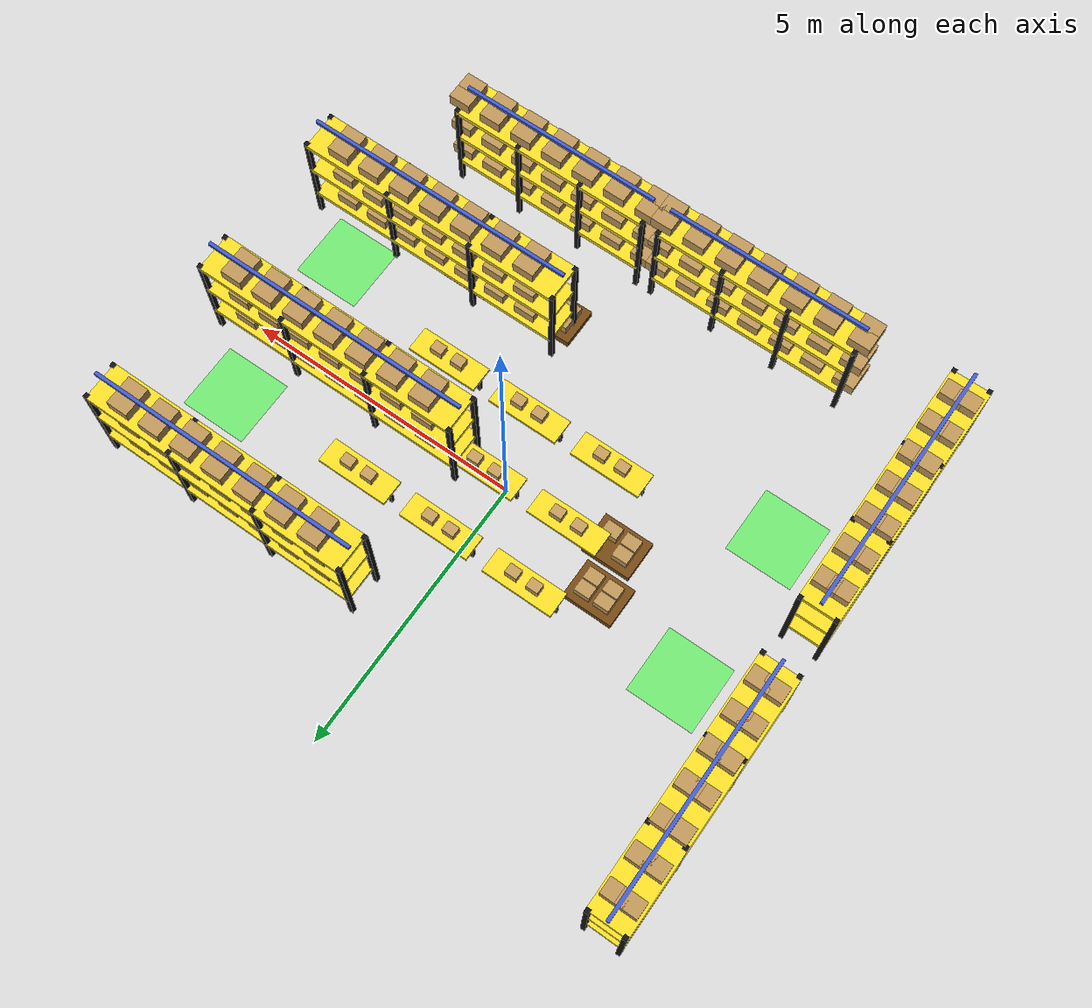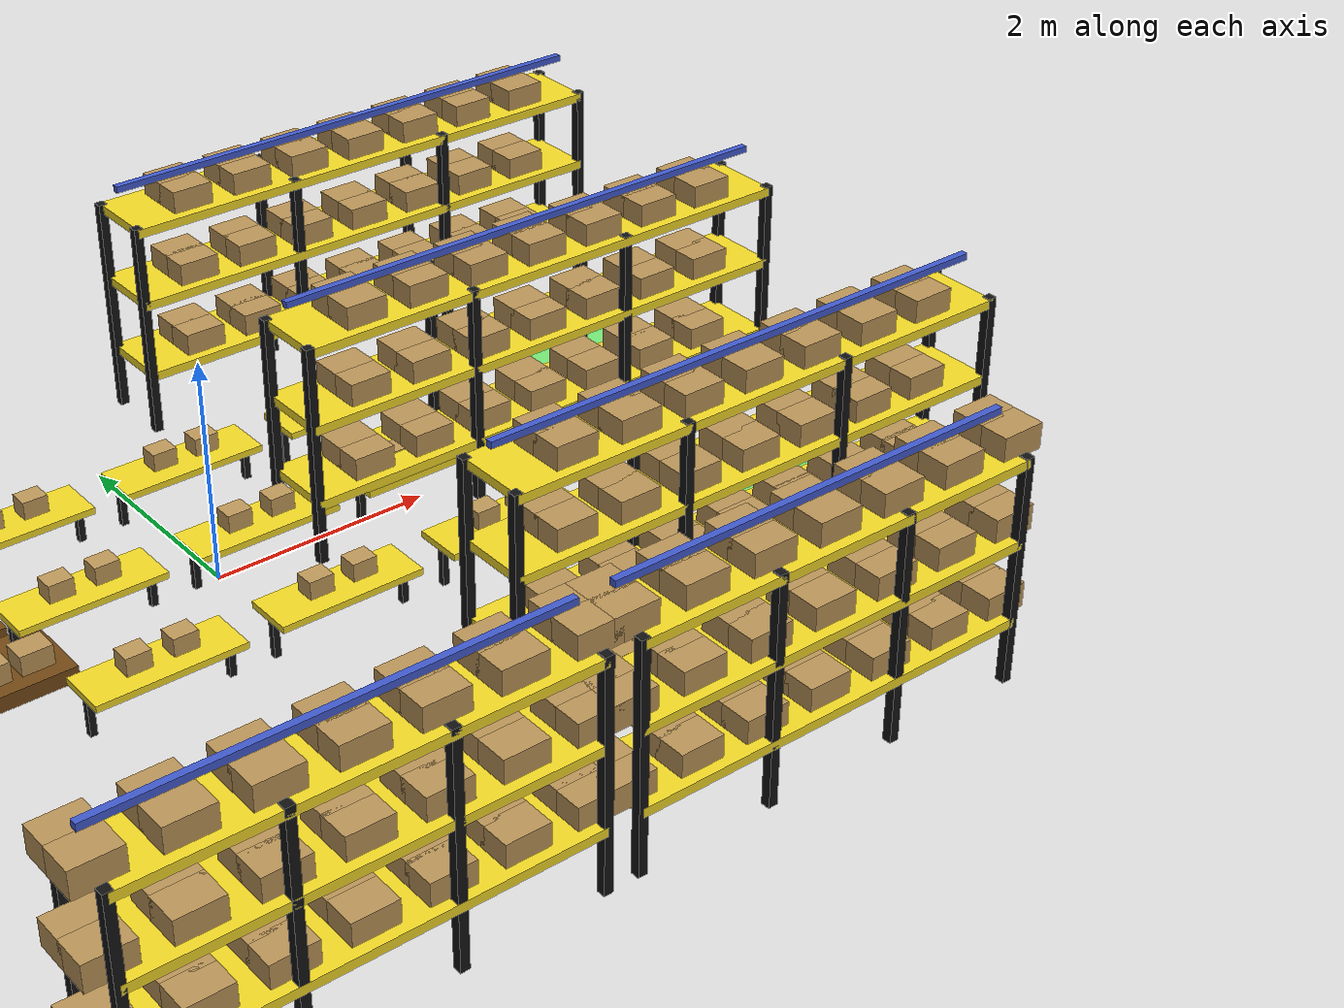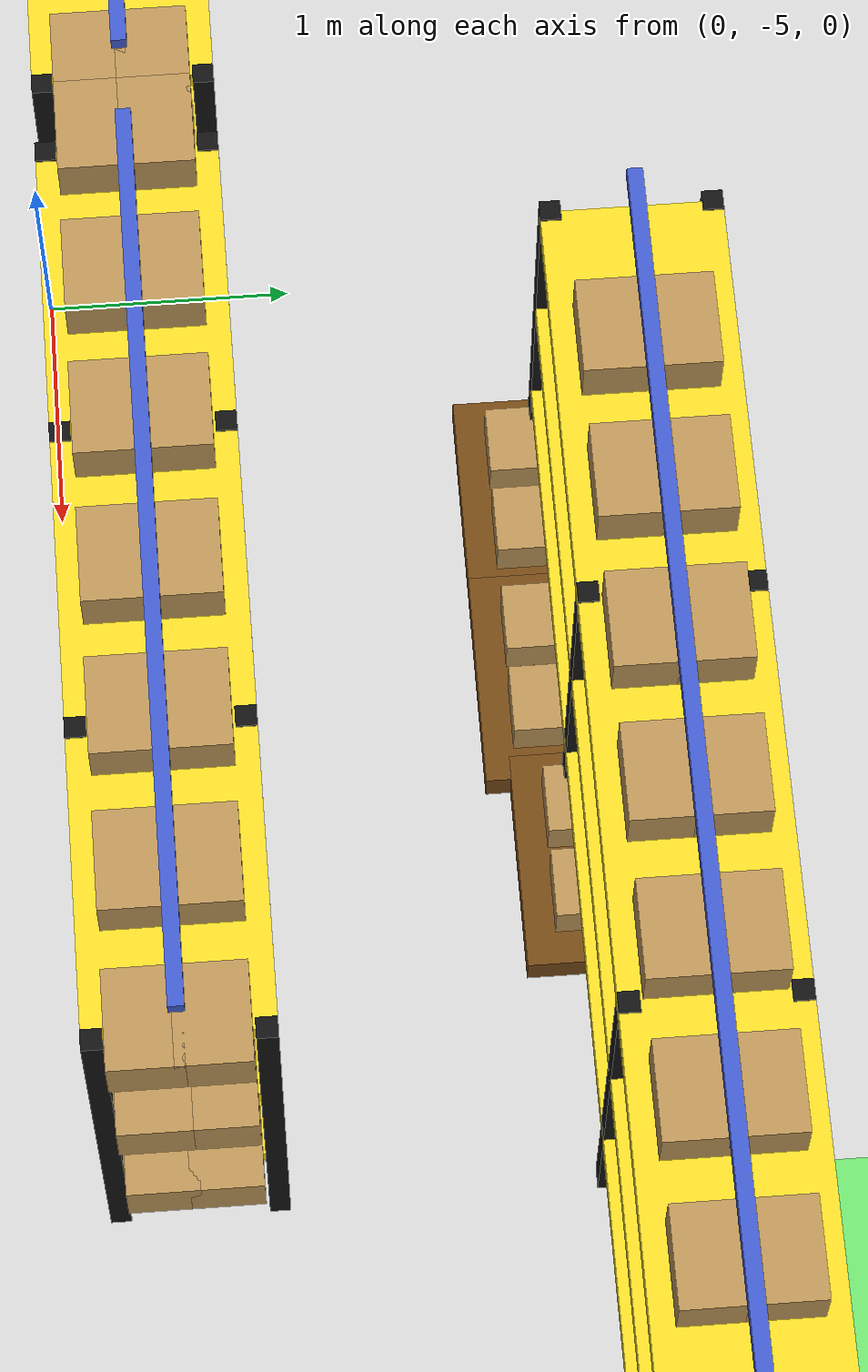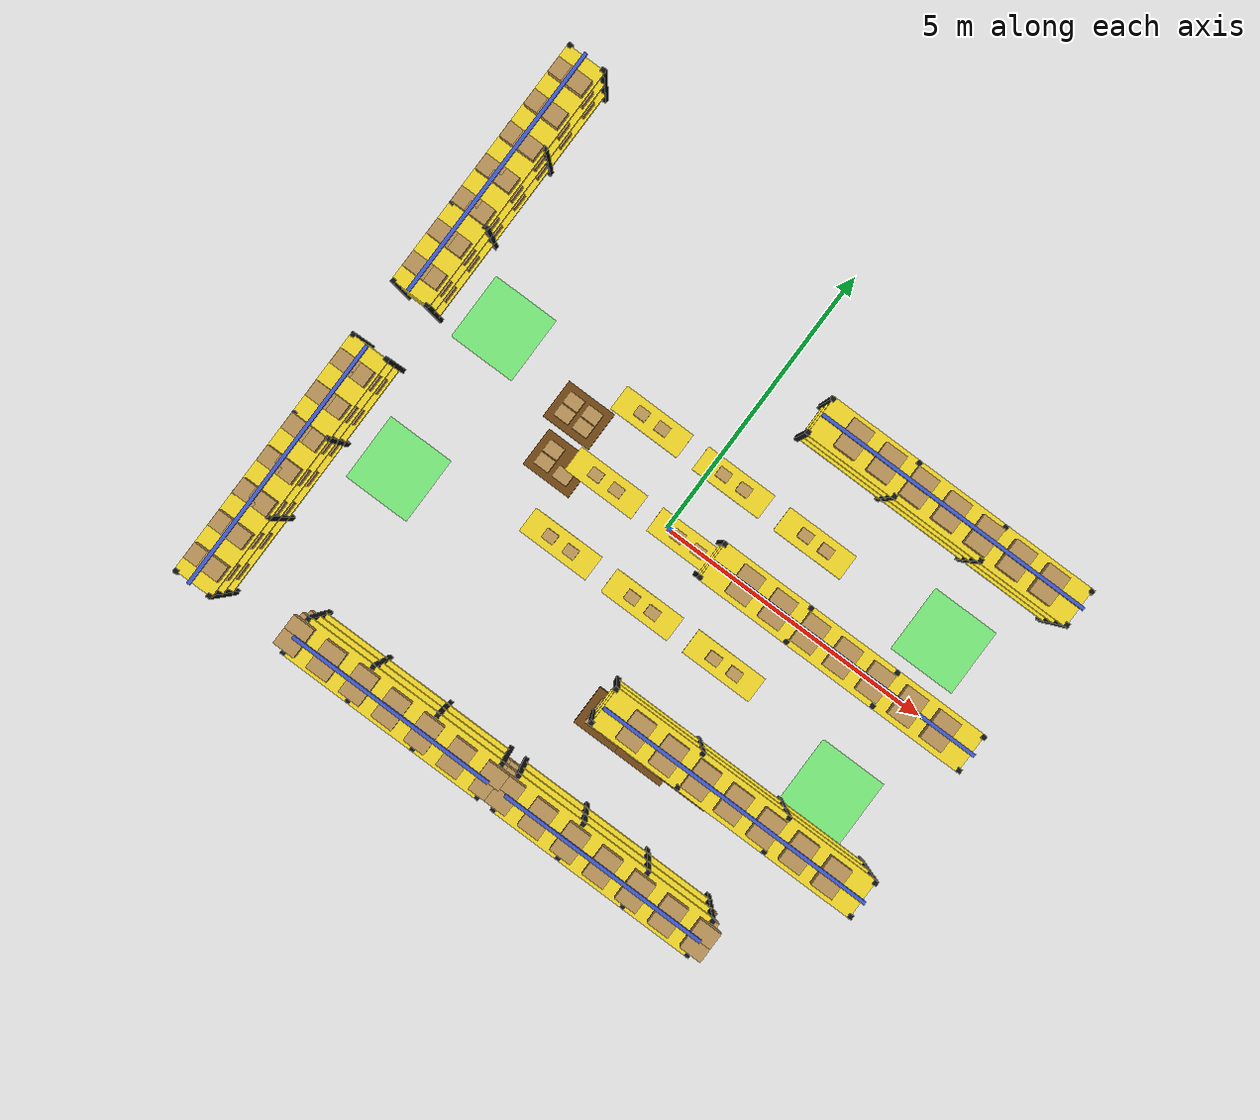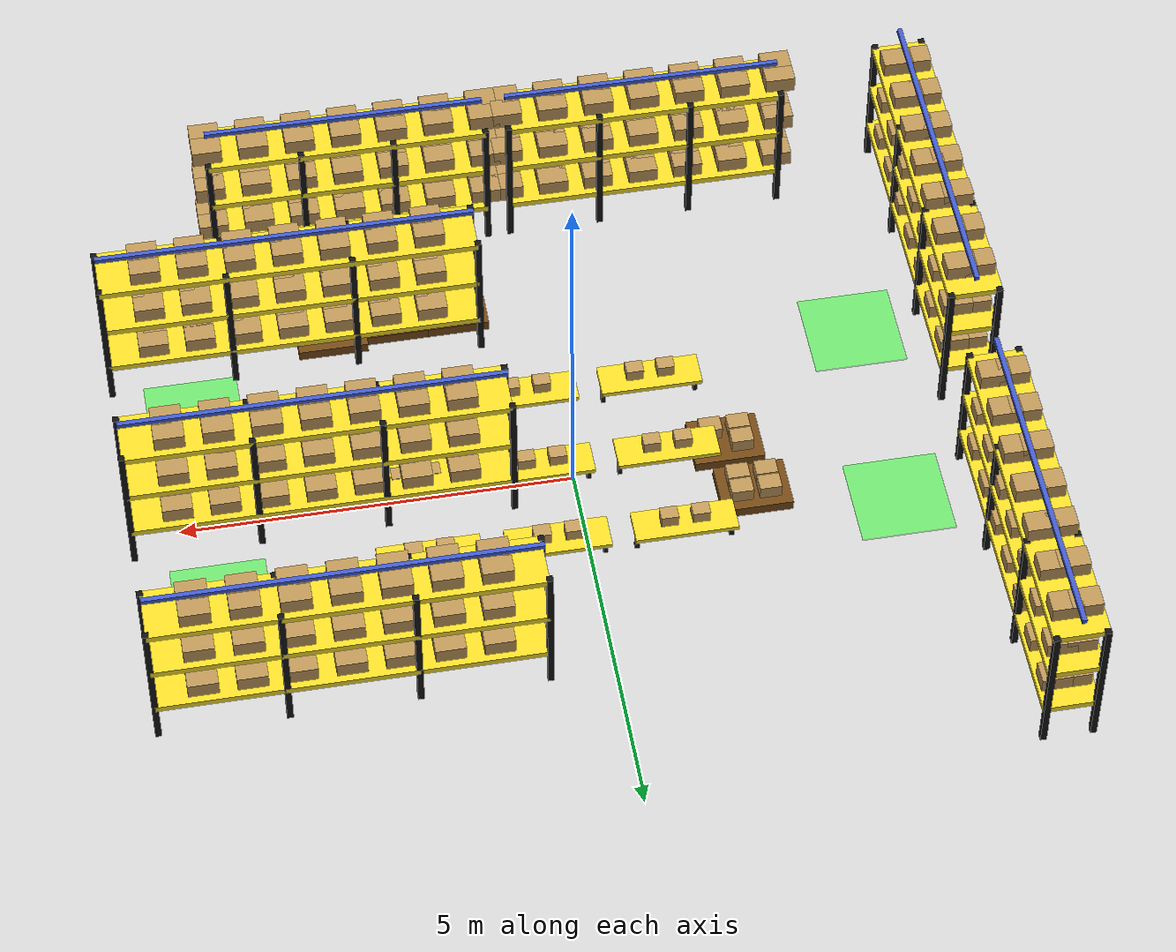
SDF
<sdf version="1.6">
 <world name="fuel_warehouse_world">
  <physics type="ode">
   <max_step_size>0.001</max_step_size>
   <real_time_update_rate>1000</real_time_update_rate>
   <real_time_factor>1.0</real_time_factor>
  </physics>
  <gravity>0 0 -9.8</gravity>
  <scene>
   <ambient>0.85 0.85 0.85 1</ambient>
   <background>0.7 0.7 0.7 1</background>
   <shadows>true</shadows>
  </scene>
  <include><uri>model://sun</uri></include>
  <model name="left_rack_top">
   <static>true</static>
   <pose>-5.2 2.7 0 0 0 1.5708</pose>
   <link name="deck_0">
    <pose>0 0 0.55 0 0 0</pose>
    <visual name="visual">
     <geometry><box><size>4.4 0.7 0.08</size></box></geometry>
     <material><ambient>0.95 0.85 0.15 1</ambient><diffuse>0.95 0.85 0.15 1</diffuse></material>
    </visual>
    <collision name="collision"><geometry><box><size>4.4 0.7 0.08</size></box></geometry></collision>
   </link>
   <link name="deck_1">
    <pose>0 0 1.25 0 0 0</pose>
    <visual name="visual">
     <geometry><box><size>4.4 0.7 0.08</size></box></geometry>
     <material><ambient>0.95 0.85 0.15 1</ambient><diffuse>0.95 0.85 0.15 1</diffuse></material>
    </visual>
    <collision name="collision"><geometry><box><size>4.4 0.7 0.08</size></box></geometry></collision>
   </link>
   <link name="deck_2">
    <pose>0 0 1.95 0 0 0</pose>
    <visual name="visual">
     <geometry><box><size>4.4 0.7 0.08</size></box></geometry>
     <material><ambient>0.95 0.85 0.15 1</ambient><diffuse>0.95 0.85 0.15 1</diffuse></material>
    </visual>
    <collision name="collision"><geometry><box><size>4.4 0.7 0.08</size></box></geometry></collision>
   </link>
   <link name="leg_0_0">
    <pose>-2.2 -0.31 1.0 0 0 0</pose>
    <visual name="visual">
     <geometry><box><size>0.08 0.08 2.0</size></box></geometry>
     <material><ambient>0.07 0.07 0.07 1</ambient><diffuse>0.07 0.07 0.07 1</diffuse></material>
    </visual>
    <collision name="collision"><geometry><box><size>0.08 0.08 2.0</size></box></geometry></collision>
   </link>
   <link name="leg_0_1">
    <pose>-2.2 0.31 1.0 0 0 0</pose>
    <visual name="visual">
     <geometry><box><size>0.08 0.08 2.0</size></box></geometry>
     <material><ambient>0.07 0.07 0.07 1</ambient><diffuse>0.07 0.07 0.07 1</diffuse></material>
    </visual>
    <collision name="collision"><geometry><box><size>0.08 0.08 2.0</size></box></geometry></collision>
   </link>
   <link name="leg_1_0">
    <pose>-0.7333333333333334 -0.31 1.0 0 0 0</pose>
    <visual name="visual">
     <geometry><box><size>0.08 0.08 2.0</size></box></geometry>
     <material><ambient>0.07 0.07 0.07 1</ambient><diffuse>0.07 0.07 0.07 1</diffuse></material>
    </visual>
    <collision name="collision"><geometry><box><size>0.08 0.08 2.0</size></box></geometry></collision>
   </link>
   <link name="leg_1_1">
    <pose>-0.7333333333333334 0.31 1.0 0 0 0</pose>
    <visual name="visual">
     <geometry><box><size>0.08 0.08 2.0</size></box></geometry>
     <material><ambient>0.07 0.07 0.07 1</ambient><diffuse>0.07 0.07 0.07 1</diffuse></material>
    </visual>
    <collision name="collision"><geometry><box><size>0.08 0.08 2.0</size></box></geometry></collision>
   </link>
   <link name="leg_2_0">
    <pose>0.7333333333333334 -0.31 1.0 0 0 0</pose>
    <visual name="visual">
     <geometry><box><size>0.08 0.08 2.0</size></box></geometry>
     <material><ambient>0.07 0.07 0.07 1</ambient><diffuse>0.07 0.07 0.07 1</diffuse></material>
    </visual>
    <collision name="collision"><geometry><box><size>0.08 0.08 2.0</size></box></geometry></collision>
   </link>
   <link name="leg_2_1">
    <pose>0.7333333333333334 0.31 1.0 0 0 0</pose>
    <visual name="visual">
     <geometry><box><size>0.08 0.08 2.0</size></box></geometry>
     <material><ambient>0.07 0.07 0.07 1</ambient><diffuse>0.07 0.07 0.07 1</diffuse></material>
    </visual>
    <collision name="collision"><geometry><box><size>0.08 0.08 2.0</size></box></geometry></collision>
   </link>
   <link name="leg_3_0">
    <pose>2.2 -0.31 1.0 0 0 0</pose>
    <visual name="visual">
     <geometry><box><size>0.08 0.08 2.0</size></box></geometry>
     <material><ambient>0.07 0.07 0.07 1</ambient><diffuse>0.07 0.07 0.07 1</diffuse></material>
    </visual>
    <collision name="collision"><geometry><box><size>0.08 0.08 2.0</size></box></geometry></collision>
   </link>
   <link name="leg_3_1">
    <pose>2.2 0.31 1.0 0 0 0</pose>
    <visual name="visual">
     <geometry><box><size>0.08 0.08 2.0</size></box></geometry>
     <material><ambient>0.07 0.07 0.07 1</ambient><diffuse>0.07 0.07 0.07 1</diffuse></material>
    </visual>
    <collision name="collision"><geometry><box><size>0.08 0.08 2.0</size></box></geometry></collision>
   </link>
   <link name="top_beam">
    <pose>0 0 2.25 0 0 0</pose>
    <visual name="visual">
     <geometry><box><size>4.4 0.06 0.06</size></box></geometry>
     <material><ambient>0.25 0.35 0.8 1</ambient><diffuse>0.25 0.35 0.8 1</diffuse></material>
    </visual>
   </link>
  </model>
  <model name="left_rack_top_box_0">
   <static>true</static>
   <pose>-5.079993388231624 0.9000004407967559 0.68 0 0 0</pose>
   <link name="link">
    <visual name="visual">
     <geometry><box><size>0.38 0.28 0.22</size></box></geometry>
     <material><ambient>0.73 0.58 0.34 1</ambient><diffuse>0.73 0.58 0.34 1</diffuse></material>
    </visual>
    <collision name="collision"><geometry><box><size>0.38 0.28 0.22</size></box></geometry></collision>
   </link>
  </model>
  <model name="left_rack_top_box_1">
   <static>true</static>
   <pose>-5.319993388230004 0.8999995592275312 0.68 0 0 0</pose>
   <link name="link">
    <visual name="visual">
     <geometry><box><size>0.38 0.28 0.22</size></box></geometry>
     <material><ambient>0.73 0.58 0.34 1</ambient><diffuse>0.73 0.58 0.34 1</diffuse></material>
    </visual>
    <collision name="collision"><geometry><box><size>0.38 0.28 0.22</size></box></geometry></collision>
   </link>
  </model>
  <model name="left_rack_top_box_2">
   <static>true</static>
   <pose>-5.079995592154686 1.5000004407927081 0.68 0 0 0</pose>
   <link name="link">
    <visual name="visual">
     <geometry><box><size>0.38 0.28 0.22</size></box></geometry>
     <material><ambient>0.73 0.58 0.34 1</ambient><diffuse>0.73 0.58 0.34 1</diffuse></material>
    </visual>
    <collision name="collision"><geometry><box><size>0.38 0.28 0.22</size></box></geometry></collision>
   </link>
  </model>
  <model name="left_rack_top_box_3">
   <static>true</static>
   <pose>-5.319995592153067 1.4999995592234834 0.68 0 0 0</pose>
   <link name="link">
    <visual name="visual">
     <geometry><box><size>0.38 0.28 0.22</size></box></geometry>
     <material><ambient>0.73 0.58 0.34 1</ambient><diffuse>0.73 0.58 0.34 1</diffuse></material>
    </visual>
    <collision name="collision"><geometry><box><size>0.38 0.28 0.22</size></box></geometry></collision>
   </link>
  </model>
  <model name="left_rack_top_box_4">
   <static>true</static>
   <pose>-5.079997796077748 2.1000004407886603 0.68 0 0 0</pose>
   <link name="link">
    <visual name="visual">
     <geometry><box><size>0.38 0.28 0.22</size></box></geometry>
     <material><ambient>0.73 0.58 0.34 1</ambient><diffuse>0.73 0.58 0.34 1</diffuse></material>
    </visual>
    <collision name="collision"><geometry><box><size>0.38 0.28 0.22</size></box></geometry></collision>
   </link>
  </model>
  <model name="left_rack_top_box_5">
   <static>true</static>
   <pose>-5.319997796076128 2.0999995592194356 0.68 0 0 0</pose>
   <link name="link">
    <visual name="visual">
     <geometry><box><size>0.38 0.28 0.22</size></box></geometry>
     <material><ambient>0.73 0.58 0.34 1</ambient><diffuse>0.73 0.58 0.34 1</diffuse></material>
    </visual>
    <collision name="collision"><geometry><box><size>0.38 0.28 0.22</size></box></geometry></collision>
   </link>
  </model>
  <model name="left_rack_top_box_6">
   <static>true</static>
   <pose>-5.08000000000081 2.7000004407846125 0.68 0 0 0</pose>
   <link name="link">
    <visual name="visual">
     <geometry><box><size>0.38 0.28 0.22</size></box></geometry>
     <material><ambient>0.73 0.58 0.34 1</ambient><diffuse>0.73 0.58 0.34 1</diffuse></material>
    </visual>
    <collision name="collision"><geometry><box><size>0.38 0.28 0.22</size></box></geometry></collision>
   </link>
  </model>
  <model name="left_rack_top_box_7">
   <static>true</static>
   <pose>-5.31999999999919 2.699999559215388 0.68 0 0 0</pose>
   <link name="link">
    <visual name="visual">
     <geometry><box><size>0.38 0.28 0.22</size></box></geometry>
     <material><ambient>0.73 0.58 0.34 1</ambient><diffuse>0.73 0.58 0.34 1</diffuse></material>
    </visual>
    <collision name="collision"><geometry><box><size>0.38 0.28 0.22</size></box></geometry></collision>
   </link>
  </model>
  <model name="left_rack_top_box_8">
   <static>true</static>
   <pose>-5.080002203923872 3.3000004407805648 0.68 0 0 0</pose>
   <link name="link">
    <visual name="visual">
     <geometry><box><size>0.38 0.28 0.22</size></box></geometry>
     <material><ambient>0.73 0.58 0.34 1</ambient><diffuse>0.73 0.58 0.34 1</diffuse></material>
    </visual>
    <collision name="collision"><geometry><box><size>0.38 0.28 0.22</size></box></geometry></collision>
   </link>
  </model>
  <model name="left_rack_top_box_9">
   <static>true</static>
   <pose>-5.320002203922252 3.29999955921134 0.68 0 0 0</pose>
   <link name="link">
    <visual name="visual">
     <geometry><box><size>0.38 0.28 0.22</size></box></geometry>
     <material><ambient>0.73 0.58 0.34 1</ambient><diffuse>0.73 0.58 0.34 1</diffuse></material>
    </visual>
    <collision name="collision"><geometry><box><size>0.38 0.28 0.22</size></box></geometry></collision>
   </link>
  </model>
  <model name="left_rack_top_box_10">
   <static>true</static>
   <pose>-5.080004407846934 3.900000440776517 0.68 0 0 0</pose>
   <link name="link">
    <visual name="visual">
     <geometry><box><size>0.38 0.28 0.22</size></box></geometry>
     <material><ambient>0.73 0.58 0.34 1</ambient><diffuse>0.73 0.58 0.34 1</diffuse></material>
    </visual>
    <collision name="collision"><geometry><box><size>0.38 0.28 0.22</size></box></geometry></collision>
   </link>
  </model>
  <model name="left_rack_top_box_11">
   <static>true</static>
   <pose>-5.320004407845314 3.8999995592072922 0.68 0 0 0</pose>
   <link name="link">
    <visual name="visual">
     <geometry><box><size>0.38 0.28 0.22</size></box></geometry>
     <material><ambient>0.73 0.58 0.34 1</ambient><diffuse>0.73 0.58 0.34 1</diffuse></material>
    </visual>
    <collision name="collision"><geometry><box><size>0.38 0.28 0.22</size></box></geometry></collision>
   </link>
  </model>
  <model name="left_rack_top_box_12">
   <static>true</static>
   <pose>-5.0800066117699965 4.500000440772469 0.68 0 0 0</pose>
   <link name="link">
    <visual name="visual">
     <geometry><box><size>0.38 0.28 0.22</size></box></geometry>
     <material><ambient>0.73 0.58 0.34 1</ambient><diffuse>0.73 0.58 0.34 1</diffuse></material>
    </visual>
    <collision name="collision"><geometry><box><size>0.38 0.28 0.22</size></box></geometry></collision>
   </link>
  </model>
  <model name="left_rack_top_box_13">
   <static>true</static>
   <pose>-5.320006611768377 4.4999995592032445 0.68 0 0 0</pose>
   <link name="link">
    <visual name="visual">
     <geometry><box><size>0.38 0.28 0.22</size></box></geometry>
     <material><ambient>0.73 0.58 0.34 1</ambient><diffuse>0.73 0.58 0.34 1</diffuse></material>
    </visual>
    <collision name="collision"><geometry><box><size>0.38 0.28 0.22</size></box></geometry></collision>
   </link>
  </model>
  <model name="left_rack_top_box_14">
   <static>true</static>
   <pose>-5.079993388231624 0.9000004407967559 1.38 0 0 0</pose>
   <link name="link">
    <visual name="visual">
     <geometry><box><size>0.38 0.28 0.22</size></box></geometry>
     <material><ambient>0.73 0.58 0.34 1</ambient><diffuse>0.73 0.58 0.34 1</diffuse></material>
    </visual>
    <collision name="collision"><geometry><box><size>0.38 0.28 0.22</size></box></geometry></collision>
   </link>
  </model>
  <model name="left_rack_top_box_15">
   <static>true</static>
   <pose>-5.319993388230004 0.8999995592275312 1.38 0 0 0</pose>
   <link name="link">
    <visual name="visual">
     <geometry><box><size>0.38 0.28 0.22</size></box></geometry>
     <material><ambient>0.73 0.58 0.34 1</ambient><diffuse>0.73 0.58 0.34 1</diffuse></material>
    </visual>
    <collision name="collision"><geometry><box><size>0.38 0.28 0.22</size></box></geometry></collision>
   </link>
  </model>
  <model name="left_rack_top_box_16">
   <static>true</static>
   <pose>-5.079995592154686 1.5000004407927081 1.38 0 0 0</pose>
   <link name="link">
    <visual name="visual">
     <geometry><box><size>0.38 0.28 0.22</size></box></geometry>
     <material><ambient>0.73 0.58 0.34 1</ambient><diffuse>0.73 0.58 0.34 1</diffuse></material>
    </visual>
    <collision name="collision"><geometry><box><size>0.38 0.28 0.22</size></box></geometry></collision>
   </link>
  </model>
  <model name="left_rack_top_box_17">
   <static>true</static>
   <pose>-5.319995592153067 1.4999995592234834 1.38 0 0 0</pose>
   <link name="link">
    <visual name="visual">
     <geometry><box><size>0.38 0.28 0.22</size></box></geometry>
     <material><ambient>0.73 0.58 0.34 1</ambient><diffuse>0.73 0.58 0.34 1</diffuse></material>
    </visual>
    <collision name="collision"><geometry><box><size>0.38 0.28 0.22</size></box></geometry></collision>
   </link>
  </model>
  <model name="left_rack_top_box_18">
   <static>true</static>
   <pose>-5.079997796077748 2.1000004407886603 1.38 0 0 0</pose>
   <link name="link">
    <visual name="visual">
     <geometry><box><size>0.38 0.28 0.22</size></box></geometry>
     <material><ambient>0.73 0.58 0.34 1</ambient><diffuse>0.73 0.58 0.34 1</diffuse></material>
    </visual>
    <collision name="collision"><geometry><box><size>0.38 0.28 0.22</size></box></geometry></collision>
   </link>
  </model>
  <model name="left_rack_top_box_19">
   <static>true</static>
   <pose>-5.319997796076128 2.0999995592194356 1.38 0 0 0</pose>
   <link name="link">
    <visual name="visual">
     <geometry><box><size>0.38 0.28 0.22</size></box></geometry>
     <material><ambient>0.73 0.58 0.34 1</ambient><diffuse>0.73 0.58 0.34 1</diffuse></material>
    </visual>
    <collision name="collision"><geometry><box><size>0.38 0.28 0.22</size></box></geometry></collision>
   </link>
  </model>
  <model name="left_rack_top_box_20">
   <static>true</static>
   <pose>-5.08000000000081 2.7000004407846125 1.38 0 0 0</pose>
   <link name="link">
    <visual name="visual">
     <geometry><box><size>0.38 0.28 0.22</size></box></geometry>
     <material><ambient>0.73 0.58 0.34 1</ambient><diffuse>0.73 0.58 0.34 1</diffuse></material>
    </visual>
    <collision name="collision"><geometry><box><size>0.38 0.28 0.22</size></box></geometry></collision>
   </link>
  </model>
  <model name="left_rack_top_box_21">
   <static>true</static>
   <pose>-5.31999999999919 2.699999559215388 1.38 0 0 0</pose>
   <link name="link">
    <visual name="visual">
     <geometry><box><size>0.38 0.28 0.22</size></box></geometry>
     <material><ambient>0.73 0.58 0.34 1</ambient><diffuse>0.73 0.58 0.34 1</diffuse></material>
    </visual>
    <collision name="collision"><geometry><box><size>0.38 0.28 0.22</size></box></geometry></collision>
   </link>
  </model>
  <model name="left_rack_top_box_22">
   <static>true</static>
   <pose>-5.080002203923872 3.3000004407805648 1.38 0 0 0</pose>
   <link name="link">
    <visual name="visual">
     <geometry><box><size>0.38 0.28 0.22</size></box></geometry>
     <material><ambient>0.73 0.58 0.34 1</ambient><diffuse>0.73 0.58 0.34 1</diffuse></material>
    </visual>
    <collision name="collision"><geometry><box><size>0.38 0.28 0.22</size></box></geometry></collision>
   </link>
  </model>
  <model name="left_rack_top_box_23">
   <static>true</static>
   <pose>-5.320002203922252 3.29999955921134 1.38 0 0 0</pose>
   <link name="link">
    <visual name="visual">
     <geometry><box><size>0.38 0.28 0.22</size></box></geometry>
     <material><ambient>0.73 0.58 0.34 1</ambient><diffuse>0.73 0.58 0.34 1</diffuse></material>
    </visual>
    <collision name="collision"><geometry><box><size>0.38 0.28 0.22</size></box></geometry></collision>
   </link>
  </model>
  <model name="left_rack_top_box_24">
   <static>true</static>
   <pose>-5.080004407846934 3.900000440776517 1.38 0 0 0</pose>
   <link name="link">
    <visual name="visual">
     <geometry><box><size>0.38 0.28 0.22</size></box></geometry>
     <material><ambient>0.73 0.58 0.34 1</ambient><diffuse>0.73 0.58 0.34 1</diffuse></material>
    </visual>
    <collision name="collision"><geometry><box><size>0.38 0.28 0.22</size></box></geometry></collision>
   </link>
  </model>
  <model name="left_rack_top_box_25">
   <static>true</static>
   <pose>-5.320004407845314 3.8999995592072922 1.38 0 0 0</pose>
   <link name="link">
    <visual name="visual">
     <geometry><box><size>0.38 0.28 0.22</size></box></geometry>
     <material><ambient>0.73 0.58 0.34 1</ambient><diffuse>0.73 0.58 0.34 1</diffuse></material>
    </visual>
    <collision name="collision"><geometry><box><size>0.38 0.28 0.22</size></box></geometry></collision>
   </link>
  </model>
  <model name="left_rack_top_box_26">
   <static>true</static>
   <pose>-5.0800066117699965 4.500000440772469 1.38 0 0 0</pose>
   <link name="link">
    <visual name="visual">
     <geometry><box><size>0.38 0.28 0.22</size></box></geometry>
     <material><ambient>0.73 0.58 0.34 1</ambient><diffuse>0.73 0.58 0.34 1</diffuse></material>
    </visual>
    <collision name="collision"><geometry><box><size>0.38 0.28 0.22</size></box></geometry></collision>
   </link>
  </model>
  <model name="left_rack_top_box_27">
   <static>true</static>
   <pose>-5.320006611768377 4.4999995592032445 1.38 0 0 0</pose>
   <link name="link">
    <visual name="visual">
     <geometry><box><size>0.38 0.28 0.22</size></box></geometry>
     <material><ambient>0.73 0.58 0.34 1</ambient><diffuse>0.73 0.58 0.34 1</diffuse></material>
    </visual>
    <collision name="collision"><geometry><box><size>0.38 0.28 0.22</size></box></geometry></collision>
   </link>
  </model>
  <model name="left_rack_top_box_28">
   <static>true</static>
   <pose>-5.079993388231624 0.9000004407967559 2.08 0 0 0</pose>
   <link name="link">
    <visual name="visual">
     <geometry><box><size>0.38 0.28 0.22</size></box></geometry>
     <material><ambient>0.73 0.58 0.34 1</ambient><diffuse>0.73 0.58 0.34 1</diffuse></material>
    </visual>
    <collision name="collision"><geometry><box><size>0.38 0.28 0.22</size></box></geometry></collision>
   </link>
  </model>
  <model name="left_rack_top_box_29">
   <static>true</static>
   <pose>-5.319993388230004 0.8999995592275312 2.08 0 0 0</pose>
   <link name="link">
    <visual name="visual">
     <geometry><box><size>0.38 0.28 0.22</size></box></geometry>
     <material><ambient>0.73 0.58 0.34 1</ambient><diffuse>0.73 0.58 0.34 1</diffuse></material>
    </visual>
    <collision name="collision"><geometry><box><size>0.38 0.28 0.22</size></box></geometry></collision>
   </link>
  </model>
  <model name="left_rack_top_box_30">
   <static>true</static>
   <pose>-5.079995592154686 1.5000004407927081 2.08 0 0 0</pose>
   <link name="link">
    <visual name="visual">
     <geometry><box><size>0.38 0.28 0.22</size></box></geometry>
     <material><ambient>0.73 0.58 0.34 1</ambient><diffuse>0.73 0.58 0.34 1</diffuse></material>
    </visual>
    <collision name="collision"><geometry><box><size>0.38 0.28 0.22</size></box></geometry></collision>
   </link>
  </model>
  <model name="left_rack_top_box_31">
   <static>true</static>
   <pose>-5.319995592153067 1.4999995592234834 2.08 0 0 0</pose>
   <link name="link">
    <visual name="visual">
     <geometry><box><size>0.38 0.28 0.22</size></box></geometry>
     <material><ambient>0.73 0.58 0.34 1</ambient><diffuse>0.73 0.58 0.34 1</diffuse></material>
    </visual>
    <collision name="collision"><geometry><box><size>0.38 0.28 0.22</size></box></geometry></collision>
   </link>
  </model>
  <model name="left_rack_top_box_32">
   <static>true</static>
   <pose>-5.079997796077748 2.1000004407886603 2.08 0 0 0</pose>
   <link name="link">
    <visual name="visual">
     <geometry><box><size>0.38 0.28 0.22</size></box></geometry>
     <material><ambient>0.73 0.58 0.34 1</ambient><diffuse>0.73 0.58 0.34 1</diffuse></material>
    </visual>
    <collision name="collision"><geometry><box><size>0.38 0.28 0.22</size></box></geometry></collision>
   </link>
  </model>
  <model name="left_rack_top_box_33">
   <static>true</static>
   <pose>-5.319997796076128 2.0999995592194356 2.08 0 0 0</pose>
   <link name="link">
    <visual name="visual">
     <geometry><box><size>0.38 0.28 0.22</size></box></geometry>
     <material><ambient>0.73 0.58 0.34 1</ambient><diffuse>0.73 0.58 0.34 1</diffuse></material>
    </visual>
    <collision name="collision"><geometry><box><size>0.38 0.28 0.22</size></box></geometry></collision>
   </link>
  </model>
  <model name="left_rack_top_box_34">
   <static>true</static>
   <pose>-5.08000000000081 2.7000004407846125 2.08 0 0 0</pose>
   <link name="link">
    <visual name="visual">
     <geometry><box><size>0.38 0.28 0.22</size></box></geometry>
     <material><ambient>0.73 0.58 0.34 1</ambient><diffuse>0.73 0.58 0.34 1</diffuse></material>
    </visual>
    <collision name="collision"><geometry><box><size>0.38 0.28 0.22</size></box></geometry></collision>
   </link>
  </model>
  <model name="left_rack_top_box_35">
   <static>true</static>
   <pose>-5.31999999999919 2.699999559215388 2.08 0 0 0</pose>
   <link name="link">
    <visual name="visual">
     <geometry><box><size>0.38 0.28 0.22</size></box></geometry>
     <material><ambient>0.73 0.58 0.34 1</ambient><diffuse>0.73 0.58 0.34 1</diffuse></material>
    </visual>
    <collision name="collision"><geometry><box><size>0.38 0.28 0.22</size></box></geometry></collision>
   </link>
  </model>
  <model name="left_rack_top_box_36">
   <static>true</static>
   <pose>-5.080002203923872 3.3000004407805648 2.08 0 0 0</pose>
   <link name="link">
    <visual name="visual">
     <geometry><box><size>0.38 0.28 0.22</size></box></geometry>
     <material><ambient>0.73 0.58 0.34 1</ambient><diffuse>0.73 0.58 0.34 1</diffuse></material>
    </visual>
    <collision name="collision"><geometry><box><size>0.38 0.28 0.22</size></box></geometry></collision>
   </link>
  </model>
  <model name="left_rack_top_box_37">
   <static>true</static>
   <pose>-5.320002203922252 3.29999955921134 2.08 0 0 0</pose>
   <link name="link">
    <visual name="visual">
     <geometry><box><size>0.38 0.28 0.22</size></box></geometry>
     <material><ambient>0.73 0.58 0.34 1</ambient><diffuse>0.73 0.58 0.34 1</diffuse></material>
    </visual>
    <collision name="collision"><geometry><box><size>0.38 0.28 0.22</size></box></geometry></collision>
   </link>
  </model>
  <model name="left_rack_top_box_38">
   <static>true</static>
   <pose>-5.080004407846934 3.900000440776517 2.08 0 0 0</pose>
   <link name="link">
    <visual name="visual">
     <geometry><box><size>0.38 0.28 0.22</size></box></geometry>
     <material><ambient>0.73 0.58 0.34 1</ambient><diffuse>0.73 0.58 0.34 1</diffuse></material>
    </visual>
    <collision name="collision"><geometry><box><size>0.38 0.28 0.22</size></box></geometry></collision>
   </link>
  </model>
  <model name="left_rack_top_box_39">
   <static>true</static>
   <pose>-5.320004407845314 3.8999995592072922 2.08 0 0 0</pose>
   <link name="link">
    <visual name="visual">
     <geometry><box><size>0.38 0.28 0.22</size></box></geometry>
     <material><ambient>0.73 0.58 0.34 1</ambient><diffuse>0.73 0.58 0.34 1</diffuse></material>
    </visual>
    <collision name="collision"><geometry><box><size>0.38 0.28 0.22</size></box></geometry></collision>
   </link>
  </model>
  <model name="left_rack_top_box_40">
   <static>true</static>
   <pose>-5.0800066117699965 4.500000440772469 2.08 0 0 0</pose>
   <link name="link">
    <visual name="visual">
     <geometry><box><size>0.38 0.28 0.22</size></box></geometry>
     <material><ambient>0.73 0.58 0.34 1</ambient><diffuse>0.73 0.58 0.34 1</diffuse></material>
    </visual>
    <collision name="collision"><geometry><box><size>0.38 0.28 0.22</size></box></geometry></collision>
   </link>
  </model>
  <model name="left_rack_top_box_41">
   <static>true</static>
   <pose>-5.320006611768377 4.4999995592032445 2.08 0 0 0</pose>
   <link name="link">
    <visual name="visual">
     <geometry><box><size>0.38 0.28 0.22</size></box></geometry>
     <material><ambient>0.73 0.58 0.34 1</ambient><diffuse>0.73 0.58 0.34 1</diffuse></material>
    </visual>
    <collision name="collision"><geometry><box><size>0.38 0.28 0.22</size></box></geometry></collision>
   </link>
  </model>
  <model name="left_rack_bottom">
   <static>true</static>
   <pose>-5.2 -2.7 0 0 0 1.5708</pose>
   <link name="deck_0">
    <pose>0 0 0.55 0 0 0</pose>
    <visual name="visual">
     <geometry><box><size>4.4 0.7 0.08</size></box></geometry>
     <material><ambient>0.95 0.85 0.15 1</ambient><diffuse>0.95 0.85 0.15 1</diffuse></material>
    </visual>
    <collision name="collision"><geometry><box><size>4.4 0.7 0.08</size></box></geometry></collision>
   </link>
   <link name="deck_1">
    <pose>0 0 1.25 0 0 0</pose>
    <visual name="visual">
     <geometry><box><size>4.4 0.7 0.08</size></box></geometry>
     <material><ambient>0.95 0.85 0.15 1</ambient><diffuse>0.95 0.85 0.15 1</diffuse></material>
    </visual>
    <collision name="collision"><geometry><box><size>4.4 0.7 0.08</size></box></geometry></collision>
   </link>
   <link name="deck_2">
    <pose>0 0 1.95 0 0 0</pose>
    <visual name="visual">
     <geometry><box><size>4.4 0.7 0.08</size></box></geometry>
     <material><ambient>0.95 0.85 0.15 1</ambient><diffuse>0.95 0.85 0.15 1</diffuse></material>
    </visual>
    <collision name="collision"><geometry><box><size>4.4 0.7 0.08</size></box></geometry></collision>
   </link>
   <link name="leg_0_0">
    <pose>-2.2 -0.31 1.0 0 0 0</pose>
    <visual name="visual">
     <geometry><box><size>0.08 0.08 2.0</size></box></geometry>
     <material><ambient>0.07 0.07 0.07 1</ambient><diffuse>0.07 0.07 0.07 1</diffuse></material>
    </visual>
    <collision name="collision"><geometry><box><size>0.08 0.08 2.0</size></box></geometry></collision>
   </link>
   <link name="leg_0_1">
    <pose>-2.2 0.31 1.0 0 0 0</pose>
    <visual name="visual">
     <geometry><box><size>0.08 0.08 2.0</size></box></geometry>
     <material><ambient>0.07 0.07 0.07 1</ambient><diffuse>0.07 0.07 0.07 1</diffuse></material>
    </visual>
    <collision name="collision"><geometry><box><size>0.08 0.08 2.0</size></box></geometry></collision>
   </link>
   <link name="leg_1_0">
    <pose>-0.7333333333333334 -0.31 1.0 0 0 0</pose>
    <visual name="visual">
     <geometry><box><size>0.08 0.08 2.0</size></box></geometry>
     <material><ambient>0.07 0.07 0.07 1</ambient><diffuse>0.07 0.07 0.07 1</diffuse></material>
    </visual>
    <collision name="collision"><geometry><box><size>0.08 0.08 2.0</size></box></geometry></collision>
   </link>
   <link name="leg_1_1">
    <pose>-0.7333333333333334 0.31 1.0 0 0 0</pose>
    <visual name="visual">
     <geometry><box><size>0.08 0.08 2.0</size></box></geometry>
     <material><ambient>0.07 0.07 0.07 1</ambient><diffuse>0.07 0.07 0.07 1</diffuse></material>
    </visual>
    <collision name="collision"><geometry><box><size>0.08 0.08 2.0</size></box></geometry></collision>
   </link>
   <link name="leg_2_0">
    <pose>0.7333333333333334 -0.31 1.0 0 0 0</pose>
    <visual name="visual">
     <geometry><box><size>0.08 0.08 2.0</size></box></geometry>
     <material><ambient>0.07 0.07 0.07 1</ambient><diffuse>0.07 0.07 0.07 1</diffuse></material>
    </visual>
    <collision name="collision"><geometry><box><size>0.08 0.08 2.0</size></box></geometry></collision>
   </link>
   <link name="leg_2_1">
    <pose>0.7333333333333334 0.31 1.0 0 0 0</pose>
    <visual name="visual">
     <geometry><box><size>0.08 0.08 2.0</size></box></geometry>
     <material><ambient>0.07 0.07 0.07 1</ambient><diffuse>0.07 0.07 0.07 1</diffuse></material>
    </visual>
    <collision name="collision"><geometry><box><size>0.08 0.08 2.0</size></box></geometry></collision>
   </link>
   <link name="leg_3_0">
    <pose>2.2 -0.31 1.0 0 0 0</pose>
    <visual name="visual">
     <geometry><box><size>0.08 0.08 2.0</size></box></geometry>
     <material><ambient>0.07 0.07 0.07 1</ambient><diffuse>0.07 0.07 0.07 1</diffuse></material>
    </visual>
    <collision name="collision"><geometry><box><size>0.08 0.08 2.0</size></box></geometry></collision>
   </link>
   <link name="leg_3_1">
    <pose>2.2 0.31 1.0 0 0 0</pose>
    <visual name="visual">
     <geometry><box><size>0.08 0.08 2.0</size></box></geometry>
     <material><ambient>0.07 0.07 0.07 1</ambient><diffuse>0.07 0.07 0.07 1</diffuse></material>
    </visual>
    <collision name="collision"><geometry><box><size>0.08 0.08 2.0</size></box></geometry></collision>
   </link>
   <link name="top_beam">
    <pose>0 0 2.25 0 0 0</pose>
    <visual name="visual">
     <geometry><box><size>4.4 0.06 0.06</size></box></geometry>
     <material><ambient>0.25 0.35 0.8 1</ambient><diffuse>0.25 0.35 0.8 1</diffuse></material>
    </visual>
   </link>
  </model>
  <model name="left_rack_bottom_box_0">
   <static>true</static>
   <pose>-5.079993388231624 -4.4999995592032445 0.68 0 0 0</pose>
   <link name="link">
    <visual name="visual">
     <geometry><box><size>0.38 0.28 0.22</size></box></geometry>
     <material><ambient>0.73 0.58 0.34 1</ambient><diffuse>0.73 0.58 0.34 1</diffuse></material>
    </visual>
    <collision name="collision"><geometry><box><size>0.38 0.28 0.22</size></box></geometry></collision>
   </link>
  </model>
  <model name="left_rack_bottom_box_1">
   <static>true</static>
   <pose>-5.319993388230004 -4.500000440772469 0.68 0 0 0</pose>
   <link name="link">
    <visual name="visual">
     <geometry><box><size>0.38 0.28 0.22</size></box></geometry>
     <material><ambient>0.73 0.58 0.34 1</ambient><diffuse>0.73 0.58 0.34 1</diffuse></material>
    </visual>
    <collision name="collision"><geometry><box><size>0.38 0.28 0.22</size></box></geometry></collision>
   </link>
  </model>
  <model name="left_rack_bottom_box_2">
   <static>true</static>
   <pose>-5.079995592154686 -3.8999995592072922 0.68 0 0 0</pose>
   <link name="link">
    <visual name="visual">
     <geometry><box><size>0.38 0.28 0.22</size></box></geometry>
     <material><ambient>0.73 0.58 0.34 1</ambient><diffuse>0.73 0.58 0.34 1</diffuse></material>
    </visual>
    <collision name="collision"><geometry><box><size>0.38 0.28 0.22</size></box></geometry></collision>
   </link>
  </model>
  <model name="left_rack_bottom_box_3">
   <static>true</static>
   <pose>-5.319995592153067 -3.900000440776517 0.68 0 0 0</pose>
   <link name="link">
    <visual name="visual">
     <geometry><box><size>0.38 0.28 0.22</size></box></geometry>
     <material><ambient>0.73 0.58 0.34 1</ambient><diffuse>0.73 0.58 0.34 1</diffuse></material>
    </visual>
    <collision name="collision"><geometry><box><size>0.38 0.28 0.22</size></box></geometry></collision>
   </link>
  </model>
  <model name="left_rack_bottom_box_4">
   <static>true</static>
   <pose>-5.079997796077748 -3.29999955921134 0.68 0 0 0</pose>
   <link name="link">
    <visual name="visual">
     <geometry><box><size>0.38 0.28 0.22</size></box></geometry>
     <material><ambient>0.73 0.58 0.34 1</ambient><diffuse>0.73 0.58 0.34 1</diffuse></material>
    </visual>
    <collision name="collision"><geometry><box><size>0.38 0.28 0.22</size></box></geometry></collision>
   </link>
  </model>
  <model name="left_rack_bottom_box_5">
   <static>true</static>
   <pose>-5.319997796076128 -3.3000004407805648 0.68 0 0 0</pose>
   <link name="link">
    <visual name="visual">
     <geometry><box><size>0.38 0.28 0.22</size></box></geometry>
     <material><ambient>0.73 0.58 0.34 1</ambient><diffuse>0.73 0.58 0.34 1</diffuse></material>
    </visual>
    <collision name="collision"><geometry><box><size>0.38 0.28 0.22</size></box></geometry></collision>
   </link>
  </model>
  <model name="left_rack_bottom_box_6">
   <static>true</static>
   <pose>-5.08000000000081 -2.699999559215388 0.68 0 0 0</pose>
   <link name="link">
    <visual name="visual">
     <geometry><box><size>0.38 0.28 0.22</size></box></geometry>
     <material><ambient>0.73 0.58 0.34 1</ambient><diffuse>0.73 0.58 0.34 1</diffuse></material>
    </visual>
    <collision name="collision"><geometry><box><size>0.38 0.28 0.22</size></box></geometry></collision>
   </link>
  </model>
  <model name="left_rack_bottom_box_7">
   <static>true</static>
   <pose>-5.31999999999919 -2.7000004407846125 0.68 0 0 0</pose>
   <link name="link">
    <visual name="visual">
     <geometry><box><size>0.38 0.28 0.22</size></box></geometry>
     <material><ambient>0.73 0.58 0.34 1</ambient><diffuse>0.73 0.58 0.34 1</diffuse></material>
    </visual>
    <collision name="collision"><geometry><box><size>0.38 0.28 0.22</size></box></geometry></collision>
   </link>
  </model>
  <model name="left_rack_bottom_box_8">
   <static>true</static>
   <pose>-5.080002203923872 -2.0999995592194356 0.68 0 0 0</pose>
   <link name="link">
    <visual name="visual">
     <geometry><box><size>0.38 0.28 0.22</size></box></geometry>
     <material><ambient>0.73 0.58 0.34 1</ambient><diffuse>0.73 0.58 0.34 1</diffuse></material>
    </visual>
    <collision name="collision"><geometry><box><size>0.38 0.28 0.22</size></box></geometry></collision>
   </link>
  </model>
  <model name="left_rack_bottom_box_9">
   <static>true</static>
   <pose>-5.320002203922252 -2.1000004407886603 0.68 0 0 0</pose>
   <link name="link">
    <visual name="visual">
     <geometry><box><size>0.38 0.28 0.22</size></box></geometry>
     <material><ambient>0.73 0.58 0.34 1</ambient><diffuse>0.73 0.58 0.34 1</diffuse></material>
    </visual>
    <collision name="collision"><geometry><box><size>0.38 0.28 0.22</size></box></geometry></collision>
   </link>
  </model>
  <model name="left_rack_bottom_box_10">
   <static>true</static>
   <pose>-5.080004407846934 -1.4999995592234834 0.68 0 0 0</pose>
   <link name="link">
    <visual name="visual">
     <geometry><box><size>0.38 0.28 0.22</size></box></geometry>
     <material><ambient>0.73 0.58 0.34 1</ambient><diffuse>0.73 0.58 0.34 1</diffuse></material>
    </visual>
    <collision name="collision"><geometry><box><size>0.38 0.28 0.22</size></box></geometry></collision>
   </link>
  </model>
  <model name="left_rack_bottom_box_11">
   <static>true</static>
   <pose>-5.320004407845314 -1.5000004407927081 0.68 0 0 0</pose>
   <link name="link">
    <visual name="visual">
     <geometry><box><size>0.38 0.28 0.22</size></box></geometry>
     <material><ambient>0.73 0.58 0.34 1</ambient><diffuse>0.73 0.58 0.34 1</diffuse></material>
    </visual>
    <collision name="collision"><geometry><box><size>0.38 0.28 0.22</size></box></geometry></collision>
   </link>
  </model>
  <model name="left_rack_bottom_box_12">
   <static>true</static>
   <pose>-5.0800066117699965 -0.8999995592275312 0.68 0 0 0</pose>
   <link name="link">
    <visual name="visual">
     <geometry><box><size>0.38 0.28 0.22</size></box></geometry>
     <material><ambient>0.73 0.58 0.34 1</ambient><diffuse>0.73 0.58 0.34 1</diffuse></material>
    </visual>
    <collision name="collision"><geometry><box><size>0.38 0.28 0.22</size></box></geometry></collision>
   </link>
  </model>
  <model name="left_rack_bottom_box_13">
   <static>true</static>
   <pose>-5.320006611768377 -0.9000004407967559 0.68 0 0 0</pose>
   <link name="link">
    <visual name="visual">
     <geometry><box><size>0.38 0.28 0.22</size></box></geometry>
     <material><ambient>0.73 0.58 0.34 1</ambient><diffuse>0.73 0.58 0.34 1</diffuse></material>
    </visual>
    <collision name="collision"><geometry><box><size>0.38 0.28 0.22</size></box></geometry></collision>
   </link>
  </model>
  <model name="left_rack_bottom_box_14">
   <static>true</static>
   <pose>-5.079993388231624 -4.4999995592032445 1.38 0 0 0</pose>
   <link name="link">
    <visual name="visual">
     <geometry><box><size>0.38 0.28 0.22</size></box></geometry>
     <material><ambient>0.73 0.58 0.34 1</ambient><diffuse>0.73 0.58 0.34 1</diffuse></material>
    </visual>
    <collision name="collision"><geometry><box><size>0.38 0.28 0.22</size></box></geometry></collision>
   </link>
  </model>
  <model name="left_rack_bottom_box_15">
   <static>true</static>
   <pose>-5.319993388230004 -4.500000440772469 1.38 0 0 0</pose>
   <link name="link">
    <visual name="visual">
     <geometry><box><size>0.38 0.28 0.22</size></box></geometry>
     <material><ambient>0.73 0.58 0.34 1</ambient><diffuse>0.73 0.58 0.34 1</diffuse></material>
    </visual>
    <collision name="collision"><geometry><box><size>0.38 0.28 0.22</size></box></geometry></collision>
   </link>
  </model>
  <model name="left_rack_bottom_box_16">
   <static>true</static>
   <pose>-5.079995592154686 -3.8999995592072922 1.38 0 0 0</pose>
   <link name="link">
    <visual name="visual">
     <geometry><box><size>0.38 0.28 0.22</size></box></geometry>
     <material><ambient>0.73 0.58 0.34 1</ambient><diffuse>0.73 0.58 0.34 1</diffuse></material>
    </visual>
    <collision name="collision"><geometry><box><size>0.38 0.28 0.22</size></box></geometry></collision>
   </link>
  </model>
  <model name="left_rack_bottom_box_17">
   <static>true</static>
   <pose>-5.319995592153067 -3.900000440776517 1.38 0 0 0</pose>
   <link name="link">
    <visual name="visual">
     <geometry><box><size>0.38 0.28 0.22</size></box></geometry>
     <material><ambient>0.73 0.58 0.34 1</ambient><diffuse>0.73 0.58 0.34 1</diffuse></material>
    </visual>
    <collision name="collision"><geometry><box><size>0.38 0.28 0.22</size></box></geometry></collision>
   </link>
  </model>
  <model name="left_rack_bottom_box_18">
   <static>true</static>
   <pose>-5.079997796077748 -3.29999955921134 1.38 0 0 0</pose>
   <link name="link">
    <visual name="visual">
     <geometry><box><size>0.38 0.28 0.22</size></box></geometry>
     <material><ambient>0.73 0.58 0.34 1</ambient><diffuse>0.73 0.58 0.34 1</diffuse></material>
    </visual>
    <collision name="collision"><geometry><box><size>0.38 0.28 0.22</size></box></geometry></collision>
   </link>
  </model>
  <model name="left_rack_bottom_box_19">
   <static>true</static>
   <pose>-5.319997796076128 -3.3000004407805648 1.38 0 0 0</pose>
   <link name="link">
    <visual name="visual">
     <geometry><box><size>0.38 0.28 0.22</size></box></geometry>
     <material><ambient>0.73 0.58 0.34 1</ambient><diffuse>0.73 0.58 0.34 1</diffuse></material>
    </visual>
    <collision name="collision"><geometry><box><size>0.38 0.28 0.22</size></box></geometry></collision>
   </link>
  </model>
  <model name="left_rack_bottom_box_20">
   <static>true</static>
   <pose>-5.08000000000081 -2.699999559215388 1.38 0 0 0</pose>
   <link name="link">
    <visual name="visual">
     <geometry><box><size>0.38 0.28 0.22</size></box></geometry>
     <material><ambient>0.73 0.58 0.34 1</ambient><diffuse>0.73 0.58 0.34 1</diffuse></material>
    </visual>
    <collision name="collision"><geometry><box><size>0.38 0.28 0.22</size></box></geometry></collision>
   </link>
  </model>
  <model name="left_rack_bottom_box_21">
   <static>true</static>
   <pose>-5.31999999999919 -2.7000004407846125 1.38 0 0 0</pose>
   <link name="link">
    <visual name="visual">
     <geometry><box><size>0.38 0.28 0.22</size></box></geometry>
     <material><ambient>0.73 0.58 0.34 1</ambient><diffuse>0.73 0.58 0.34 1</diffuse></material>
    </visual>
    <collision name="collision"><geometry><box><size>0.38 0.28 0.22</size></box></geometry></collision>
   </link>
  </model>
  <model name="left_rack_bottom_box_22">
   <static>true</static>
   <pose>-5.080002203923872 -2.0999995592194356 1.38 0 0 0</pose>
   <link name="link">
    <visual name="visual">
     <geometry><box><size>0.38 0.28 0.22</size></box></geometry>
     <material><ambient>0.73 0.58 0.34 1</ambient><diffuse>0.73 0.58 0.34 1</diffuse></material>
    </visual>
    <collision name="collision"><geometry><box><size>0.38 0.28 0.22</size></box></geometry></collision>
   </link>
  </model>
  <model name="left_rack_bottom_box_23">
   <static>true</static>
   <pose>-5.320002203922252 -2.1000004407886603 1.38 0 0 0</pose>
   <link name="link">
    <visual name="visual">
     <geometry><box><size>0.38 0.28 0.22</size></box></geometry>
     <material><ambient>0.73 0.58 0.34 1</ambient><diffuse>0.73 0.58 0.34 1</diffuse></material>
    </visual>
    <collision name="collision"><geometry><box><size>0.38 0.28 0.22</size></box></geometry></collision>
   </link>
  </model>
  <model name="left_rack_bottom_box_24">
   <static>true</static>
   <pose>-5.080004407846934 -1.4999995592234834 1.38 0 0 0</pose>
   <link name="link">
    <visual name="visual">
     <geometry><box><size>0.38 0.28 0.22</size></box></geometry>
     <material><ambient>0.73 0.58 0.34 1</ambient><diffuse>0.73 0.58 0.34 1</diffuse></material>
    </visual>
    <collision name="collision"><geometry><box><size>0.38 0.28 0.22</size></box></geometry></collision>
   </link>
  </model>
  <model name="left_rack_bottom_box_25">
   <static>true</static>
   <pose>-5.320004407845314 -1.5000004407927081 1.38 0 0 0</pose>
   <link name="link">
    <visual name="visual">
     <geometry><box><size>0.38 0.28 0.22</size></box></geometry>
     <material><ambient>0.73 0.58 0.34 1</ambient><diffuse>0.73 0.58 0.34 1</diffuse></material>
    </visual>
    <collision name="collision"><geometry><box><size>0.38 0.28 0.22</size></box></geometry></collision>
   </link>
  </model>
  <model name="left_rack_bottom_box_26">
   <static>true</static>
   <pose>-5.0800066117699965 -0.8999995592275312 1.38 0 0 0</pose>
   <link name="link">
    <visual name="visual">
     <geometry><box><size>0.38 0.28 0.22</size></box></geometry>
     <material><ambient>0.73 0.58 0.34 1</ambient><diffuse>0.73 0.58 0.34 1</diffuse></material>
    </visual>
    <collision name="collision"><geometry><box><size>0.38 0.28 0.22</size></box></geometry></collision>
   </link>
  </model>
  <model name="left_rack_bottom_box_27">
   <static>true</static>
   <pose>-5.320006611768377 -0.9000004407967559 1.38 0 0 0</pose>
   <link name="link">
    <visual name="visual">
     <geometry><box><size>0.38 0.28 0.22</size></box></geometry>
     <material><ambient>0.73 0.58 0.34 1</ambient><diffuse>0.73 0.58 0.34 1</diffuse></material>
    </visual>
    <collision name="collision"><geometry><box><size>0.38 0.28 0.22</size></box></geometry></collision>
   </link>
  </model>
  <model name="left_rack_bottom_box_28">
   <static>true</static>
   <pose>-5.079993388231624 -4.4999995592032445 2.08 0 0 0</pose>
   <link name="link">
    <visual name="visual">
     <geometry><box><size>0.38 0.28 0.22</size></box></geometry>
     <material><ambient>0.73 0.58 0.34 1</ambient><diffuse>0.73 0.58 0.34 1</diffuse></material>
    </visual>
    <collision name="collision"><geometry><box><size>0.38 0.28 0.22</size></box></geometry></collision>
   </link>
  </model>
  <model name="left_rack_bottom_box_29">
   <static>true</static>
   <pose>-5.319993388230004 -4.500000440772469 2.08 0 0 0</pose>
   <link name="link">
    <visual name="visual">
     <geometry><box><size>0.38 0.28 0.22</size></box></geometry>
     <material><ambient>0.73 0.58 0.34 1</ambient><diffuse>0.73 0.58 0.34 1</diffuse></material>
    </visual>
    <collision name="collision"><geometry><box><size>0.38 0.28 0.22</size></box></geometry></collision>
   </link>
  </model>
  <model name="left_rack_bottom_box_30">
   <static>true</static>
   <pose>-5.079995592154686 -3.8999995592072922 2.08 0 0 0</pose>
   <link name="link">
    <visual name="visual">
     <geometry><box><size>0.38 0.28 0.22</size></box></geometry>
     <material><ambient>0.73 0.58 0.34 1</ambient><diffuse>0.73 0.58 0.34 1</diffuse></material>
    </visual>
    <collision name="collision"><geometry><box><size>0.38 0.28 0.22</size></box></geometry></collision>
   </link>
  </model>
  <model name="left_rack_bottom_box_31">
   <static>true</static>
   <pose>-5.319995592153067 -3.900000440776517 2.08 0 0 0</pose>
   <link name="link">
    <visual name="visual">
     <geometry><box><size>0.38 0.28 0.22</size></box></geometry>
     <material><ambient>0.73 0.58 0.34 1</ambient><diffuse>0.73 0.58 0.34 1</diffuse></material>
    </visual>
    <collision name="collision"><geometry><box><size>0.38 0.28 0.22</size></box></geometry></collision>
   </link>
  </model>
  <model name="left_rack_bottom_box_32">
   <static>true</static>
   <pose>-5.079997796077748 -3.29999955921134 2.08 0 0 0</pose>
   <link name="link">
    <visual name="visual">
     <geometry><box><size>0.38 0.28 0.22</size></box></geometry>
     <material><ambient>0.73 0.58 0.34 1</ambient><diffuse>0.73 0.58 0.34 1</diffuse></material>
    </visual>
    <collision name="collision"><geometry><box><size>0.38 0.28 0.22</size></box></geometry></collision>
   </link>
  </model>
  <model name="left_rack_bottom_box_33">
   <static>true</static>
   <pose>-5.319997796076128 -3.3000004407805648 2.08 0 0 0</pose>
   <link name="link">
    <visual name="visual">
     <geometry><box><size>0.38 0.28 0.22</size></box></geometry>
     <material><ambient>0.73 0.58 0.34 1</ambient><diffuse>0.73 0.58 0.34 1</diffuse></material>
    </visual>
    <collision name="collision"><geometry><box><size>0.38 0.28 0.22</size></box></geometry></collision>
   </link>
  </model>
  <model name="left_rack_bottom_box_34">
   <static>true</static>
   <pose>-5.08000000000081 -2.699999559215388 2.08 0 0 0</pose>
   <link name="link">
    <visual name="visual">
     <geometry><box><size>0.38 0.28 0.22</size></box></geometry>
     <material><ambient>0.73 0.58 0.34 1</ambient><diffuse>0.73 0.58 0.34 1</diffuse></material>
    </visual>
    <collision name="collision"><geometry><box><size>0.38 0.28 0.22</size></box></geometry></collision>
   </link>
  </model>
  <model name="left_rack_bottom_box_35">
   <static>true</static>
   <pose>-5.31999999999919 -2.7000004407846125 2.08 0 0 0</pose>
   <link name="link">
    <visual name="visual">
     <geometry><box><size>0.38 0.28 0.22</size></box></geometry>
     <material><ambient>0.73 0.58 0.34 1</ambient><diffuse>0.73 0.58 0.34 1</diffuse></material>
    </visual>
    <collision name="collision"><geometry><box><size>0.38 0.28 0.22</size></box></geometry></collision>
   </link>
  </model>
  <model name="left_rack_bottom_box_36">
   <static>true</static>
   <pose>-5.080002203923872 -2.0999995592194356 2.08 0 0 0</pose>
   <link name="link">
    <visual name="visual">
     <geometry><box><size>0.38 0.28 0.22</size></box></geometry>
     <material><ambient>0.73 0.58 0.34 1</ambient><diffuse>0.73 0.58 0.34 1</diffuse></material>
    </visual>
    <collision name="collision"><geometry><box><size>0.38 0.28 0.22</size></box></geometry></collision>
   </link>
  </model>
  <model name="left_rack_bottom_box_37">
   <static>true</static>
   <pose>-5.320002203922252 -2.1000004407886603 2.08 0 0 0</pose>
   <link name="link">
    <visual name="visual">
     <geometry><box><size>0.38 0.28 0.22</size></box></geometry>
     <material><ambient>0.73 0.58 0.34 1</ambient><diffuse>0.73 0.58 0.34 1</diffuse></material>
    </visual>
    <collision name="collision"><geometry><box><size>0.38 0.28 0.22</size></box></geometry></collision>
   </link>
  </model>
  <model name="left_rack_bottom_box_38">
   <static>true</static>
   <pose>-5.080004407846934 -1.4999995592234834 2.08 0 0 0</pose>
   <link name="link">
    <visual name="visual">
     <geometry><box><size>0.38 0.28 0.22</size></box></geometry>
     <material><ambient>0.73 0.58 0.34 1</ambient><diffuse>0.73 0.58 0.34 1</diffuse></material>
    </visual>
    <collision name="collision"><geometry><box><size>0.38 0.28 0.22</size></box></geometry></collision>
   </link>
  </model>
  <model name="left_rack_bottom_box_39">
   <static>true</static>
   <pose>-5.320004407845314 -1.5000004407927081 2.08 0 0 0</pose>
   <link name="link">
    <visual name="visual">
     <geometry><box><size>0.38 0.28 0.22</size></box></geometry>
     <material><ambient>0.73 0.58 0.34 1</ambient><diffuse>0.73 0.58 0.34 1</diffuse></material>
    </visual>
    <collision name="collision"><geometry><box><size>0.38 0.28 0.22</size></box></geometry></collision>
   </link>
  </model>
  <model name="left_rack_bottom_box_40">
   <static>true</static>
   <pose>-5.0800066117699965 -0.8999995592275312 2.08 0 0 0</pose>
   <link name="link">
    <visual name="visual">
     <geometry><box><size>0.38 0.28 0.22</size></box></geometry>
     <material><ambient>0.73 0.58 0.34 1</ambient><diffuse>0.73 0.58 0.34 1</diffuse></material>
    </visual>
    <collision name="collision"><geometry><box><size>0.38 0.28 0.22</size></box></geometry></collision>
   </link>
  </model>
  <model name="left_rack_bottom_box_41">
   <static>true</static>
   <pose>-5.320006611768377 -0.9000004407967559 2.08 0 0 0</pose>
   <link name="link">
    <visual name="visual">
     <geometry><box><size>0.38 0.28 0.22</size></box></geometry>
     <material><ambient>0.73 0.58 0.34 1</ambient><diffuse>0.73 0.58 0.34 1</diffuse></material>
    </visual>
    <collision name="collision"><geometry><box><size>0.38 0.28 0.22</size></box></geometry></collision>
   </link>
  </model>
  <model name="right_rack_top">
   <static>true</static>
   <pose>3.2 2.7 0 0 0 0.0</pose>
   <link name="deck_0">
    <pose>0 0 0.55 0 0 0</pose>
    <visual name="visual">
     <geometry><box><size>4.8 0.7 0.08</size></box></geometry>
     <material><ambient>0.95 0.85 0.15 1</ambient><diffuse>0.95 0.85 0.15 1</diffuse></material>
    </visual>
    <collision name="collision"><geometry><box><size>4.8 0.7 0.08</size></box></geometry></collision>
   </link>
   <link name="deck_1">
    <pose>0 0 1.25 0 0 0</pose>
    <visual name="visual">
     <geometry><box><size>4.8 0.7 0.08</size></box></geometry>
     <material><ambient>0.95 0.85 0.15 1</ambient><diffuse>0.95 0.85 0.15 1</diffuse></material>
    </visual>
    <collision name="collision"><geometry><box><size>4.8 0.7 0.08</size></box></geometry></collision>
   </link>
   <link name="deck_2">
    <pose>0 0 1.95 0 0 0</pose>
    <visual name="visual">
     <geometry><box><size>4.8 0.7 0.08</size></box></geometry>
     <material><ambient>0.95 0.85 0.15 1</ambient><diffuse>0.95 0.85 0.15 1</diffuse></material>
    </visual>
    <collision name="collision"><geometry><box><size>4.8 0.7 0.08</size></box></geometry></collision>
   </link>
   <link name="leg_0_0">
    <pose>-2.4 -0.31 1.0 0 0 0</pose>
    <visual name="visual">
     <geometry><box><size>0.08 0.08 2.0</size></box></geometry>
     <material><ambient>0.07 0.07 0.07 1</ambient><diffuse>0.07 0.07 0.07 1</diffuse></material>
    </visual>
    <collision name="collision"><geometry><box><size>0.08 0.08 2.0</size></box></geometry></collision>
   </link>
   <link name="leg_0_1">
    <pose>-2.4 0.31 1.0 0 0 0</pose>
    <visual name="visual">
     <geometry><box><size>0.08 0.08 2.0</size></box></geometry>
     <material><ambient>0.07 0.07 0.07 1</ambient><diffuse>0.07 0.07 0.07 1</diffuse></material>
    </visual>
    <collision name="collision"><geometry><box><size>0.08 0.08 2.0</size></box></geometry></collision>
   </link>
   <link name="leg_1_0">
    <pose>-0.7999999999999999 -0.31 1.0 0 0 0</pose>
    <visual name="visual">
     <geometry><box><size>0.08 0.08 2.0</size></box></geometry>
     <material><ambient>0.07 0.07 0.07 1</ambient><diffuse>0.07 0.07 0.07 1</diffuse></material>
    </visual>
    <collision name="collision"><geometry><box><size>0.08 0.08 2.0</size></box></geometry></collision>
   </link>
   <link name="leg_1_1">
    <pose>-0.7999999999999999 0.31 1.0 0 0 0</pose>
    <visual name="visual">
     <geometry><box><size>0.08 0.08 2.0</size></box></geometry>
     <material><ambient>0.07 0.07 0.07 1</ambient><diffuse>0.07 0.07 0.07 1</diffuse></material>
    </visual>
    <collision name="collision"><geometry><box><size>0.08 0.08 2.0</size></box></geometry></collision>
   </link>
   <link name="leg_2_0">
    <pose>0.7999999999999999 -0.31 1.0 0 0 0</pose>
    <visual name="visual">
     <geometry><box><size>0.08 0.08 2.0</size></box></geometry>
     <material><ambient>0.07 0.07 0.07 1</ambient><diffuse>0.07 0.07 0.07 1</diffuse></material>
    </visual>
    <collision name="collision"><geometry><box><size>0.08 0.08 2.0</size></box></geometry></collision>
   </link>
   <link name="leg_2_1">
    <pose>0.7999999999999999 0.31 1.0 0 0 0</pose>
    <visual name="visual">
     <geometry><box><size>0.08 0.08 2.0</size></box></geometry>
     <material><ambient>0.07 0.07 0.07 1</ambient><diffuse>0.07 0.07 0.07 1</diffuse></material>
    </visual>
    <collision name="collision"><geometry><box><size>0.08 0.08 2.0</size></box></geometry></collision>
   </link>
   <link name="leg_3_0">
    <pose>2.4 -0.31 1.0 0 0 0</pose>
    <visual name="visual">
     <geometry><box><size>0.08 0.08 2.0</size></box></geometry>
     <material><ambient>0.07 0.07 0.07 1</ambient><diffuse>0.07 0.07 0.07 1</diffuse></material>
    </visual>
    <collision name="collision"><geometry><box><size>0.08 0.08 2.0</size></box></geometry></collision>
   </link>
   <link name="leg_3_1">
    <pose>2.4 0.31 1.0 0 0 0</pose>
    <visual name="visual">
     <geometry><box><size>0.08 0.08 2.0</size></box></geometry>
     <material><ambient>0.07 0.07 0.07 1</ambient><diffuse>0.07 0.07 0.07 1</diffuse></material>
    </visual>
    <collision name="collision"><geometry><box><size>0.08 0.08 2.0</size></box></geometry></collision>
   </link>
   <link name="top_beam">
    <pose>0 0 2.25 0 0 0</pose>
    <visual name="visual">
     <geometry><box><size>4.8 0.06 0.06</size></box></geometry>
     <material><ambient>0.25 0.35 0.8 1</ambient><diffuse>0.25 0.35 0.8 1</diffuse></material>
    </visual>
   </link>
  </model>
  <model name="right_rack_top_box_0">
   <static>true</static>
   <pose>1.4000000000000001 2.58 0.68 0 0 0</pose>
   <link name="link">
    <visual name="visual">
     <geometry><box><size>0.38 0.28 0.22</size></box></geometry>
     <material><ambient>0.73 0.58 0.34 1</ambient><diffuse>0.73 0.58 0.34 1</diffuse></material>
    </visual>
    <collision name="collision"><geometry><box><size>0.38 0.28 0.22</size></box></geometry></collision>
   </link>
  </model>
  <model name="right_rack_top_box_1">
   <static>true</static>
   <pose>1.4000000000000001 2.8200000000000003 0.68 0 0 0</pose>
   <link name="link">
    <visual name="visual">
     <geometry><box><size>0.38 0.28 0.22</size></box></geometry>
     <material><ambient>0.73 0.58 0.34 1</ambient><diffuse>0.73 0.58 0.34 1</diffuse></material>
    </visual>
    <collision name="collision"><geometry><box><size>0.38 0.28 0.22</size></box></geometry></collision>
   </link>
  </model>
  <model name="right_rack_top_box_2">
   <static>true</static>
   <pose>2.0 2.58 0.68 0 0 0</pose>
   <link name="link">
    <visual name="visual">
     <geometry><box><size>0.38 0.28 0.22</size></box></geometry>
     <material><ambient>0.73 0.58 0.34 1</ambient><diffuse>0.73 0.58 0.34 1</diffuse></material>
    </visual>
    <collision name="collision"><geometry><box><size>0.38 0.28 0.22</size></box></geometry></collision>
   </link>
  </model>
  <model name="right_rack_top_box_3">
   <static>true</static>
   <pose>2.0 2.8200000000000003 0.68 0 0 0</pose>
   <link name="link">
    <visual name="visual">
     <geometry><box><size>0.38 0.28 0.22</size></box></geometry>
     <material><ambient>0.73 0.58 0.34 1</ambient><diffuse>0.73 0.58 0.34 1</diffuse></material>
    </visual>
    <collision name="collision"><geometry><box><size>0.38 0.28 0.22</size></box></geometry></collision>
   </link>
  </model>
  <model name="right_rack_top_box_4">
   <static>true</static>
   <pose>2.6 2.58 0.68 0 0 0</pose>
   <link name="link">
    <visual name="visual">
     <geometry><box><size>0.38 0.28 0.22</size></box></geometry>
     <material><ambient>0.73 0.58 0.34 1</ambient><diffuse>0.73 0.58 0.34 1</diffuse></material>
    </visual>
    <collision name="collision"><geometry><box><size>0.38 0.28 0.22</size></box></geometry></collision>
   </link>
  </model>
  <model name="right_rack_top_box_5">
   <static>true</static>
   <pose>2.6 2.8200000000000003 0.68 0 0 0</pose>
   <link name="link">
    <visual name="visual">
     <geometry><box><size>0.38 0.28 0.22</size></box></geometry>
     <material><ambient>0.73 0.58 0.34 1</ambient><diffuse>0.73 0.58 0.34 1</diffuse></material>
    </visual>
    <collision name="collision"><geometry><box><size>0.38 0.28 0.22</size></box></geometry></collision>
   </link>
  </model>
  <model name="right_rack_top_box_6">
   <static>true</static>
   <pose>3.2 2.58 0.68 0 0 0</pose>
   <link name="link">
    <visual name="visual">
     <geometry><box><size>0.38 0.28 0.22</size></box></geometry>
     <material><ambient>0.73 0.58 0.34 1</ambient><diffuse>0.73 0.58 0.34 1</diffuse></material>
    </visual>
    <collision name="collision"><geometry><box><size>0.38 0.28 0.22</size></box></geometry></collision>
   </link>
  </model>
  <model name="right_rack_top_box_7">
   <static>true</static>
   <pose>3.2 2.8200000000000003 0.68 0 0 0</pose>
   <link name="link">
    <visual name="visual">
     <geometry><box><size>0.38 0.28 0.22</size></box></geometry>
     <material><ambient>0.73 0.58 0.34 1</ambient><diffuse>0.73 0.58 0.34 1</diffuse></material>
    </visual>
    <collision name="collision"><geometry><box><size>0.38 0.28 0.22</size></box></geometry></collision>
   </link>
  </model>
  <model name="right_rack_top_box_8">
   <static>true</static>
   <pose>3.8000000000000003 2.58 0.68 0 0 0</pose>
   <link name="link">
    <visual name="visual">
     <geometry><box><size>0.38 0.28 0.22</size></box></geometry>
     <material><ambient>0.73 0.58 0.34 1</ambient><diffuse>0.73 0.58 0.34 1</diffuse></material>
    </visual>
    <collision name="collision"><geometry><box><size>0.38 0.28 0.22</size></box></geometry></collision>
   </link>
  </model>
  <model name="right_rack_top_box_9">
   <static>true</static>
   <pose>3.8000000000000003 2.8200000000000003 0.68 0 0 0</pose>
   <link name="link">
    <visual name="visual">
     <geometry><box><size>0.38 0.28 0.22</size></box></geometry>
     <material><ambient>0.73 0.58 0.34 1</ambient><diffuse>0.73 0.58 0.34 1</diffuse></material>
    </visual>
    <collision name="collision"><geometry><box><size>0.38 0.28 0.22</size></box></geometry></collision>
   </link>
  </model>
  <model name="right_rack_top_box_10">
   <static>true</static>
   <pose>4.4 2.58 0.68 0 0 0</pose>
   <link name="link">
    <visual name="visual">
     <geometry><box><size>0.38 0.28 0.22</size></box></geometry>
     <material><ambient>0.73 0.58 0.34 1</ambient><diffuse>0.73 0.58 0.34 1</diffuse></material>
    </visual>
    <collision name="collision"><geometry><box><size>0.38 0.28 0.22</size></box></geometry></collision>
   </link>
  </model>
  <model name="right_rack_top_box_11">
   <static>true</static>
   <pose>4.4 2.8200000000000003 0.68 0 0 0</pose>
   <link name="link">
    <visual name="visual">
     <geometry><box><size>0.38 0.28 0.22</size></box></geometry>
     <material><ambient>0.73 0.58 0.34 1</ambient><diffuse>0.73 0.58 0.34 1</diffuse></material>
    </visual>
    <collision name="collision"><geometry><box><size>0.38 0.28 0.22</size></box></geometry></collision>
   </link>
  </model>
  <model name="right_rack_top_box_12">
   <static>true</static>
   <pose>5.0 2.58 0.68 0 0 0</pose>
   <link name="link">
    <visual name="visual">
     <geometry><box><size>0.38 0.28 0.22</size></box></geometry>
     <material><ambient>0.73 0.58 0.34 1</ambient><diffuse>0.73 0.58 0.34 1</diffuse></material>
    </visual>
    <collision name="collision"><geometry><box><size>0.38 0.28 0.22</size></box></geometry></collision>
   </link>
  </model>
  <model name="right_rack_top_box_13">
   <static>true</static>
   <pose>5.0 2.8200000000000003 0.68 0 0 0</pose>
   <link name="link">
    <visual name="visual">
     <geometry><box><size>0.38 0.28 0.22</size></box></geometry>
     <material><ambient>0.73 0.58 0.34 1</ambient><diffuse>0.73 0.58 0.34 1</diffuse></material>
    </visual>
    <collision name="collision"><geometry><box><size>0.38 0.28 0.22</size></box></geometry></collision>
   </link>
  </model>
  <model name="right_rack_top_box_14">
   <static>true</static>
   <pose>1.4000000000000001 2.58 1.38 0 0 0</pose>
   <link name="link">
    <visual name="visual">
     <geometry><box><size>0.38 0.28 0.22</size></box></geometry>
     <material><ambient>0.73 0.58 0.34 1</ambient><diffuse>0.73 0.58 0.34 1</diffuse></material>
    </visual>
    <collision name="collision"><geometry><box><size>0.38 0.28 0.22</size></box></geometry></collision>
   </link>
  </model>
  <model name="right_rack_top_box_15">
   <static>true</static>
   <pose>1.4000000000000001 2.8200000000000003 1.38 0 0 0</pose>
   <link name="link">
    <visual name="visual">
     <geometry><box><size>0.38 0.28 0.22</size></box></geometry>
     <material><ambient>0.73 0.58 0.34 1</ambient><diffuse>0.73 0.58 0.34 1</diffuse></material>
    </visual>
    <collision name="collision"><geometry><box><size>0.38 0.28 0.22</size></box></geometry></collision>
   </link>
  </model>
  <model name="right_rack_top_box_16">
   <static>true</static>
   <pose>2.0 2.58 1.38 0 0 0</pose>
   <link name="link">
    <visual name="visual">
     <geometry><box><size>0.38 0.28 0.22</size></box></geometry>
     <material><ambient>0.73 0.58 0.34 1</ambient><diffuse>0.73 0.58 0.34 1</diffuse></material>
    </visual>
    <collision name="collision"><geometry><box><size>0.38 0.28 0.22</size></box></geometry></collision>
   </link>
  </model>
  <model name="right_rack_top_box_17">
   <static>true</static>
   <pose>2.0 2.8200000000000003 1.38 0 0 0</pose>
   <link name="link">
    <visual name="visual">
     <geometry><box><size>0.38 0.28 0.22</size></box></geometry>
     <material><ambient>0.73 0.58 0.34 1</ambient><diffuse>0.73 0.58 0.34 1</diffuse></material>
    </visual>
    <collision name="collision"><geometry><box><size>0.38 0.28 0.22</size></box></geometry></collision>
   </link>
  </model>
  <model name="right_rack_top_box_18">
   <static>true</static>
   <pose>2.6 2.58 1.38 0 0 0</pose>
   <link name="link">
    <visual name="visual">
     <geometry><box><size>0.38 0.28 0.22</size></box></geometry>
     <material><ambient>0.73 0.58 0.34 1</ambient><diffuse>0.73 0.58 0.34 1</diffuse></material>
    </visual>
    <collision name="collision"><geometry><box><size>0.38 0.28 0.22</size></box></geometry></collision>
   </link>
  </model>
  <model name="right_rack_top_box_19">
   <static>true</static>
   <pose>2.6 2.8200000000000003 1.38 0 0 0</pose>
   <link name="link">
    <visual name="visual">
     <geometry><box><size>0.38 0.28 0.22</size></box></geometry>
     <material><ambient>0.73 0.58 0.34 1</ambient><diffuse>0.73 0.58 0.34 1</diffuse></material>
    </visual>
    <collision name="collision"><geometry><box><size>0.38 0.28 0.22</size></box></geometry></collision>
   </link>
  </model>
  <model name="right_rack_top_box_20">
   <static>true</static>
   <pose>3.2 2.58 1.38 0 0 0</pose>
   <link name="link">
    <visual name="visual">
     <geometry><box><size>0.38 0.28 0.22</size></box></geometry>
     <material><ambient>0.73 0.58 0.34 1</ambient><diffuse>0.73 0.58 0.34 1</diffuse></material>
    </visual>
    <collision name="collision"><geometry><box><size>0.38 0.28 0.22</size></box></geometry></collision>
   </link>
  </model>
  <model name="right_rack_top_box_21">
   <static>true</static>
   <pose>3.2 2.8200000000000003 1.38 0 0 0</pose>
   <link name="link">
    <visual name="visual">
     <geometry><box><size>0.38 0.28 0.22</size></box></geometry>
     <material><ambient>0.73 0.58 0.34 1</ambient><diffuse>0.73 0.58 0.34 1</diffuse></material>
    </visual>
    <collision name="collision"><geometry><box><size>0.38 0.28 0.22</size></box></geometry></collision>
   </link>
  </model>
  <model name="right_rack_top_box_22">
   <static>true</static>
   <pose>3.8000000000000003 2.58 1.38 0 0 0</pose>
   <link name="link">
    <visual name="visual">
     <geometry><box><size>0.38 0.28 0.22</size></box></geometry>
     <material><ambient>0.73 0.58 0.34 1</ambient><diffuse>0.73 0.58 0.34 1</diffuse></material>
    </visual>
    <collision name="collision"><geometry><box><size>0.38 0.28 0.22</size></box></geometry></collision>
   </link>
  </model>
  <model name="right_rack_top_box_23">
   <static>true</static>
   <pose>3.8000000000000003 2.8200000000000003 1.38 0 0 0</pose>
   <link name="link">
    <visual name="visual">
     <geometry><box><size>0.38 0.28 0.22</size></box></geometry>
     <material><ambient>0.73 0.58 0.34 1</ambient><diffuse>0.73 0.58 0.34 1</diffuse></material>
    </visual>
    <collision name="collision"><geometry><box><size>0.38 0.28 0.22</size></box></geometry></collision>
   </link>
  </model>
  <model name="right_rack_top_box_24">
   <static>true</static>
   <pose>4.4 2.58 1.38 0 0 0</pose>
   <link name="link">
    <visual name="visual">
     <geometry><box><size>0.38 0.28 0.22</size></box></geometry>
     <material><ambient>0.73 0.58 0.34 1</ambient><diffuse>0.73 0.58 0.34 1</diffuse></material>
    </visual>
    <collision name="collision"><geometry><box><size>0.38 0.28 0.22</size></box></geometry></collision>
   </link>
  </model>
  <model name="right_rack_top_box_25">
   <static>true</static>
   <pose>4.4 2.8200000000000003 1.38 0 0 0</pose>
   <link name="link">
    <visual name="visual">
     <geometry><box><size>0.38 0.28 0.22</size></box></geometry>
     <material><ambient>0.73 0.58 0.34 1</ambient><diffuse>0.73 0.58 0.34 1</diffuse></material>
    </visual>
    <collision name="collision"><geometry><box><size>0.38 0.28 0.22</size></box></geometry></collision>
   </link>
  </model>
  <model name="right_rack_top_box_26">
   <static>true</static>
   <pose>5.0 2.58 1.38 0 0 0</pose>
   <link name="link">
    <visual name="visual">
     <geometry><box><size>0.38 0.28 0.22</size></box></geometry>
     <material><ambient>0.73 0.58 0.34 1</ambient><diffuse>0.73 0.58 0.34 1</diffuse></material>
    </visual>
    <collision name="collision"><geometry><box><size>0.38 0.28 0.22</size></box></geometry></collision>
   </link>
  </model>
  <model name="right_rack_top_box_27">
   <static>true</static>
   <pose>5.0 2.8200000000000003 1.38 0 0 0</pose>
   <link name="link">
    <visual name="visual">
     <geometry><box><size>0.38 0.28 0.22</size></box></geometry>
     <material><ambient>0.73 0.58 0.34 1</ambient><diffuse>0.73 0.58 0.34 1</diffuse></material>
    </visual>
    <collision name="collision"><geometry><box><size>0.38 0.28 0.22</size></box></geometry></collision>
   </link>
  </model>
  <model name="right_rack_top_box_28">
   <static>true</static>
   <pose>1.4000000000000001 2.58 2.08 0 0 0</pose>
   <link name="link">
    <visual name="visual">
     <geometry><box><size>0.38 0.28 0.22</size></box></geometry>
     <material><ambient>0.73 0.58 0.34 1</ambient><diffuse>0.73 0.58 0.34 1</diffuse></material>
    </visual>
    <collision name="collision"><geometry><box><size>0.38 0.28 0.22</size></box></geometry></collision>
   </link>
  </model>
  <model name="right_rack_top_box_29">
   <static>true</static>
   <pose>1.4000000000000001 2.8200000000000003 2.08 0 0 0</pose>
   <link name="link">
    <visual name="visual">
     <geometry><box><size>0.38 0.28 0.22</size></box></geometry>
     <material><ambient>0.73 0.58 0.34 1</ambient><diffuse>0.73 0.58 0.34 1</diffuse></material>
    </visual>
    <collision name="collision"><geometry><box><size>0.38 0.28 0.22</size></box></geometry></collision>
   </link>
  </model>
  <model name="right_rack_top_box_30">
   <static>true</static>
   <pose>2.0 2.58 2.08 0 0 0</pose>
   <link name="link">
    <visual name="visual">
     <geometry><box><size>0.38 0.28 0.22</size></box></geometry>
     <material><ambient>0.73 0.58 0.34 1</ambient><diffuse>0.73 0.58 0.34 1</diffuse></material>
    </visual>
    <collision name="collision"><geometry><box><size>0.38 0.28 0.22</size></box></geometry></collision>
   </link>
  </model>
  <model name="right_rack_top_box_31">
   <static>true</static>
   <pose>2.0 2.8200000000000003 2.08 0 0 0</pose>
   <link name="link">
    <visual name="visual">
     <geometry><box><size>0.38 0.28 0.22</size></box></geometry>
     <material><ambient>0.73 0.58 0.34 1</ambient><diffuse>0.73 0.58 0.34 1</diffuse></material>
    </visual>
    <collision name="collision"><geometry><box><size>0.38 0.28 0.22</size></box></geometry></collision>
   </link>
  </model>
  <model name="right_rack_top_box_32">
   <static>true</static>
   <pose>2.6 2.58 2.08 0 0 0</pose>
   <link name="link">
    <visual name="visual">
     <geometry><box><size>0.38 0.28 0.22</size></box></geometry>
     <material><ambient>0.73 0.58 0.34 1</ambient><diffuse>0.73 0.58 0.34 1</diffuse></material>
    </visual>
    <collision name="collision"><geometry><box><size>0.38 0.28 0.22</size></box></geometry></collision>
   </link>
  </model>
  <model name="right_rack_top_box_33">
   <static>true</static>
   <pose>2.6 2.8200000000000003 2.08 0 0 0</pose>
   <link name="link">
    <visual name="visual">
     <geometry><box><size>0.38 0.28 0.22</size></box></geometry>
     <material><ambient>0.73 0.58 0.34 1</ambient><diffuse>0.73 0.58 0.34 1</diffuse></material>
    </visual>
    <collision name="collision"><geometry><box><size>0.38 0.28 0.22</size></box></geometry></collision>
   </link>
  </model>
  <model name="right_rack_top_box_34">
   <static>true</static>
   <pose>3.2 2.58 2.08 0 0 0</pose>
   <link name="link">
    <visual name="visual">
     <geometry><box><size>0.38 0.28 0.22</size></box></geometry>
     <material><ambient>0.73 0.58 0.34 1</ambient><diffuse>0.73 0.58 0.34 1</diffuse></material>
    </visual>
    <collision name="collision"><geometry><box><size>0.38 0.28 0.22</size></box></geometry></collision>
   </link>
  </model>
  <model name="right_rack_top_box_35">
   <static>true</static>
   <pose>3.2 2.8200000000000003 2.08 0 0 0</pose>
   <link name="link">
    <visual name="visual">
     <geometry><box><size>0.38 0.28 0.22</size></box></geometry>
     <material><ambient>0.73 0.58 0.34 1</ambient><diffuse>0.73 0.58 0.34 1</diffuse></material>
    </visual>
    <collision name="collision"><geometry><box><size>0.38 0.28 0.22</size></box></geometry></collision>
   </link>
  </model>
  <model name="right_rack_top_box_36">
   <static>true</static>
   <pose>3.8000000000000003 2.58 2.08 0 0 0</pose>
   <link name="link">
    <visual name="visual">
     <geometry><box><size>0.38 0.28 0.22</size></box></geometry>
     <material><ambient>0.73 0.58 0.34 1</ambient><diffuse>0.73 0.58 0.34 1</diffuse></material>
    </visual>
    <collision name="collision"><geometry><box><size>0.38 0.28 0.22</size></box></geometry></collision>
   </link>
  </model>
  <model name="right_rack_top_box_37">
   <static>true</static>
   <pose>3.8000000000000003 2.8200000000000003 2.08 0 0 0</pose>
   <link name="link">
    <visual name="visual">
     <geometry><box><size>0.38 0.28 0.22</size></box></geometry>
     <material><ambient>0.73 0.58 0.34 1</ambient><diffuse>0.73 0.58 0.34 1</diffuse></material>
    </visual>
    <collision name="collision"><geometry><box><size>0.38 0.28 0.22</size></box></geometry></collision>
   </link>
  </model>
  <model name="right_rack_top_box_38">
   <static>true</static>
   <pose>4.4 2.58 2.08 0 0 0</pose>
   <link name="link">
    <visual name="visual">
     <geometry><box><size>0.38 0.28 0.22</size></box></geometry>
     <material><ambient>0.73 0.58 0.34 1</ambient><diffuse>0.73 0.58 0.34 1</diffuse></material>
    </visual>
    <collision name="collision"><geometry><box><size>0.38 0.28 0.22</size></box></geometry></collision>
   </link>
  </model>
  <model name="right_rack_top_box_39">
   <static>true</static>
   <pose>4.4 2.8200000000000003 2.08 0 0 0</pose>
   <link name="link">
    <visual name="visual">
     <geometry><box><size>0.38 0.28 0.22</size></box></geometry>
     <material><ambient>0.73 0.58 0.34 1</ambient><diffuse>0.73 0.58 0.34 1</diffuse></material>
    </visual>
    <collision name="collision"><geometry><box><size>0.38 0.28 0.22</size></box></geometry></collision>
   </link>
  </model>
  <model name="right_rack_top_box_40">
   <static>true</static>
   <pose>5.0 2.58 2.08 0 0 0</pose>
   <link name="link">
    <visual name="visual">
     <geometry><box><size>0.38 0.28 0.22</size></box></geometry>
     <material><ambient>0.73 0.58 0.34 1</ambient><diffuse>0.73 0.58 0.34 1</diffuse></material>
    </visual>
    <collision name="collision"><geometry><box><size>0.38 0.28 0.22</size></box></geometry></collision>
   </link>
  </model>
  <model name="right_rack_top_box_41">
   <static>true</static>
   <pose>5.0 2.8200000000000003 2.08 0 0 0</pose>
   <link name="link">
    <visual name="visual">
     <geometry><box><size>0.38 0.28 0.22</size></box></geometry>
     <material><ambient>0.73 0.58 0.34 1</ambient><diffuse>0.73 0.58 0.34 1</diffuse></material>
    </visual>
    <collision name="collision"><geometry><box><size>0.38 0.28 0.22</size></box></geometry></collision>
   </link>
  </model>
  <model name="right_rack_middle">
   <static>true</static>
   <pose>3.2 0.0 0 0 0 0.0</pose>
   <link name="deck_0">
    <pose>0 0 0.55 0 0 0</pose>
    <visual name="visual">
     <geometry><box><size>4.8 0.7 0.08</size></box></geometry>
     <material><ambient>0.95 0.85 0.15 1</ambient><diffuse>0.95 0.85 0.15 1</diffuse></material>
    </visual>
    <collision name="collision"><geometry><box><size>4.8 0.7 0.08</size></box></geometry></collision>
   </link>
   <link name="deck_1">
    <pose>0 0 1.25 0 0 0</pose>
    <visual name="visual">
     <geometry><box><size>4.8 0.7 0.08</size></box></geometry>
     <material><ambient>0.95 0.85 0.15 1</ambient><diffuse>0.95 0.85 0.15 1</diffuse></material>
    </visual>
    <collision name="collision"><geometry><box><size>4.8 0.7 0.08</size></box></geometry></collision>
   </link>
   <link name="deck_2">
    <pose>0 0 1.95 0 0 0</pose>
    <visual name="visual">
     <geometry><box><size>4.8 0.7 0.08</size></box></geometry>
     <material><ambient>0.95 0.85 0.15 1</ambient><diffuse>0.95 0.85 0.15 1</diffuse></material>
    </visual>
    <collision name="collision"><geometry><box><size>4.8 0.7 0.08</size></box></geometry></collision>
   </link>
   <link name="leg_0_0">
    <pose>-2.4 -0.31 1.0 0 0 0</pose>
    <visual name="visual">
     <geometry><box><size>0.08 0.08 2.0</size></box></geometry>
     <material><ambient>0.07 0.07 0.07 1</ambient><diffuse>0.07 0.07 0.07 1</diffuse></material>
    </visual>
    <collision name="collision"><geometry><box><size>0.08 0.08 2.0</size></box></geometry></collision>
   </link>
   <link name="leg_0_1">
    <pose>-2.4 0.31 1.0 0 0 0</pose>
    <visual name="visual">
     <geometry><box><size>0.08 0.08 2.0</size></box></geometry>
     <material><ambient>0.07 0.07 0.07 1</ambient><diffuse>0.07 0.07 0.07 1</diffuse></material>
    </visual>
    <collision name="collision"><geometry><box><size>0.08 0.08 2.0</size></box></geometry></collision>
   </link>
   <link name="leg_1_0">
    <pose>-0.7999999999999999 -0.31 1.0 0 0 0</pose>
    <visual name="visual">
     <geometry><box><size>0.08 0.08 2.0</size></box></geometry>
     <material><ambient>0.07 0.07 0.07 1</ambient><diffuse>0.07 0.07 0.07 1</diffuse></material>
    </visual>
    <collision name="collision"><geometry><box><size>0.08 0.08 2.0</size></box></geometry></collision>
   </link>
   <link name="leg_1_1">
    <pose>-0.7999999999999999 0.31 1.0 0 0 0</pose>
    <visual name="visual">
     <geometry><box><size>0.08 0.08 2.0</size></box></geometry>
     <material><ambient>0.07 0.07 0.07 1</ambient><diffuse>0.07 0.07 0.07 1</diffuse></material>
    </visual>
    <collision name="collision"><geometry><box><size>0.08 0.08 2.0</size></box></geometry></collision>
   </link>
   <link name="leg_2_0">
    <pose>0.7999999999999999 -0.31 1.0 0 0 0</pose>
    <visual name="visual">
     <geometry><box><size>0.08 0.08 2.0</size></box></geometry>
     <material><ambient>0.07 0.07 0.07 1</ambient><diffuse>0.07 0.07 0.07 1</diffuse></material>
    </visual>
    <collision name="collision"><geometry><box><size>0.08 0.08 2.0</size></box></geometry></collision>
   </link>
   <link name="leg_2_1">
    <pose>0.7999999999999999 0.31 1.0 0 0 0</pose>
    <visual name="visual">
     <geometry><box><size>0.08 0.08 2.0</size></box></geometry>
     <material><ambient>0.07 0.07 0.07 1</ambient><diffuse>0.07 0.07 0.07 1</diffuse></material>
    </visual>
    <collision name="collision"><geometry><box><size>0.08 0.08 2.0</size></box></geometry></collision>
   </link>
   <link name="leg_3_0">
    <pose>2.4 -0.31 1.0 0 0 0</pose>
    <visual name="visual">
     <geometry><box><size>0.08 0.08 2.0</size></box></geometry>
     <material><ambient>0.07 0.07 0.07 1</ambient><diffuse>0.07 0.07 0.07 1</diffuse></material>
    </visual>
    <collision name="collision"><geometry><box><size>0.08 0.08 2.0</size></box></geometry></collision>
   </link>
   <link name="leg_3_1">
    <pose>2.4 0.31 1.0 0 0 0</pose>
    <visual name="visual">
     <geometry><box><size>0.08 0.08 2.0</size></box></geometry>
     <material><ambient>0.07 0.07 0.07 1</ambient><diffuse>0.07 0.07 0.07 1</diffuse></material>
    </visual>
    <collision name="collision"><geometry><box><size>0.08 0.08 2.0</size></box></geometry></collision>
   </link>
   <link name="top_beam">
    <pose>0 0 2.25 0 0 0</pose>
    <visual name="visual">
     <geometry><box><size>4.8 0.06 0.06</size></box></geometry>
     <material><ambient>0.25 0.35 0.8 1</ambient><diffuse>0.25 0.35 0.8 1</diffuse></material>
    </visual>
   </link>
  </model>
  <model name="right_rack_middle_box_0">
   <static>true</static>
   <pose>1.4000000000000001 -0.12 0.68 0 0 0</pose>
   <link name="link">
    <visual name="visual">
     <geometry><box><size>0.38 0.28 0.22</size></box></geometry>
     <material><ambient>0.73 0.58 0.34 1</ambient><diffuse>0.73 0.58 0.34 1</diffuse></material>
    </visual>
    <collision name="collision"><geometry><box><size>0.38 0.28 0.22</size></box></geometry></collision>
   </link>
  </model>
  <model name="right_rack_middle_box_1">
   <static>true</static>
   <pose>1.4000000000000001 0.12 0.68 0 0 0</pose>
   <link name="link">
    <visual name="visual">
     <geometry><box><size>0.38 0.28 0.22</size></box></geometry>
     <material><ambient>0.73 0.58 0.34 1</ambient><diffuse>0.73 0.58 0.34 1</diffuse></material>
    </visual>
    <collision name="collision"><geometry><box><size>0.38 0.28 0.22</size></box></geometry></collision>
   </link>
  </model>
  <model name="right_rack_middle_box_2">
   <static>true</static>
   <pose>2.0 -0.12 0.68 0 0 0</pose>
   <link name="link">
    <visual name="visual">
     <geometry><box><size>0.38 0.28 0.22</size></box></geometry>
     <material><ambient>0.73 0.58 0.34 1</ambient><diffuse>0.73 0.58 0.34 1</diffuse></material>
    </visual>
    <collision name="collision"><geometry><box><size>0.38 0.28 0.22</size></box></geometry></collision>
   </link>
  </model>
  <model name="right_rack_middle_box_3">
   <static>true</static>
   <pose>2.0 0.12 0.68 0 0 0</pose>
   <link name="link">
    <visual name="visual">
     <geometry><box><size>0.38 0.28 0.22</size></box></geometry>
     <material><ambient>0.73 0.58 0.34 1</ambient><diffuse>0.73 0.58 0.34 1</diffuse></material>
    </visual>
    <collision name="collision"><geometry><box><size>0.38 0.28 0.22</size></box></geometry></collision>
   </link>
  </model>
  <model name="right_rack_middle_box_4">
   <static>true</static>
   <pose>2.6 -0.12 0.68 0 0 0</pose>
   <link name="link">
    <visual name="visual">
     <geometry><box><size>0.38 0.28 0.22</size></box></geometry>
     <material><ambient>0.73 0.58 0.34 1</ambient><diffuse>0.73 0.58 0.34 1</diffuse></material>
    </visual>
    <collision name="collision"><geometry><box><size>0.38 0.28 0.22</size></box></geometry></collision>
   </link>
  </model>
  <model name="right_rack_middle_box_5">
   <static>true</static>
   <pose>2.6 0.12 0.68 0 0 0</pose>
   <link name="link">
    <visual name="visual">
     <geometry><box><size>0.38 0.28 0.22</size></box></geometry>
     <material><ambient>0.73 0.58 0.34 1</ambient><diffuse>0.73 0.58 0.34 1</diffuse></material>
    </visual>
    <collision name="collision"><geometry><box><size>0.38 0.28 0.22</size></box></geometry></collision>
   </link>
  </model>
  <model name="right_rack_middle_box_6">
   <static>true</static>
   <pose>3.2 -0.12 0.68 0 0 0</pose>
   <link name="link">
    <visual name="visual">
     <geometry><box><size>0.38 0.28 0.22</size></box></geometry>
     <material><ambient>0.73 0.58 0.34 1</ambient><diffuse>0.73 0.58 0.34 1</diffuse></material>
    </visual>
    <collision name="collision"><geometry><box><size>0.38 0.28 0.22</size></box></geometry></collision>
   </link>
  </model>
  <model name="right_rack_middle_box_7">
   <static>true</static>
   <pose>3.2 0.12 0.68 0 0 0</pose>
   <link name="link">
    <visual name="visual">
     <geometry><box><size>0.38 0.28 0.22</size></box></geometry>
     <material><ambient>0.73 0.58 0.34 1</ambient><diffuse>0.73 0.58 0.34 1</diffuse></material>
    </visual>
    <collision name="collision"><geometry><box><size>0.38 0.28 0.22</size></box></geometry></collision>
   </link>
  </model>
  <model name="right_rack_middle_box_8">
   <static>true</static>
   <pose>3.8000000000000003 -0.12 0.68 0 0 0</pose>
   <link name="link">
    <visual name="visual">
     <geometry><box><size>0.38 0.28 0.22</size></box></geometry>
     <material><ambient>0.73 0.58 0.34 1</ambient><diffuse>0.73 0.58 0.34 1</diffuse></material>
    </visual>
    <collision name="collision"><geometry><box><size>0.38 0.28 0.22</size></box></geometry></collision>
   </link>
  </model>
  <model name="right_rack_middle_box_9">
   <static>true</static>
   <pose>3.8000000000000003 0.12 0.68 0 0 0</pose>
   <link name="link">
    <visual name="visual">
     <geometry><box><size>0.38 0.28 0.22</size></box></geometry>
     <material><ambient>0.73 0.58 0.34 1</ambient><diffuse>0.73 0.58 0.34 1</diffuse></material>
    </visual>
    <collision name="collision"><geometry><box><size>0.38 0.28 0.22</size></box></geometry></collision>
   </link>
  </model>
  <model name="right_rack_middle_box_10">
   <static>true</static>
   <pose>4.4 -0.12 0.68 0 0 0</pose>
   <link name="link">
    <visual name="visual">
     <geometry><box><size>0.38 0.28 0.22</size></box></geometry>
     <material><ambient>0.73 0.58 0.34 1</ambient><diffuse>0.73 0.58 0.34 1</diffuse></material>
    </visual>
    <collision name="collision"><geometry><box><size>0.38 0.28 0.22</size></box></geometry></collision>
   </link>
  </model>
  <model name="right_rack_middle_box_11">
   <static>true</static>
   <pose>4.4 0.12 0.68 0 0 0</pose>
   <link name="link">
    <visual name="visual">
     <geometry><box><size>0.38 0.28 0.22</size></box></geometry>
     <material><ambient>0.73 0.58 0.34 1</ambient><diffuse>0.73 0.58 0.34 1</diffuse></material>
    </visual>
    <collision name="collision"><geometry><box><size>0.38 0.28 0.22</size></box></geometry></collision>
   </link>
  </model>
  <model name="right_rack_middle_box_12">
   <static>true</static>
   <pose>5.0 -0.12 0.68 0 0 0</pose>
   <link name="link">
    <visual name="visual">
     <geometry><box><size>0.38 0.28 0.22</size></box></geometry>
     <material><ambient>0.73 0.58 0.34 1</ambient><diffuse>0.73 0.58 0.34 1</diffuse></material>
    </visual>
    <collision name="collision"><geometry><box><size>0.38 0.28 0.22</size></box></geometry></collision>
   </link>
  </model>
  <model name="right_rack_middle_box_13">
   <static>true</static>
   <pose>5.0 0.12 0.68 0 0 0</pose>
   <link name="link">
    <visual name="visual">
     <geometry><box><size>0.38 0.28 0.22</size></box></geometry>
     <material><ambient>0.73 0.58 0.34 1</ambient><diffuse>0.73 0.58 0.34 1</diffuse></material>
    </visual>
    <collision name="collision"><geometry><box><size>0.38 0.28 0.22</size></box></geometry></collision>
   </link>
  </model>
  <model name="right_rack_middle_box_14">
   <static>true</static>
   <pose>1.4000000000000001 -0.12 1.38 0 0 0</pose>
   <link name="link">
    <visual name="visual">
     <geometry><box><size>0.38 0.28 0.22</size></box></geometry>
     <material><ambient>0.73 0.58 0.34 1</ambient><diffuse>0.73 0.58 0.34 1</diffuse></material>
    </visual>
    <collision name="collision"><geometry><box><size>0.38 0.28 0.22</size></box></geometry></collision>
   </link>
  </model>
  <model name="right_rack_middle_box_15">
   <static>true</static>
   <pose>1.4000000000000001 0.12 1.38 0 0 0</pose>
   <link name="link">
    <visual name="visual">
     <geometry><box><size>0.38 0.28 0.22</size></box></geometry>
     <material><ambient>0.73 0.58 0.34 1</ambient><diffuse>0.73 0.58 0.34 1</diffuse></material>
    </visual>
    <collision name="collision"><geometry><box><size>0.38 0.28 0.22</size></box></geometry></collision>
   </link>
  </model>
  <model name="right_rack_middle_box_16">
   <static>true</static>
   <pose>2.0 -0.12 1.38 0 0 0</pose>
   <link name="link">
    <visual name="visual">
     <geometry><box><size>0.38 0.28 0.22</size></box></geometry>
     <material><ambient>0.73 0.58 0.34 1</ambient><diffuse>0.73 0.58 0.34 1</diffuse></material>
    </visual>
    <collision name="collision"><geometry><box><size>0.38 0.28 0.22</size></box></geometry></collision>
   </link>
  </model>
  <model name="right_rack_middle_box_17">
   <static>true</static>
   <pose>2.0 0.12 1.38 0 0 0</pose>
   <link name="link">
    <visual name="visual">
     <geometry><box><size>0.38 0.28 0.22</size></box></geometry>
     <material><ambient>0.73 0.58 0.34 1</ambient><diffuse>0.73 0.58 0.34 1</diffuse></material>
    </visual>
    <collision name="collision"><geometry><box><size>0.38 0.28 0.22</size></box></geometry></collision>
   </link>
  </model>
  <model name="right_rack_middle_box_18">
   <static>true</static>
   <pose>2.6 -0.12 1.38 0 0 0</pose>
   <link name="link">
    <visual name="visual">
     <geometry><box><size>0.38 0.28 0.22</size></box></geometry>
     <material><ambient>0.73 0.58 0.34 1</ambient><diffuse>0.73 0.58 0.34 1</diffuse></material>
    </visual>
    <collision name="collision"><geometry><box><size>0.38 0.28 0.22</size></box></geometry></collision>
   </link>
  </model>
  <model name="right_rack_middle_box_19">
   <static>true</static>
   <pose>2.6 0.12 1.38 0 0 0</pose>
   <link name="link">
    <visual name="visual">
     <geometry><box><size>0.38 0.28 0.22</size></box></geometry>
     <material><ambient>0.73 0.58 0.34 1</ambient><diffuse>0.73 0.58 0.34 1</diffuse></material>
    </visual>
    <collision name="collision"><geometry><box><size>0.38 0.28 0.22</size></box></geometry></collision>
   </link>
  </model>
  <model name="right_rack_middle_box_20">
   <static>true</static>
   <pose>3.2 -0.12 1.38 0 0 0</pose>
   <link name="link">
    <visual name="visual">
     <geometry><box><size>0.38 0.28 0.22</size></box></geometry>
     <material><ambient>0.73 0.58 0.34 1</ambient><diffuse>0.73 0.58 0.34 1</diffuse></material>
    </visual>
    <collision name="collision"><geometry><box><size>0.38 0.28 0.22</size></box></geometry></collision>
   </link>
  </model>
  <model name="right_rack_middle_box_21">
   <static>true</static>
   <pose>3.2 0.12 1.38 0 0 0</pose>
   <link name="link">
    <visual name="visual">
     <geometry><box><size>0.38 0.28 0.22</size></box></geometry>
     <material><ambient>0.73 0.58 0.34 1</ambient><diffuse>0.73 0.58 0.34 1</diffuse></material>
    </visual>
    <collision name="collision"><geometry><box><size>0.38 0.28 0.22</size></box></geometry></collision>
   </link>
  </model>
  <model name="right_rack_middle_box_22">
   <static>true</static>
   <pose>3.8000000000000003 -0.12 1.38 0 0 0</pose>
   <link name="link">
    <visual name="visual">
     <geometry><box><size>0.38 0.28 0.22</size></box></geometry>
     <material><ambient>0.73 0.58 0.34 1</ambient><diffuse>0.73 0.58 0.34 1</diffuse></material>
    </visual>
    <collision name="collision"><geometry><box><size>0.38 0.28 0.22</size></box></geometry></collision>
   </link>
  </model>
  <model name="right_rack_middle_box_23">
   <static>true</static>
   <pose>3.8000000000000003 0.12 1.38 0 0 0</pose>
   <link name="link">
    <visual name="visual">
     <geometry><box><size>0.38 0.28 0.22</size></box></geometry>
     <material><ambient>0.73 0.58 0.34 1</ambient><diffuse>0.73 0.58 0.34 1</diffuse></material>
    </visual>
    <collision name="collision"><geometry><box><size>0.38 0.28 0.22</size></box></geometry></collision>
   </link>
  </model>
  <model name="right_rack_middle_box_24">
   <static>true</static>
   <pose>4.4 -0.12 1.38 0 0 0</pose>
   <link name="link">
    <visual name="visual">
     <geometry><box><size>0.38 0.28 0.22</size></box></geometry>
     <material><ambient>0.73 0.58 0.34 1</ambient><diffuse>0.73 0.58 0.34 1</diffuse></material>
    </visual>
    <collision name="collision"><geometry><box><size>0.38 0.28 0.22</size></box></geometry></collision>
   </link>
  </model>
  <model name="right_rack_middle_box_25">
   <static>true</static>
   <pose>4.4 0.12 1.38 0 0 0</pose>
   <link name="link">
    <visual name="visual">
     <geometry><box><size>0.38 0.28 0.22</size></box></geometry>
     <material><ambient>0.73 0.58 0.34 1</ambient><diffuse>0.73 0.58 0.34 1</diffuse></material>
    </visual>
    <collision name="collision"><geometry><box><size>0.38 0.28 0.22</size></box></geometry></collision>
   </link>
  </model>
  <model name="right_rack_middle_box_26">
   <static>true</static>
   <pose>5.0 -0.12 1.38 0 0 0</pose>
   <link name="link">
    <visual name="visual">
     <geometry><box><size>0.38 0.28 0.22</size></box></geometry>
     <material><ambient>0.73 0.58 0.34 1</ambient><diffuse>0.73 0.58 0.34 1</diffuse></material>
    </visual>
    <collision name="collision"><geometry><box><size>0.38 0.28 0.22</size></box></geometry></collision>
   </link>
  </model>
  <model name="right_rack_middle_box_27">
   <static>true</static>
   <pose>5.0 0.12 1.38 0 0 0</pose>
   <link name="link">
    <visual name="visual">
     <geometry><box><size>0.38 0.28 0.22</size></box></geometry>
     <material><ambient>0.73 0.58 0.34 1</ambient><diffuse>0.73 0.58 0.34 1</diffuse></material>
    </visual>
    <collision name="collision"><geometry><box><size>0.38 0.28 0.22</size></box></geometry></collision>
   </link>
  </model>
  <model name="right_rack_middle_box_28">
   <static>true</static>
   <pose>1.4000000000000001 -0.12 2.08 0 0 0</pose>
   <link name="link">
    <visual name="visual">
     <geometry><box><size>0.38 0.28 0.22</size></box></geometry>
     <material><ambient>0.73 0.58 0.34 1</ambient><diffuse>0.73 0.58 0.34 1</diffuse></material>
    </visual>
    <collision name="collision"><geometry><box><size>0.38 0.28 0.22</size></box></geometry></collision>
   </link>
  </model>
  <model name="right_rack_middle_box_29">
   <static>true</static>
   <pose>1.4000000000000001 0.12 2.08 0 0 0</pose>
   <link name="link">
    <visual name="visual">
     <geometry><box><size>0.38 0.28 0.22</size></box></geometry>
     <material><ambient>0.73 0.58 0.34 1</ambient><diffuse>0.73 0.58 0.34 1</diffuse></material>
    </visual>
    <collision name="collision"><geometry><box><size>0.38 0.28 0.22</size></box></geometry></collision>
   </link>
  </model>
  <model name="right_rack_middle_box_30">
   <static>true</static>
   <pose>2.0 -0.12 2.08 0 0 0</pose>
   <link name="link">
    <visual name="visual">
     <geometry><box><size>0.38 0.28 0.22</size></box></geometry>
     <material><ambient>0.73 0.58 0.34 1</ambient><diffuse>0.73 0.58 0.34 1</diffuse></material>
    </visual>
    <collision name="collision"><geometry><box><size>0.38 0.28 0.22</size></box></geometry></collision>
   </link>
  </model>
  <model name="right_rack_middle_box_31">
   <static>true</static>
   <pose>2.0 0.12 2.08 0 0 0</pose>
   <link name="link">
    <visual name="visual">
     <geometry><box><size>0.38 0.28 0.22</size></box></geometry>
     <material><ambient>0.73 0.58 0.34 1</ambient><diffuse>0.73 0.58 0.34 1</diffuse></material>
    </visual>
    <collision name="collision"><geometry><box><size>0.38 0.28 0.22</size></box></geometry></collision>
   </link>
  </model>
  <model name="right_rack_middle_box_32">
   <static>true</static>
   <pose>2.6 -0.12 2.08 0 0 0</pose>
   <link name="link">
    <visual name="visual">
     <geometry><box><size>0.38 0.28 0.22</size></box></geometry>
     <material><ambient>0.73 0.58 0.34 1</ambient><diffuse>0.73 0.58 0.34 1</diffuse></material>
    </visual>
    <collision name="collision"><geometry><box><size>0.38 0.28 0.22</size></box></geometry></collision>
   </link>
  </model>
  <model name="right_rack_middle_box_33">
   <static>true</static>
   <pose>2.6 0.12 2.08 0 0 0</pose>
   <link name="link">
    <visual name="visual">
     <geometry><box><size>0.38 0.28 0.22</size></box></geometry>
     <material><ambient>0.73 0.58 0.34 1</ambient><diffuse>0.73 0.58 0.34 1</diffuse></material>
    </visual>
    <collision name="collision"><geometry><box><size>0.38 0.28 0.22</size></box></geometry></collision>
   </link>
  </model>
  <model name="right_rack_middle_box_34">
   <static>true</static>
   <pose>3.2 -0.12 2.08 0 0 0</pose>
   <link name="link">
    <visual name="visual">
     <geometry><box><size>0.38 0.28 0.22</size></box></geometry>
     <material><ambient>0.73 0.58 0.34 1</ambient><diffuse>0.73 0.58 0.34 1</diffuse></material>
    </visual>
    <collision name="collision"><geometry><box><size>0.38 0.28 0.22</size></box></geometry></collision>
   </link>
  </model>
  <model name="right_rack_middle_box_35">
   <static>true</static>
   <pose>3.2 0.12 2.08 0 0 0</pose>
   <link name="link">
    <visual name="visual">
     <geometry><box><size>0.38 0.28 0.22</size></box></geometry>
     <material><ambient>0.73 0.58 0.34 1</ambient><diffuse>0.73 0.58 0.34 1</diffuse></material>
    </visual>
    <collision name="collision"><geometry><box><size>0.38 0.28 0.22</size></box></geometry></collision>
   </link>
  </model>
  <model name="right_rack_middle_box_36">
   <static>true</static>
   <pose>3.8000000000000003 -0.12 2.08 0 0 0</pose>
   <link name="link">
    <visual name="visual">
     <geometry><box><size>0.38 0.28 0.22</size></box></geometry>
     <material><ambient>0.73 0.58 0.34 1</ambient><diffuse>0.73 0.58 0.34 1</diffuse></material>
    </visual>
    <collision name="collision"><geometry><box><size>0.38 0.28 0.22</size></box></geometry></collision>
   </link>
  </model>
  <model name="right_rack_middle_box_37">
   <static>true</static>
   <pose>3.8000000000000003 0.12 2.08 0 0 0</pose>
   <link name="link">
    <visual name="visual">
     <geometry><box><size>0.38 0.28 0.22</size></box></geometry>
     <material><ambient>0.73 0.58 0.34 1</ambient><diffuse>0.73 0.58 0.34 1</diffuse></material>
    </visual>
    <collision name="collision"><geometry><box><size>0.38 0.28 0.22</size></box></geometry></collision>
   </link>
  </model>
  <model name="right_rack_middle_box_38">
   <static>true</static>
   <pose>4.4 -0.12 2.08 0 0 0</pose>
   <link name="link">
    <visual name="visual">
     <geometry><box><size>0.38 0.28 0.22</size></box></geometry>
     <material><ambient>0.73 0.58 0.34 1</ambient><diffuse>0.73 0.58 0.34 1</diffuse></material>
    </visual>
    <collision name="collision"><geometry><box><size>0.38 0.28 0.22</size></box></geometry></collision>
   </link>
  </model>
  <model name="right_rack_middle_box_39">
   <static>true</static>
   <pose>4.4 0.12 2.08 0 0 0</pose>
   <link name="link">
    <visual name="visual">
     <geometry><box><size>0.38 0.28 0.22</size></box></geometry>
     <material><ambient>0.73 0.58 0.34 1</ambient><diffuse>0.73 0.58 0.34 1</diffuse></material>
    </visual>
    <collision name="collision"><geometry><box><size>0.38 0.28 0.22</size></box></geometry></collision>
   </link>
  </model>
  <model name="right_rack_middle_box_40">
   <static>true</static>
   <pose>5.0 -0.12 2.08 0 0 0</pose>
   <link name="link">
    <visual name="visual">
     <geometry><box><size>0.38 0.28 0.22</size></box></geometry>
     <material><ambient>0.73 0.58 0.34 1</ambient><diffuse>0.73 0.58 0.34 1</diffuse></material>
    </visual>
    <collision name="collision"><geometry><box><size>0.38 0.28 0.22</size></box></geometry></collision>
   </link>
  </model>
  <model name="right_rack_middle_box_41">
   <static>true</static>
   <pose>5.0 0.12 2.08 0 0 0</pose>
   <link name="link">
    <visual name="visual">
     <geometry><box><size>0.38 0.28 0.22</size></box></geometry>
     <material><ambient>0.73 0.58 0.34 1</ambient><diffuse>0.73 0.58 0.34 1</diffuse></material>
    </visual>
    <collision name="collision"><geometry><box><size>0.38 0.28 0.22</size></box></geometry></collision>
   </link>
  </model>
  <model name="right_rack_bottom">
   <static>true</static>
   <pose>3.2 -2.7 0 0 0 0.0</pose>
   <link name="deck_0">
    <pose>0 0 0.55 0 0 0</pose>
    <visual name="visual">
     <geometry><box><size>4.8 0.7 0.08</size></box></geometry>
     <material><ambient>0.95 0.85 0.15 1</ambient><diffuse>0.95 0.85 0.15 1</diffuse></material>
    </visual>
    <collision name="collision"><geometry><box><size>4.8 0.7 0.08</size></box></geometry></collision>
   </link>
   <link name="deck_1">
    <pose>0 0 1.25 0 0 0</pose>
    <visual name="visual">
     <geometry><box><size>4.8 0.7 0.08</size></box></geometry>
     <material><ambient>0.95 0.85 0.15 1</ambient><diffuse>0.95 0.85 0.15 1</diffuse></material>
    </visual>
    <collision name="collision"><geometry><box><size>4.8 0.7 0.08</size></box></geometry></collision>
   </link>
   <link name="deck_2">
    <pose>0 0 1.95 0 0 0</pose>
    <visual name="visual">
     <geometry><box><size>4.8 0.7 0.08</size></box></geometry>
     <material><ambient>0.95 0.85 0.15 1</ambient><diffuse>0.95 0.85 0.15 1</diffuse></material>
    </visual>
    <collision name="collision"><geometry><box><size>4.8 0.7 0.08</size></box></geometry></collision>
   </link>
   <link name="leg_0_0">
    <pose>-2.4 -0.31 1.0 0 0 0</pose>
    <visual name="visual">
     <geometry><box><size>0.08 0.08 2.0</size></box></geometry>
     <material><ambient>0.07 0.07 0.07 1</ambient><diffuse>0.07 0.07 0.07 1</diffuse></material>
    </visual>
    <collision name="collision"><geometry><box><size>0.08 0.08 2.0</size></box></geometry></collision>
   </link>
   <link name="leg_0_1">
    <pose>-2.4 0.31 1.0 0 0 0</pose>
    <visual name="visual">
     <geometry><box><size>0.08 0.08 2.0</size></box></geometry>
     <material><ambient>0.07 0.07 0.07 1</ambient><diffuse>0.07 0.07 0.07 1</diffuse></material>
    </visual>
    <collision name="collision"><geometry><box><size>0.08 0.08 2.0</size></box></geometry></collision>
   </link>
   <link name="leg_1_0">
    <pose>-0.7999999999999999 -0.31 1.0 0 0 0</pose>
    <visual name="visual">
     <geometry><box><size>0.08 0.08 2.0</size></box></geometry>
     <material><ambient>0.07 0.07 0.07 1</ambient><diffuse>0.07 0.07 0.07 1</diffuse></material>
    </visual>
    <collision name="collision"><geometry><box><size>0.08 0.08 2.0</size></box></geometry></collision>
   </link>
   <link name="leg_1_1">
    <pose>-0.7999999999999999 0.31 1.0 0 0 0</pose>
    <visual name="visual">
     <geometry><box><size>0.08 0.08 2.0</size></box></geometry>
     <material><ambient>0.07 0.07 0.07 1</ambient><diffuse>0.07 0.07 0.07 1</diffuse></material>
    </visual>
    <collision name="collision"><geometry><box><size>0.08 0.08 2.0</size></box></geometry></collision>
   </link>
   <link name="leg_2_0">
    <pose>0.7999999999999999 -0.31 1.0 0 0 0</pose>
    <visual name="visual">
     <geometry><box><size>0.08 0.08 2.0</size></box></geometry>
     <material><ambient>0.07 0.07 0.07 1</ambient><diffuse>0.07 0.07 0.07 1</diffuse></material>
    </visual>
    <collision name="collision"><geometry><box><size>0.08 0.08 2.0</size></box></geometry></collision>
   </link>
   <link name="leg_2_1">
    <pose>0.7999999999999999 0.31 1.0 0 0 0</pose>
    <visual name="visual">
     <geometry><box><size>0.08 0.08 2.0</size></box></geometry>
     <material><ambient>0.07 0.07 0.07 1</ambient><diffuse>0.07 0.07 0.07 1</diffuse></material>
    </visual>
    <collision name="collision"><geometry><box><size>0.08 0.08 2.0</size></box></geometry></collision>
   </link>
   <link name="leg_3_0">
    <pose>2.4 -0.31 1.0 0 0 0</pose>
    <visual name="visual">
     <geometry><box><size>0.08 0.08 2.0</size></box></geometry>
     <material><ambient>0.07 0.07 0.07 1</ambient><diffuse>0.07 0.07 0.07 1</diffuse></material>
    </visual>
    <collision name="collision"><geometry><box><size>0.08 0.08 2.0</size></box></geometry></collision>
   </link>
   <link name="leg_3_1">
    <pose>2.4 0.31 1.0 0 0 0</pose>
    <visual name="visual">
     <geometry><box><size>0.08 0.08 2.0</size></box></geometry>
     <material><ambient>0.07 0.07 0.07 1</ambient><diffuse>0.07 0.07 0.07 1</diffuse></material>
    </visual>
    <collision name="collision"><geometry><box><size>0.08 0.08 2.0</size></box></geometry></collision>
   </link>
   <link name="top_beam">
    <pose>0 0 2.25 0 0 0</pose>
    <visual name="visual">
     <geometry><box><size>4.8 0.06 0.06</size></box></geometry>
     <material><ambient>0.25 0.35 0.8 1</ambient><diffuse>0.25 0.35 0.8 1</diffuse></material>
    </visual>
   </link>
  </model>
  <model name="right_rack_bottom_box_0">
   <static>true</static>
   <pose>1.4000000000000001 -2.8200000000000003 0.68 0 0 0</pose>
   <link name="link">
    <visual name="visual">
     <geometry><box><size>0.38 0.28 0.22</size></box></geometry>
     <material><ambient>0.73 0.58 0.34 1</ambient><diffuse>0.73 0.58 0.34 1</diffuse></material>
    </visual>
    <collision name="collision"><geometry><box><size>0.38 0.28 0.22</size></box></geometry></collision>
   </link>
  </model>
  <model name="right_rack_bottom_box_1">
   <static>true</static>
   <pose>1.4000000000000001 -2.58 0.68 0 0 0</pose>
   <link name="link">
    <visual name="visual">
     <geometry><box><size>0.38 0.28 0.22</size></box></geometry>
     <material><ambient>0.73 0.58 0.34 1</ambient><diffuse>0.73 0.58 0.34 1</diffuse></material>
    </visual>
    <collision name="collision"><geometry><box><size>0.38 0.28 0.22</size></box></geometry></collision>
   </link>
  </model>
  <model name="right_rack_bottom_box_2">
   <static>true</static>
   <pose>2.0 -2.8200000000000003 0.68 0 0 0</pose>
   <link name="link">
    <visual name="visual">
     <geometry><box><size>0.38 0.28 0.22</size></box></geometry>
     <material><ambient>0.73 0.58 0.34 1</ambient><diffuse>0.73 0.58 0.34 1</diffuse></material>
    </visual>
    <collision name="collision"><geometry><box><size>0.38 0.28 0.22</size></box></geometry></collision>
   </link>
  </model>
  <model name="right_rack_bottom_box_3">
   <static>true</static>
   <pose>2.0 -2.58 0.68 0 0 0</pose>
   <link name="link">
    <visual name="visual">
     <geometry><box><size>0.38 0.28 0.22</size></box></geometry>
     <material><ambient>0.73 0.58 0.34 1</ambient><diffuse>0.73 0.58 0.34 1</diffuse></material>
    </visual>
    <collision name="collision"><geometry><box><size>0.38 0.28 0.22</size></box></geometry></collision>
   </link>
  </model>
  <model name="right_rack_bottom_box_4">
   <static>true</static>
   <pose>2.6 -2.8200000000000003 0.68 0 0 0</pose>
   <link name="link">
    <visual name="visual">
     <geometry><box><size>0.38 0.28 0.22</size></box></geometry>
     <material><ambient>0.73 0.58 0.34 1</ambient><diffuse>0.73 0.58 0.34 1</diffuse></material>
    </visual>
    <collision name="collision"><geometry><box><size>0.38 0.28 0.22</size></box></geometry></collision>
   </link>
  </model>
  <model name="right_rack_bottom_box_5">
   <static>true</static>
   <pose>2.6 -2.58 0.68 0 0 0</pose>
   <link name="link">
    <visual name="visual">
     <geometry><box><size>0.38 0.28 0.22</size></box></geometry>
     <material><ambient>0.73 0.58 0.34 1</ambient><diffuse>0.73 0.58 0.34 1</diffuse></material>
    </visual>
    <collision name="collision"><geometry><box><size>0.38 0.28 0.22</size></box></geometry></collision>
   </link>
  </model>
  <model name="right_rack_bottom_box_6">
   <static>true</static>
   <pose>3.2 -2.8200000000000003 0.68 0 0 0</pose>
   <link name="link">
    <visual name="visual">
     <geometry><box><size>0.38 0.28 0.22</size></box></geometry>
     <material><ambient>0.73 0.58 0.34 1</ambient><diffuse>0.73 0.58 0.34 1</diffuse></material>
    </visual>
    <collision name="collision"><geometry><box><size>0.38 0.28 0.22</size></box></geometry></collision>
   </link>
  </model>
  <model name="right_rack_bottom_box_7">
   <static>true</static>
   <pose>3.2 -2.58 0.68 0 0 0</pose>
   <link name="link">
    <visual name="visual">
     <geometry><box><size>0.38 0.28 0.22</size></box></geometry>
     <material><ambient>0.73 0.58 0.34 1</ambient><diffuse>0.73 0.58 0.34 1</diffuse></material>
    </visual>
    <collision name="collision"><geometry><box><size>0.38 0.28 0.22</size></box></geometry></collision>
   </link>
  </model>
  <model name="right_rack_bottom_box_8">
   <static>true</static>
   <pose>3.8000000000000003 -2.8200000000000003 0.68 0 0 0</pose>
   <link name="link">
    <visual name="visual">
     <geometry><box><size>0.38 0.28 0.22</size></box></geometry>
     <material><ambient>0.73 0.58 0.34 1</ambient><diffuse>0.73 0.58 0.34 1</diffuse></material>
    </visual>
    <collision name="collision"><geometry><box><size>0.38 0.28 0.22</size></box></geometry></collision>
   </link>
  </model>
  <model name="right_rack_bottom_box_9">
   <static>true</static>
   <pose>3.8000000000000003 -2.58 0.68 0 0 0</pose>
   <link name="link">
    <visual name="visual">
     <geometry><box><size>0.38 0.28 0.22</size></box></geometry>
     <material><ambient>0.73 0.58 0.34 1</ambient><diffuse>0.73 0.58 0.34 1</diffuse></material>
    </visual>
    <collision name="collision"><geometry><box><size>0.38 0.28 0.22</size></box></geometry></collision>
   </link>
  </model>
  <model name="right_rack_bottom_box_10">
   <static>true</static>
   <pose>4.4 -2.8200000000000003 0.68 0 0 0</pose>
   <link name="link">
    <visual name="visual">
     <geometry><box><size>0.38 0.28 0.22</size></box></geometry>
     <material><ambient>0.73 0.58 0.34 1</ambient><diffuse>0.73 0.58 0.34 1</diffuse></material>
    </visual>
    <collision name="collision"><geometry><box><size>0.38 0.28 0.22</size></box></geometry></collision>
   </link>
  </model>
  <model name="right_rack_bottom_box_11">
   <static>true</static>
   <pose>4.4 -2.58 0.68 0 0 0</pose>
   <link name="link">
    <visual name="visual">
     <geometry><box><size>0.38 0.28 0.22</size></box></geometry>
     <material><ambient>0.73 0.58 0.34 1</ambient><diffuse>0.73 0.58 0.34 1</diffuse></material>
    </visual>
    <collision name="collision"><geometry><box><size>0.38 0.28 0.22</size></box></geometry></collision>
   </link>
  </model>
  <model name="right_rack_bottom_box_12">
   <static>true</static>
   <pose>5.0 -2.8200000000000003 0.68 0 0 0</pose>
   <link name="link">
    <visual name="visual">
     <geometry><box><size>0.38 0.28 0.22</size></box></geometry>
     <material><ambient>0.73 0.58 0.34 1</ambient><diffuse>0.73 0.58 0.34 1</diffuse></material>
    </visual>
    <collision name="collision"><geometry><box><size>0.38 0.28 0.22</size></box></geometry></collision>
   </link>
  </model>
  <model name="right_rack_bottom_box_13">
   <static>true</static>
   <pose>5.0 -2.58 0.68 0 0 0</pose>
   <link name="link">
    <visual name="visual">
     <geometry><box><size>0.38 0.28 0.22</size></box></geometry>
     <material><ambient>0.73 0.58 0.34 1</ambient><diffuse>0.73 0.58 0.34 1</diffuse></material>
    </visual>
    <collision name="collision"><geometry><box><size>0.38 0.28 0.22</size></box></geometry></collision>
   </link>
  </model>
  <model name="right_rack_bottom_box_14">
   <static>true</static>
   <pose>1.4000000000000001 -2.8200000000000003 1.38 0 0 0</pose>
   <link name="link">
    <visual name="visual">
     <geometry><box><size>0.38 0.28 0.22</size></box></geometry>
     <material><ambient>0.73 0.58 0.34 1</ambient><diffuse>0.73 0.58 0.34 1</diffuse></material>
    </visual>
    <collision name="collision"><geometry><box><size>0.38 0.28 0.22</size></box></geometry></collision>
   </link>
  </model>
  <model name="right_rack_bottom_box_15">
   <static>true</static>
   <pose>1.4000000000000001 -2.58 1.38 0 0 0</pose>
   <link name="link">
    <visual name="visual">
     <geometry><box><size>0.38 0.28 0.22</size></box></geometry>
     <material><ambient>0.73 0.58 0.34 1</ambient><diffuse>0.73 0.58 0.34 1</diffuse></material>
    </visual>
    <collision name="collision"><geometry><box><size>0.38 0.28 0.22</size></box></geometry></collision>
   </link>
  </model>
  <model name="right_rack_bottom_box_16">
   <static>true</static>
   <pose>2.0 -2.8200000000000003 1.38 0 0 0</pose>
   <link name="link">
    <visual name="visual">
     <geometry><box><size>0.38 0.28 0.22</size></box></geometry>
     <material><ambient>0.73 0.58 0.34 1</ambient><diffuse>0.73 0.58 0.34 1</diffuse></material>
    </visual>
    <collision name="collision"><geometry><box><size>0.38 0.28 0.22</size></box></geometry></collision>
   </link>
  </model>
  <model name="right_rack_bottom_box_17">
   <static>true</static>
   <pose>2.0 -2.58 1.38 0 0 0</pose>
   <link name="link">
    <visual name="visual">
     <geometry><box><size>0.38 0.28 0.22</size></box></geometry>
     <material><ambient>0.73 0.58 0.34 1</ambient><diffuse>0.73 0.58 0.34 1</diffuse></material>
    </visual>
    <collision name="collision"><geometry><box><size>0.38 0.28 0.22</size></box></geometry></collision>
   </link>
  </model>
  <model name="right_rack_bottom_box_18">
   <static>true</static>
   <pose>2.6 -2.8200000000000003 1.38 0 0 0</pose>
   <link name="link">
    <visual name="visual">
     <geometry><box><size>0.38 0.28 0.22</size></box></geometry>
     <material><ambient>0.73 0.58 0.34 1</ambient><diffuse>0.73 0.58 0.34 1</diffuse></material>
    </visual>
    <collision name="collision"><geometry><box><size>0.38 0.28 0.22</size></box></geometry></collision>
   </link>
  </model>
  <model name="right_rack_bottom_box_19">
   <static>true</static>
   <pose>2.6 -2.58 1.38 0 0 0</pose>
   <link name="link">
    <visual name="visual">
     <geometry><box><size>0.38 0.28 0.22</size></box></geometry>
     <material><ambient>0.73 0.58 0.34 1</ambient><diffuse>0.73 0.58 0.34 1</diffuse></material>
    </visual>
    <collision name="collision"><geometry><box><size>0.38 0.28 0.22</size></box></geometry></collision>
   </link>
  </model>
  <model name="right_rack_bottom_box_20">
   <static>true</static>
   <pose>3.2 -2.8200000000000003 1.38 0 0 0</pose>
   <link name="link">
    <visual name="visual">
     <geometry><box><size>0.38 0.28 0.22</size></box></geometry>
     <material><ambient>0.73 0.58 0.34 1</ambient><diffuse>0.73 0.58 0.34 1</diffuse></material>
    </visual>
    <collision name="collision"><geometry><box><size>0.38 0.28 0.22</size></box></geometry></collision>
   </link>
  </model>
  <model name="right_rack_bottom_box_21">
   <static>true</static>
   <pose>3.2 -2.58 1.38 0 0 0</pose>
   <link name="link">
    <visual name="visual">
     <geometry><box><size>0.38 0.28 0.22</size></box></geometry>
     <material><ambient>0.73 0.58 0.34 1</ambient><diffuse>0.73 0.58 0.34 1</diffuse></material>
    </visual>
    <collision name="collision"><geometry><box><size>0.38 0.28 0.22</size></box></geometry></collision>
   </link>
  </model>
  <model name="right_rack_bottom_box_22">
   <static>true</static>
   <pose>3.8000000000000003 -2.8200000000000003 1.38 0 0 0</pose>
   <link name="link">
    <visual name="visual">
     <geometry><box><size>0.38 0.28 0.22</size></box></geometry>
     <material><ambient>0.73 0.58 0.34 1</ambient><diffuse>0.73 0.58 0.34 1</diffuse></material>
    </visual>
    <collision name="collision"><geometry><box><size>0.38 0.28 0.22</size></box></geometry></collision>
   </link>
  </model>
  <model name="right_rack_bottom_box_23">
   <static>true</static>
   <pose>3.8000000000000003 -2.58 1.38 0 0 0</pose>
   <link name="link">
    <visual name="visual">
     <geometry><box><size>0.38 0.28 0.22</size></box></geometry>
     <material><ambient>0.73 0.58 0.34 1</ambient><diffuse>0.73 0.58 0.34 1</diffuse></material>
    </visual>
    <collision name="collision"><geometry><box><size>0.38 0.28 0.22</size></box></geometry></collision>
   </link>
  </model>
  <model name="right_rack_bottom_box_24">
   <static>true</static>
   <pose>4.4 -2.8200000000000003 1.38 0 0 0</pose>
   <link name="link">
    <visual name="visual">
     <geometry><box><size>0.38 0.28 0.22</size></box></geometry>
     <material><ambient>0.73 0.58 0.34 1</ambient><diffuse>0.73 0.58 0.34 1</diffuse></material>
    </visual>
    <collision name="collision"><geometry><box><size>0.38 0.28 0.22</size></box></geometry></collision>
   </link>
  </model>
  <model name="right_rack_bottom_box_25">
   <static>true</static>
   <pose>4.4 -2.58 1.38 0 0 0</pose>
   <link name="link">
    <visual name="visual">
     <geometry><box><size>0.38 0.28 0.22</size></box></geometry>
     <material><ambient>0.73 0.58 0.34 1</ambient><diffuse>0.73 0.58 0.34 1</diffuse></material>
    </visual>
    <collision name="collision"><geometry><box><size>0.38 0.28 0.22</size></box></geometry></collision>
   </link>
  </model>
  <model name="right_rack_bottom_box_26">
   <static>true</static>
   <pose>5.0 -2.8200000000000003 1.38 0 0 0</pose>
   <link name="link">
    <visual name="visual">
     <geometry><box><size>0.38 0.28 0.22</size></box></geometry>
     <material><ambient>0.73 0.58 0.34 1</ambient><diffuse>0.73 0.58 0.34 1</diffuse></material>
    </visual>
    <collision name="collision"><geometry><box><size>0.38 0.28 0.22</size></box></geometry></collision>
   </link>
  </model>
  <model name="right_rack_bottom_box_27">
   <static>true</static>
   <pose>5.0 -2.58 1.38 0 0 0</pose>
   <link name="link">
    <visual name="visual">
     <geometry><box><size>0.38 0.28 0.22</size></box></geometry>
     <material><ambient>0.73 0.58 0.34 1</ambient><diffuse>0.73 0.58 0.34 1</diffuse></material>
    </visual>
    <collision name="collision"><geometry><box><size>0.38 0.28 0.22</size></box></geometry></collision>
   </link>
  </model>
  <model name="right_rack_bottom_box_28">
   <static>true</static>
   <pose>1.4000000000000001 -2.8200000000000003 2.08 0 0 0</pose>
   <link name="link">
    <visual name="visual">
     <geometry><box><size>0.38 0.28 0.22</size></box></geometry>
     <material><ambient>0.73 0.58 0.34 1</ambient><diffuse>0.73 0.58 0.34 1</diffuse></material>
    </visual>
    <collision name="collision"><geometry><box><size>0.38 0.28 0.22</size></box></geometry></collision>
   </link>
  </model>
  <model name="right_rack_bottom_box_29">
   <static>true</static>
   <pose>1.4000000000000001 -2.58 2.08 0 0 0</pose>
   <link name="link">
    <visual name="visual">
     <geometry><box><size>0.38 0.28 0.22</size></box></geometry>
     <material><ambient>0.73 0.58 0.34 1</ambient><diffuse>0.73 0.58 0.34 1</diffuse></material>
    </visual>
    <collision name="collision"><geometry><box><size>0.38 0.28 0.22</size></box></geometry></collision>
   </link>
  </model>
  <model name="right_rack_bottom_box_30">
   <static>true</static>
   <pose>2.0 -2.8200000000000003 2.08 0 0 0</pose>
   <link name="link">
    <visual name="visual">
     <geometry><box><size>0.38 0.28 0.22</size></box></geometry>
     <material><ambient>0.73 0.58 0.34 1</ambient><diffuse>0.73 0.58 0.34 1</diffuse></material>
    </visual>
    <collision name="collision"><geometry><box><size>0.38 0.28 0.22</size></box></geometry></collision>
   </link>
  </model>
  <model name="right_rack_bottom_box_31">
   <static>true</static>
   <pose>2.0 -2.58 2.08 0 0 0</pose>
   <link name="link">
    <visual name="visual">
     <geometry><box><size>0.38 0.28 0.22</size></box></geometry>
     <material><ambient>0.73 0.58 0.34 1</ambient><diffuse>0.73 0.58 0.34 1</diffuse></material>
    </visual>
    <collision name="collision"><geometry><box><size>0.38 0.28 0.22</size></box></geometry></collision>
   </link>
  </model>
  <model name="right_rack_bottom_box_32">
   <static>true</static>
   <pose>2.6 -2.8200000000000003 2.08 0 0 0</pose>
   <link name="link">
    <visual name="visual">
     <geometry><box><size>0.38 0.28 0.22</size></box></geometry>
     <material><ambient>0.73 0.58 0.34 1</ambient><diffuse>0.73 0.58 0.34 1</diffuse></material>
    </visual>
    <collision name="collision"><geometry><box><size>0.38 0.28 0.22</size></box></geometry></collision>
   </link>
  </model>
  <model name="right_rack_bottom_box_33">
   <static>true</static>
   <pose>2.6 -2.58 2.08 0 0 0</pose>
   <link name="link">
    <visual name="visual">
     <geometry><box><size>0.38 0.28 0.22</size></box></geometry>
     <material><ambient>0.73 0.58 0.34 1</ambient><diffuse>0.73 0.58 0.34 1</diffuse></material>
    </visual>
    <collision name="collision"><geometry><box><size>0.38 0.28 0.22</size></box></geometry></collision>
   </link>
  </model>
  <model name="right_rack_bottom_box_34">
   <static>true</static>
   <pose>3.2 -2.8200000000000003 2.08 0 0 0</pose>
   <link name="link">
    <visual name="visual">
     <geometry><box><size>0.38 0.28 0.22</size></box></geometry>
     <material><ambient>0.73 0.58 0.34 1</ambient><diffuse>0.73 0.58 0.34 1</diffuse></material>
    </visual>
    <collision name="collision"><geometry><box><size>0.38 0.28 0.22</size></box></geometry></collision>
   </link>
  </model>
  <model name="right_rack_bottom_box_35">
   <static>true</static>
   <pose>3.2 -2.58 2.08 0 0 0</pose>
   <link name="link">
    <visual name="visual">
     <geometry><box><size>0.38 0.28 0.22</size></box></geometry>
     <material><ambient>0.73 0.58 0.34 1</ambient><diffuse>0.73 0.58 0.34 1</diffuse></material>
    </visual>
    <collision name="collision"><geometry><box><size>0.38 0.28 0.22</size></box></geometry></collision>
   </link>
  </model>
  <model name="right_rack_bottom_box_36">
   <static>true</static>
   <pose>3.8000000000000003 -2.8200000000000003 2.08 0 0 0</pose>
   <link name="link">
    <visual name="visual">
     <geometry><box><size>0.38 0.28 0.22</size></box></geometry>
     <material><ambient>0.73 0.58 0.34 1</ambient><diffuse>0.73 0.58 0.34 1</diffuse></material>
    </visual>
    <collision name="collision"><geometry><box><size>0.38 0.28 0.22</size></box></geometry></collision>
   </link>
  </model>
  <model name="right_rack_bottom_box_37">
   <static>true</static>
   <pose>3.8000000000000003 -2.58 2.08 0 0 0</pose>
   <link name="link">
    <visual name="visual">
     <geometry><box><size>0.38 0.28 0.22</size></box></geometry>
     <material><ambient>0.73 0.58 0.34 1</ambient><diffuse>0.73 0.58 0.34 1</diffuse></material>
    </visual>
    <collision name="collision"><geometry><box><size>0.38 0.28 0.22</size></box></geometry></collision>
   </link>
  </model>
  <model name="right_rack_bottom_box_38">
   <static>true</static>
   <pose>4.4 -2.8200000000000003 2.08 0 0 0</pose>
   <link name="link">
    <visual name="visual">
     <geometry><box><size>0.38 0.28 0.22</size></box></geometry>
     <material><ambient>0.73 0.58 0.34 1</ambient><diffuse>0.73 0.58 0.34 1</diffuse></material>
    </visual>
    <collision name="collision"><geometry><box><size>0.38 0.28 0.22</size></box></geometry></collision>
   </link>
  </model>
  <model name="right_rack_bottom_box_39">
   <static>true</static>
   <pose>4.4 -2.58 2.08 0 0 0</pose>
   <link name="link">
    <visual name="visual">
     <geometry><box><size>0.38 0.28 0.22</size></box></geometry>
     <material><ambient>0.73 0.58 0.34 1</ambient><diffuse>0.73 0.58 0.34 1</diffuse></material>
    </visual>
    <collision name="collision"><geometry><box><size>0.38 0.28 0.22</size></box></geometry></collision>
   </link>
  </model>
  <model name="right_rack_bottom_box_40">
   <static>true</static>
   <pose>5.0 -2.8200000000000003 2.08 0 0 0</pose>
   <link name="link">
    <visual name="visual">
     <geometry><box><size>0.38 0.28 0.22</size></box></geometry>
     <material><ambient>0.73 0.58 0.34 1</ambient><diffuse>0.73 0.58 0.34 1</diffuse></material>
    </visual>
    <collision name="collision"><geometry><box><size>0.38 0.28 0.22</size></box></geometry></collision>
   </link>
  </model>
  <model name="right_rack_bottom_box_41">
   <static>true</static>
   <pose>5.0 -2.58 2.08 0 0 0</pose>
   <link name="link">
    <visual name="visual">
     <geometry><box><size>0.38 0.28 0.22</size></box></geometry>
     <material><ambient>0.73 0.58 0.34 1</ambient><diffuse>0.73 0.58 0.34 1</diffuse></material>
    </visual>
    <collision name="collision"><geometry><box><size>0.38 0.28 0.22</size></box></geometry></collision>
   </link>
  </model>
  <model name="bottom_left">
   <static>true</static>
   <pose>-1.7 -4.6 0 0 0 0.0</pose>
   <link name="deck_0">
    <pose>0 0 0.55 0 0 0</pose>
    <visual name="visual">
     <geometry><box><size>3.6 0.7 0.08</size></box></geometry>
     <material><ambient>0.95 0.85 0.15 1</ambient><diffuse>0.95 0.85 0.15 1</diffuse></material>
    </visual>
    <collision name="collision"><geometry><box><size>3.6 0.7 0.08</size></box></geometry></collision>
   </link>
   <link name="deck_1">
    <pose>0 0 1.25 0 0 0</pose>
    <visual name="visual">
     <geometry><box><size>3.6 0.7 0.08</size></box></geometry>
     <material><ambient>0.95 0.85 0.15 1</ambient><diffuse>0.95 0.85 0.15 1</diffuse></material>
    </visual>
    <collision name="collision"><geometry><box><size>3.6 0.7 0.08</size></box></geometry></collision>
   </link>
   <link name="deck_2">
    <pose>0 0 1.95 0 0 0</pose>
    <visual name="visual">
     <geometry><box><size>3.6 0.7 0.08</size></box></geometry>
     <material><ambient>0.95 0.85 0.15 1</ambient><diffuse>0.95 0.85 0.15 1</diffuse></material>
    </visual>
    <collision name="collision"><geometry><box><size>3.6 0.7 0.08</size></box></geometry></collision>
   </link>
   <link name="leg_0_0">
    <pose>-1.8 -0.31 1.0 0 0 0</pose>
    <visual name="visual">
     <geometry><box><size>0.08 0.08 2.0</size></box></geometry>
     <material><ambient>0.07 0.07 0.07 1</ambient><diffuse>0.07 0.07 0.07 1</diffuse></material>
    </visual>
    <collision name="collision"><geometry><box><size>0.08 0.08 2.0</size></box></geometry></collision>
   </link>
   <link name="leg_0_1">
    <pose>-1.8 0.31 1.0 0 0 0</pose>
    <visual name="visual">
     <geometry><box><size>0.08 0.08 2.0</size></box></geometry>
     <material><ambient>0.07 0.07 0.07 1</ambient><diffuse>0.07 0.07 0.07 1</diffuse></material>
    </visual>
    <collision name="collision"><geometry><box><size>0.08 0.08 2.0</size></box></geometry></collision>
   </link>
   <link name="leg_1_0">
    <pose>-0.6 -0.31 1.0 0 0 0</pose>
    <visual name="visual">
     <geometry><box><size>0.08 0.08 2.0</size></box></geometry>
     <material><ambient>0.07 0.07 0.07 1</ambient><diffuse>0.07 0.07 0.07 1</diffuse></material>
    </visual>
    <collision name="collision"><geometry><box><size>0.08 0.08 2.0</size></box></geometry></collision>
   </link>
   <link name="leg_1_1">
    <pose>-0.6 0.31 1.0 0 0 0</pose>
    <visual name="visual">
     <geometry><box><size>0.08 0.08 2.0</size></box></geometry>
     <material><ambient>0.07 0.07 0.07 1</ambient><diffuse>0.07 0.07 0.07 1</diffuse></material>
    </visual>
    <collision name="collision"><geometry><box><size>0.08 0.08 2.0</size></box></geometry></collision>
   </link>
   <link name="leg_2_0">
    <pose>0.6 -0.31 1.0 0 0 0</pose>
    <visual name="visual">
     <geometry><box><size>0.08 0.08 2.0</size></box></geometry>
     <material><ambient>0.07 0.07 0.07 1</ambient><diffuse>0.07 0.07 0.07 1</diffuse></material>
    </visual>
    <collision name="collision"><geometry><box><size>0.08 0.08 2.0</size></box></geometry></collision>
   </link>
   <link name="leg_2_1">
    <pose>0.6 0.31 1.0 0 0 0</pose>
    <visual name="visual">
     <geometry><box><size>0.08 0.08 2.0</size></box></geometry>
     <material><ambient>0.07 0.07 0.07 1</ambient><diffuse>0.07 0.07 0.07 1</diffuse></material>
    </visual>
    <collision name="collision"><geometry><box><size>0.08 0.08 2.0</size></box></geometry></collision>
   </link>
   <link name="leg_3_0">
    <pose>1.8 -0.31 1.0 0 0 0</pose>
    <visual name="visual">
     <geometry><box><size>0.08 0.08 2.0</size></box></geometry>
     <material><ambient>0.07 0.07 0.07 1</ambient><diffuse>0.07 0.07 0.07 1</diffuse></material>
    </visual>
    <collision name="collision"><geometry><box><size>0.08 0.08 2.0</size></box></geometry></collision>
   </link>
   <link name="leg_3_1">
    <pose>1.8 0.31 1.0 0 0 0</pose>
    <visual name="visual">
     <geometry><box><size>0.08 0.08 2.0</size></box></geometry>
     <material><ambient>0.07 0.07 0.07 1</ambient><diffuse>0.07 0.07 0.07 1</diffuse></material>
    </visual>
    <collision name="collision"><geometry><box><size>0.08 0.08 2.0</size></box></geometry></collision>
   </link>
   <link name="top_beam">
    <pose>0 0 2.25 0 0 0</pose>
    <visual name="visual">
     <geometry><box><size>3.6 0.06 0.06</size></box></geometry>
     <material><ambient>0.25 0.35 0.8 1</ambient><diffuse>0.25 0.35 0.8 1</diffuse></material>
    </visual>
   </link>
  </model>
  <model name="bottom_left_box_0">
   <static>true</static>
   <pose>-3.5 -4.72 0.68 0 0 0</pose>
   <link name="link">
    <visual name="visual">
     <geometry><box><size>0.38 0.28 0.22</size></box></geometry>
     <material><ambient>0.73 0.58 0.34 1</ambient><diffuse>0.73 0.58 0.34 1</diffuse></material>
    </visual>
    <collision name="collision"><geometry><box><size>0.38 0.28 0.22</size></box></geometry></collision>
   </link>
  </model>
  <model name="bottom_left_box_1">
   <static>true</static>
   <pose>-3.5 -4.4799999999999995 0.68 0 0 0</pose>
   <link name="link">
    <visual name="visual">
     <geometry><box><size>0.38 0.28 0.22</size></box></geometry>
     <material><ambient>0.73 0.58 0.34 1</ambient><diffuse>0.73 0.58 0.34 1</diffuse></material>
    </visual>
    <collision name="collision"><geometry><box><size>0.38 0.28 0.22</size></box></geometry></collision>
   </link>
  </model>
  <model name="bottom_left_box_2">
   <static>true</static>
   <pose>-2.9 -4.72 0.68 0 0 0</pose>
   <link name="link">
    <visual name="visual">
     <geometry><box><size>0.38 0.28 0.22</size></box></geometry>
     <material><ambient>0.73 0.58 0.34 1</ambient><diffuse>0.73 0.58 0.34 1</diffuse></material>
    </visual>
    <collision name="collision"><geometry><box><size>0.38 0.28 0.22</size></box></geometry></collision>
   </link>
  </model>
  <model name="bottom_left_box_3">
   <static>true</static>
   <pose>-2.9 -4.4799999999999995 0.68 0 0 0</pose>
   <link name="link">
    <visual name="visual">
     <geometry><box><size>0.38 0.28 0.22</size></box></geometry>
     <material><ambient>0.73 0.58 0.34 1</ambient><diffuse>0.73 0.58 0.34 1</diffuse></material>
    </visual>
    <collision name="collision"><geometry><box><size>0.38 0.28 0.22</size></box></geometry></collision>
   </link>
  </model>
  <model name="bottom_left_box_4">
   <static>true</static>
   <pose>-2.3 -4.72 0.68 0 0 0</pose>
   <link name="link">
    <visual name="visual">
     <geometry><box><size>0.38 0.28 0.22</size></box></geometry>
     <material><ambient>0.73 0.58 0.34 1</ambient><diffuse>0.73 0.58 0.34 1</diffuse></material>
    </visual>
    <collision name="collision"><geometry><box><size>0.38 0.28 0.22</size></box></geometry></collision>
   </link>
  </model>
  <model name="bottom_left_box_5">
   <static>true</static>
   <pose>-2.3 -4.4799999999999995 0.68 0 0 0</pose>
   <link name="link">
    <visual name="visual">
     <geometry><box><size>0.38 0.28 0.22</size></box></geometry>
     <material><ambient>0.73 0.58 0.34 1</ambient><diffuse>0.73 0.58 0.34 1</diffuse></material>
    </visual>
    <collision name="collision"><geometry><box><size>0.38 0.28 0.22</size></box></geometry></collision>
   </link>
  </model>
  <model name="bottom_left_box_6">
   <static>true</static>
   <pose>-1.7 -4.72 0.68 0 0 0</pose>
   <link name="link">
    <visual name="visual">
     <geometry><box><size>0.38 0.28 0.22</size></box></geometry>
     <material><ambient>0.73 0.58 0.34 1</ambient><diffuse>0.73 0.58 0.34 1</diffuse></material>
    </visual>
    <collision name="collision"><geometry><box><size>0.38 0.28 0.22</size></box></geometry></collision>
   </link>
  </model>
  <model name="bottom_left_box_7">
   <static>true</static>
   <pose>-1.7 -4.4799999999999995 0.68 0 0 0</pose>
   <link name="link">
    <visual name="visual">
     <geometry><box><size>0.38 0.28 0.22</size></box></geometry>
     <material><ambient>0.73 0.58 0.34 1</ambient><diffuse>0.73 0.58 0.34 1</diffuse></material>
    </visual>
    <collision name="collision"><geometry><box><size>0.38 0.28 0.22</size></box></geometry></collision>
   </link>
  </model>
  <model name="bottom_left_box_8">
   <static>true</static>
   <pose>-1.1 -4.72 0.68 0 0 0</pose>
   <link name="link">
    <visual name="visual">
     <geometry><box><size>0.38 0.28 0.22</size></box></geometry>
     <material><ambient>0.73 0.58 0.34 1</ambient><diffuse>0.73 0.58 0.34 1</diffuse></material>
    </visual>
    <collision name="collision"><geometry><box><size>0.38 0.28 0.22</size></box></geometry></collision>
   </link>
  </model>
  <model name="bottom_left_box_9">
   <static>true</static>
   <pose>-1.1 -4.4799999999999995 0.68 0 0 0</pose>
   <link name="link">
    <visual name="visual">
     <geometry><box><size>0.38 0.28 0.22</size></box></geometry>
     <material><ambient>0.73 0.58 0.34 1</ambient><diffuse>0.73 0.58 0.34 1</diffuse></material>
    </visual>
    <collision name="collision"><geometry><box><size>0.38 0.28 0.22</size></box></geometry></collision>
   </link>
  </model>
  <model name="bottom_left_box_10">
   <static>true</static>
   <pose>-0.5 -4.72 0.68 0 0 0</pose>
   <link name="link">
    <visual name="visual">
     <geometry><box><size>0.38 0.28 0.22</size></box></geometry>
     <material><ambient>0.73 0.58 0.34 1</ambient><diffuse>0.73 0.58 0.34 1</diffuse></material>
    </visual>
    <collision name="collision"><geometry><box><size>0.38 0.28 0.22</size></box></geometry></collision>
   </link>
  </model>
  <model name="bottom_left_box_11">
   <static>true</static>
   <pose>-0.5 -4.4799999999999995 0.68 0 0 0</pose>
   <link name="link">
    <visual name="visual">
     <geometry><box><size>0.38 0.28 0.22</size></box></geometry>
     <material><ambient>0.73 0.58 0.34 1</ambient><diffuse>0.73 0.58 0.34 1</diffuse></material>
    </visual>
    <collision name="collision"><geometry><box><size>0.38 0.28 0.22</size></box></geometry></collision>
   </link>
  </model>
  <model name="bottom_left_box_12">
   <static>true</static>
   <pose>0.10000000000000009 -4.72 0.68 0 0 0</pose>
   <link name="link">
    <visual name="visual">
     <geometry><box><size>0.38 0.28 0.22</size></box></geometry>
     <material><ambient>0.73 0.58 0.34 1</ambient><diffuse>0.73 0.58 0.34 1</diffuse></material>
    </visual>
    <collision name="collision"><geometry><box><size>0.38 0.28 0.22</size></box></geometry></collision>
   </link>
  </model>
  <model name="bottom_left_box_13">
   <static>true</static>
   <pose>0.10000000000000009 -4.4799999999999995 0.68 0 0 0</pose>
   <link name="link">
    <visual name="visual">
     <geometry><box><size>0.38 0.28 0.22</size></box></geometry>
     <material><ambient>0.73 0.58 0.34 1</ambient><diffuse>0.73 0.58 0.34 1</diffuse></material>
    </visual>
    <collision name="collision"><geometry><box><size>0.38 0.28 0.22</size></box></geometry></collision>
   </link>
  </model>
  <model name="bottom_left_box_14">
   <static>true</static>
   <pose>-3.5 -4.72 1.38 0 0 0</pose>
   <link name="link">
    <visual name="visual">
     <geometry><box><size>0.38 0.28 0.22</size></box></geometry>
     <material><ambient>0.73 0.58 0.34 1</ambient><diffuse>0.73 0.58 0.34 1</diffuse></material>
    </visual>
    <collision name="collision"><geometry><box><size>0.38 0.28 0.22</size></box></geometry></collision>
   </link>
  </model>
  <model name="bottom_left_box_15">
   <static>true</static>
   <pose>-3.5 -4.4799999999999995 1.38 0 0 0</pose>
   <link name="link">
    <visual name="visual">
     <geometry><box><size>0.38 0.28 0.22</size></box></geometry>
     <material><ambient>0.73 0.58 0.34 1</ambient><diffuse>0.73 0.58 0.34 1</diffuse></material>
    </visual>
    <collision name="collision"><geometry><box><size>0.38 0.28 0.22</size></box></geometry></collision>
   </link>
  </model>
  <model name="bottom_left_box_16">
   <static>true</static>
   <pose>-2.9 -4.72 1.38 0 0 0</pose>
   <link name="link">
    <visual name="visual">
     <geometry><box><size>0.38 0.28 0.22</size></box></geometry>
     <material><ambient>0.73 0.58 0.34 1</ambient><diffuse>0.73 0.58 0.34 1</diffuse></material>
    </visual>
    <collision name="collision"><geometry><box><size>0.38 0.28 0.22</size></box></geometry></collision>
   </link>
  </model>
  <model name="bottom_left_box_17">
   <static>true</static>
   <pose>-2.9 -4.4799999999999995 1.38 0 0 0</pose>
   <link name="link">
    <visual name="visual">
     <geometry><box><size>0.38 0.28 0.22</size></box></geometry>
     <material><ambient>0.73 0.58 0.34 1</ambient><diffuse>0.73 0.58 0.34 1</diffuse></material>
    </visual>
    <collision name="collision"><geometry><box><size>0.38 0.28 0.22</size></box></geometry></collision>
   </link>
  </model>
  <model name="bottom_left_box_18">
   <static>true</static>
   <pose>-2.3 -4.72 1.38 0 0 0</pose>
   <link name="link">
    <visual name="visual">
     <geometry><box><size>0.38 0.28 0.22</size></box></geometry>
     <material><ambient>0.73 0.58 0.34 1</ambient><diffuse>0.73 0.58 0.34 1</diffuse></material>
    </visual>
    <collision name="collision"><geometry><box><size>0.38 0.28 0.22</size></box></geometry></collision>
   </link>
  </model>
  <model name="bottom_left_box_19">
   <static>true</static>
   <pose>-2.3 -4.4799999999999995 1.38 0 0 0</pose>
   <link name="link">
    <visual name="visual">
     <geometry><box><size>0.38 0.28 0.22</size></box></geometry>
     <material><ambient>0.73 0.58 0.34 1</ambient><diffuse>0.73 0.58 0.34 1</diffuse></material>
    </visual>
    <collision name="collision"><geometry><box><size>0.38 0.28 0.22</size></box></geometry></collision>
   </link>
  </model>
  <model name="bottom_left_box_20">
   <static>true</static>
   <pose>-1.7 -4.72 1.38 0 0 0</pose>
   <link name="link">
    <visual name="visual">
     <geometry><box><size>0.38 0.28 0.22</size></box></geometry>
     <material><ambient>0.73 0.58 0.34 1</ambient><diffuse>0.73 0.58 0.34 1</diffuse></material>
    </visual>
    <collision name="collision"><geometry><box><size>0.38 0.28 0.22</size></box></geometry></collision>
   </link>
  </model>
  <model name="bottom_left_box_21">
   <static>true</static>
   <pose>-1.7 -4.4799999999999995 1.38 0 0 0</pose>
   <link name="link">
    <visual name="visual">
     <geometry><box><size>0.38 0.28 0.22</size></box></geometry>
     <material><ambient>0.73 0.58 0.34 1</ambient><diffuse>0.73 0.58 0.34 1</diffuse></material>
    </visual>
    <collision name="collision"><geometry><box><size>0.38 0.28 0.22</size></box></geometry></collision>
   </link>
  </model>
  <model name="bottom_left_box_22">
   <static>true</static>
   <pose>-1.1 -4.72 1.38 0 0 0</pose>
   <link name="link">
    <visual name="visual">
     <geometry><box><size>0.38 0.28 0.22</size></box></geometry>
     <material><ambient>0.73 0.58 0.34 1</ambient><diffuse>0.73 0.58 0.34 1</diffuse></material>
    </visual>
    <collision name="collision"><geometry><box><size>0.38 0.28 0.22</size></box></geometry></collision>
   </link>
  </model>
  <model name="bottom_left_box_23">
   <static>true</static>
   <pose>-1.1 -4.4799999999999995 1.38 0 0 0</pose>
   <link name="link">
    <visual name="visual">
     <geometry><box><size>0.38 0.28 0.22</size></box></geometry>
     <material><ambient>0.73 0.58 0.34 1</ambient><diffuse>0.73 0.58 0.34 1</diffuse></material>
    </visual>
    <collision name="collision"><geometry><box><size>0.38 0.28 0.22</size></box></geometry></collision>
   </link>
  </model>
  <model name="bottom_left_box_24">
   <static>true</static>
   <pose>-0.5 -4.72 1.38 0 0 0</pose>
   <link name="link">
    <visual name="visual">
     <geometry><box><size>0.38 0.28 0.22</size></box></geometry>
     <material><ambient>0.73 0.58 0.34 1</ambient><diffuse>0.73 0.58 0.34 1</diffuse></material>
    </visual>
    <collision name="collision"><geometry><box><size>0.38 0.28 0.22</size></box></geometry></collision>
   </link>
  </model>
  <model name="bottom_left_box_25">
   <static>true</static>
   <pose>-0.5 -4.4799999999999995 1.38 0 0 0</pose>
   <link name="link">
    <visual name="visual">
     <geometry><box><size>0.38 0.28 0.22</size></box></geometry>
     <material><ambient>0.73 0.58 0.34 1</ambient><diffuse>0.73 0.58 0.34 1</diffuse></material>
    </visual>
    <collision name="collision"><geometry><box><size>0.38 0.28 0.22</size></box></geometry></collision>
   </link>
  </model>
  <model name="bottom_left_box_26">
   <static>true</static>
   <pose>0.10000000000000009 -4.72 1.38 0 0 0</pose>
   <link name="link">
    <visual name="visual">
     <geometry><box><size>0.38 0.28 0.22</size></box></geometry>
     <material><ambient>0.73 0.58 0.34 1</ambient><diffuse>0.73 0.58 0.34 1</diffuse></material>
    </visual>
    <collision name="collision"><geometry><box><size>0.38 0.28 0.22</size></box></geometry></collision>
   </link>
  </model>
  <model name="bottom_left_box_27">
   <static>true</static>
   <pose>0.10000000000000009 -4.4799999999999995 1.38 0 0 0</pose>
   <link name="link">
    <visual name="visual">
     <geometry><box><size>0.38 0.28 0.22</size></box></geometry>
     <material><ambient>0.73 0.58 0.34 1</ambient><diffuse>0.73 0.58 0.34 1</diffuse></material>
    </visual>
    <collision name="collision"><geometry><box><size>0.38 0.28 0.22</size></box></geometry></collision>
   </link>
  </model>
  <model name="bottom_left_box_28">
   <static>true</static>
   <pose>-3.5 -4.72 2.08 0 0 0</pose>
   <link name="link">
    <visual name="visual">
     <geometry><box><size>0.38 0.28 0.22</size></box></geometry>
     <material><ambient>0.73 0.58 0.34 1</ambient><diffuse>0.73 0.58 0.34 1</diffuse></material>
    </visual>
    <collision name="collision"><geometry><box><size>0.38 0.28 0.22</size></box></geometry></collision>
   </link>
  </model>
  <model name="bottom_left_box_29">
   <static>true</static>
   <pose>-3.5 -4.4799999999999995 2.08 0 0 0</pose>
   <link name="link">
    <visual name="visual">
     <geometry><box><size>0.38 0.28 0.22</size></box></geometry>
     <material><ambient>0.73 0.58 0.34 1</ambient><diffuse>0.73 0.58 0.34 1</diffuse></material>
    </visual>
    <collision name="collision"><geometry><box><size>0.38 0.28 0.22</size></box></geometry></collision>
   </link>
  </model>
  <model name="bottom_left_box_30">
   <static>true</static>
   <pose>-2.9 -4.72 2.08 0 0 0</pose>
   <link name="link">
    <visual name="visual">
     <geometry><box><size>0.38 0.28 0.22</size></box></geometry>
     <material><ambient>0.73 0.58 0.34 1</ambient><diffuse>0.73 0.58 0.34 1</diffuse></material>
    </visual>
    <collision name="collision"><geometry><box><size>0.38 0.28 0.22</size></box></geometry></collision>
   </link>
  </model>
  <model name="bottom_left_box_31">
   <static>true</static>
   <pose>-2.9 -4.4799999999999995 2.08 0 0 0</pose>
   <link name="link">
    <visual name="visual">
     <geometry><box><size>0.38 0.28 0.22</size></box></geometry>
     <material><ambient>0.73 0.58 0.34 1</ambient><diffuse>0.73 0.58 0.34 1</diffuse></material>
    </visual>
    <collision name="collision"><geometry><box><size>0.38 0.28 0.22</size></box></geometry></collision>
   </link>
  </model>
  <model name="bottom_left_box_32">
   <static>true</static>
   <pose>-2.3 -4.72 2.08 0 0 0</pose>
   <link name="link">
    <visual name="visual">
     <geometry><box><size>0.38 0.28 0.22</size></box></geometry>
     <material><ambient>0.73 0.58 0.34 1</ambient><diffuse>0.73 0.58 0.34 1</diffuse></material>
    </visual>
    <collision name="collision"><geometry><box><size>0.38 0.28 0.22</size></box></geometry></collision>
   </link>
  </model>
  <model name="bottom_left_box_33">
   <static>true</static>
   <pose>-2.3 -4.4799999999999995 2.08 0 0 0</pose>
   <link name="link">
    <visual name="visual">
     <geometry><box><size>0.38 0.28 0.22</size></box></geometry>
     <material><ambient>0.73 0.58 0.34 1</ambient><diffuse>0.73 0.58 0.34 1</diffuse></material>
    </visual>
    <collision name="collision"><geometry><box><size>0.38 0.28 0.22</size></box></geometry></collision>
   </link>
  </model>
  <model name="bottom_left_box_34">
   <static>true</static>
   <pose>-1.7 -4.72 2.08 0 0 0</pose>
   <link name="link">
    <visual name="visual">
     <geometry><box><size>0.38 0.28 0.22</size></box></geometry>
     <material><ambient>0.73 0.58 0.34 1</ambient><diffuse>0.73 0.58 0.34 1</diffuse></material>
    </visual>
    <collision name="collision"><geometry><box><size>0.38 0.28 0.22</size></box></geometry></collision>
   </link>
  </model>
  <model name="bottom_left_box_35">
   <static>true</static>
   <pose>-1.7 -4.4799999999999995 2.08 0 0 0</pose>
   <link name="link">
    <visual name="visual">
     <geometry><box><size>0.38 0.28 0.22</size></box></geometry>
     <material><ambient>0.73 0.58 0.34 1</ambient><diffuse>0.73 0.58 0.34 1</diffuse></material>
    </visual>
    <collision name="collision"><geometry><box><size>0.38 0.28 0.22</size></box></geometry></collision>
   </link>
  </model>
  <model name="bottom_left_box_36">
   <static>true</static>
   <pose>-1.1 -4.72 2.08 0 0 0</pose>
   <link name="link">
    <visual name="visual">
     <geometry><box><size>0.38 0.28 0.22</size></box></geometry>
     <material><ambient>0.73 0.58 0.34 1</ambient><diffuse>0.73 0.58 0.34 1</diffuse></material>
    </visual>
    <collision name="collision"><geometry><box><size>0.38 0.28 0.22</size></box></geometry></collision>
   </link>
  </model>
  <model name="bottom_left_box_37">
   <static>true</static>
   <pose>-1.1 -4.4799999999999995 2.08 0 0 0</pose>
   <link name="link">
    <visual name="visual">
     <geometry><box><size>0.38 0.28 0.22</size></box></geometry>
     <material><ambient>0.73 0.58 0.34 1</ambient><diffuse>0.73 0.58 0.34 1</diffuse></material>
    </visual>
    <collision name="collision"><geometry><box><size>0.38 0.28 0.22</size></box></geometry></collision>
   </link>
  </model>
  <model name="bottom_left_box_38">
   <static>true</static>
   <pose>-0.5 -4.72 2.08 0 0 0</pose>
   <link name="link">
    <visual name="visual">
     <geometry><box><size>0.38 0.28 0.22</size></box></geometry>
     <material><ambient>0.73 0.58 0.34 1</ambient><diffuse>0.73 0.58 0.34 1</diffuse></material>
    </visual>
    <collision name="collision"><geometry><box><size>0.38 0.28 0.22</size></box></geometry></collision>
   </link>
  </model>
  <model name="bottom_left_box_39">
   <static>true</static>
   <pose>-0.5 -4.4799999999999995 2.08 0 0 0</pose>
   <link name="link">
    <visual name="visual">
     <geometry><box><size>0.38 0.28 0.22</size></box></geometry>
     <material><ambient>0.73 0.58 0.34 1</ambient><diffuse>0.73 0.58 0.34 1</diffuse></material>
    </visual>
    <collision name="collision"><geometry><box><size>0.38 0.28 0.22</size></box></geometry></collision>
   </link>
  </model>
  <model name="bottom_left_box_40">
   <static>true</static>
   <pose>0.10000000000000009 -4.72 2.08 0 0 0</pose>
   <link name="link">
    <visual name="visual">
     <geometry><box><size>0.38 0.28 0.22</size></box></geometry>
     <material><ambient>0.73 0.58 0.34 1</ambient><diffuse>0.73 0.58 0.34 1</diffuse></material>
    </visual>
    <collision name="collision"><geometry><box><size>0.38 0.28 0.22</size></box></geometry></collision>
   </link>
  </model>
  <model name="bottom_left_box_41">
   <static>true</static>
   <pose>0.10000000000000009 -4.4799999999999995 2.08 0 0 0</pose>
   <link name="link">
    <visual name="visual">
     <geometry><box><size>0.38 0.28 0.22</size></box></geometry>
     <material><ambient>0.73 0.58 0.34 1</ambient><diffuse>0.73 0.58 0.34 1</diffuse></material>
    </visual>
    <collision name="collision"><geometry><box><size>0.38 0.28 0.22</size></box></geometry></collision>
   </link>
  </model>
  <model name="bottom_right">
   <static>true</static>
   <pose>2.2 -4.6 0 0 0 0.0</pose>
   <link name="deck_0">
    <pose>0 0 0.55 0 0 0</pose>
    <visual name="visual">
     <geometry><box><size>3.6 0.7 0.08</size></box></geometry>
     <material><ambient>0.95 0.85 0.15 1</ambient><diffuse>0.95 0.85 0.15 1</diffuse></material>
    </visual>
    <collision name="collision"><geometry><box><size>3.6 0.7 0.08</size></box></geometry></collision>
   </link>
   <link name="deck_1">
    <pose>0 0 1.25 0 0 0</pose>
    <visual name="visual">
     <geometry><box><size>3.6 0.7 0.08</size></box></geometry>
     <material><ambient>0.95 0.85 0.15 1</ambient><diffuse>0.95 0.85 0.15 1</diffuse></material>
    </visual>
    <collision name="collision"><geometry><box><size>3.6 0.7 0.08</size></box></geometry></collision>
   </link>
   <link name="deck_2">
    <pose>0 0 1.95 0 0 0</pose>
    <visual name="visual">
     <geometry><box><size>3.6 0.7 0.08</size></box></geometry>
     <material><ambient>0.95 0.85 0.15 1</ambient><diffuse>0.95 0.85 0.15 1</diffuse></material>
    </visual>
    <collision name="collision"><geometry><box><size>3.6 0.7 0.08</size></box></geometry></collision>
   </link>
   <link name="leg_0_0">
    <pose>-1.8 -0.31 1.0 0 0 0</pose>
    <visual name="visual">
     <geometry><box><size>0.08 0.08 2.0</size></box></geometry>
     <material><ambient>0.07 0.07 0.07 1</ambient><diffuse>0.07 0.07 0.07 1</diffuse></material>
    </visual>
    <collision name="collision"><geometry><box><size>0.08 0.08 2.0</size></box></geometry></collision>
   </link>
   <link name="leg_0_1">
    <pose>-1.8 0.31 1.0 0 0 0</pose>
    <visual name="visual">
     <geometry><box><size>0.08 0.08 2.0</size></box></geometry>
     <material><ambient>0.07 0.07 0.07 1</ambient><diffuse>0.07 0.07 0.07 1</diffuse></material>
    </visual>
    <collision name="collision"><geometry><box><size>0.08 0.08 2.0</size></box></geometry></collision>
   </link>
   <link name="leg_1_0">
    <pose>-0.6 -0.31 1.0 0 0 0</pose>
    <visual name="visual">
     <geometry><box><size>0.08 0.08 2.0</size></box></geometry>
     <material><ambient>0.07 0.07 0.07 1</ambient><diffuse>0.07 0.07 0.07 1</diffuse></material>
    </visual>
    <collision name="collision"><geometry><box><size>0.08 0.08 2.0</size></box></geometry></collision>
   </link>
   <link name="leg_1_1">
    <pose>-0.6 0.31 1.0 0 0 0</pose>
    <visual name="visual">
     <geometry><box><size>0.08 0.08 2.0</size></box></geometry>
     <material><ambient>0.07 0.07 0.07 1</ambient><diffuse>0.07 0.07 0.07 1</diffuse></material>
    </visual>
    <collision name="collision"><geometry><box><size>0.08 0.08 2.0</size></box></geometry></collision>
   </link>
   <link name="leg_2_0">
    <pose>0.6 -0.31 1.0 0 0 0</pose>
    <visual name="visual">
     <geometry><box><size>0.08 0.08 2.0</size></box></geometry>
     <material><ambient>0.07 0.07 0.07 1</ambient><diffuse>0.07 0.07 0.07 1</diffuse></material>
    </visual>
    <collision name="collision"><geometry><box><size>0.08 0.08 2.0</size></box></geometry></collision>
   </link>
   <link name="leg_2_1">
    <pose>0.6 0.31 1.0 0 0 0</pose>
    <visual name="visual">
     <geometry><box><size>0.08 0.08 2.0</size></box></geometry>
     <material><ambient>0.07 0.07 0.07 1</ambient><diffuse>0.07 0.07 0.07 1</diffuse></material>
    </visual>
    <collision name="collision"><geometry><box><size>0.08 0.08 2.0</size></box></geometry></collision>
   </link>
   <link name="leg_3_0">
    <pose>1.8 -0.31 1.0 0 0 0</pose>
    <visual name="visual">
     <geometry><box><size>0.08 0.08 2.0</size></box></geometry>
     <material><ambient>0.07 0.07 0.07 1</ambient><diffuse>0.07 0.07 0.07 1</diffuse></material>
    </visual>
    <collision name="collision"><geometry><box><size>0.08 0.08 2.0</size></box></geometry></collision>
   </link>
   <link name="leg_3_1">
    <pose>1.8 0.31 1.0 0 0 0</pose>
    <visual name="visual">
     <geometry><box><size>0.08 0.08 2.0</size></box></geometry>
     <material><ambient>0.07 0.07 0.07 1</ambient><diffuse>0.07 0.07 0.07 1</diffuse></material>
    </visual>
    <collision name="collision"><geometry><box><size>0.08 0.08 2.0</size></box></geometry></collision>
   </link>
   <link name="top_beam">
    <pose>0 0 2.25 0 0 0</pose>
    <visual name="visual">
     <geometry><box><size>3.6 0.06 0.06</size></box></geometry>
     <material><ambient>0.25 0.35 0.8 1</ambient><diffuse>0.25 0.35 0.8 1</diffuse></material>
    </visual>
   </link>
  </model>
  <model name="bottom_right_box_0">
   <static>true</static>
   <pose>0.40000000000000013 -4.72 0.68 0 0 0</pose>
   <link name="link">
    <visual name="visual">
     <geometry><box><size>0.38 0.28 0.22</size></box></geometry>
     <material><ambient>0.73 0.58 0.34 1</ambient><diffuse>0.73 0.58 0.34 1</diffuse></material>
    </visual>
    <collision name="collision"><geometry><box><size>0.38 0.28 0.22</size></box></geometry></collision>
   </link>
  </model>
  <model name="bottom_right_box_1">
   <static>true</static>
   <pose>0.40000000000000013 -4.4799999999999995 0.68 0 0 0</pose>
   <link name="link">
    <visual name="visual">
     <geometry><box><size>0.38 0.28 0.22</size></box></geometry>
     <material><ambient>0.73 0.58 0.34 1</ambient><diffuse>0.73 0.58 0.34 1</diffuse></material>
    </visual>
    <collision name="collision"><geometry><box><size>0.38 0.28 0.22</size></box></geometry></collision>
   </link>
  </model>
  <model name="bottom_right_box_2">
   <static>true</static>
   <pose>1.0000000000000002 -4.72 0.68 0 0 0</pose>
   <link name="link">
    <visual name="visual">
     <geometry><box><size>0.38 0.28 0.22</size></box></geometry>
     <material><ambient>0.73 0.58 0.34 1</ambient><diffuse>0.73 0.58 0.34 1</diffuse></material>
    </visual>
    <collision name="collision"><geometry><box><size>0.38 0.28 0.22</size></box></geometry></collision>
   </link>
  </model>
  <model name="bottom_right_box_3">
   <static>true</static>
   <pose>1.0000000000000002 -4.4799999999999995 0.68 0 0 0</pose>
   <link name="link">
    <visual name="visual">
     <geometry><box><size>0.38 0.28 0.22</size></box></geometry>
     <material><ambient>0.73 0.58 0.34 1</ambient><diffuse>0.73 0.58 0.34 1</diffuse></material>
    </visual>
    <collision name="collision"><geometry><box><size>0.38 0.28 0.22</size></box></geometry></collision>
   </link>
  </model>
  <model name="bottom_right_box_4">
   <static>true</static>
   <pose>1.6 -4.72 0.68 0 0 0</pose>
   <link name="link">
    <visual name="visual">
     <geometry><box><size>0.38 0.28 0.22</size></box></geometry>
     <material><ambient>0.73 0.58 0.34 1</ambient><diffuse>0.73 0.58 0.34 1</diffuse></material>
    </visual>
    <collision name="collision"><geometry><box><size>0.38 0.28 0.22</size></box></geometry></collision>
   </link>
  </model>
  <model name="bottom_right_box_5">
   <static>true</static>
   <pose>1.6 -4.4799999999999995 0.68 0 0 0</pose>
   <link name="link">
    <visual name="visual">
     <geometry><box><size>0.38 0.28 0.22</size></box></geometry>
     <material><ambient>0.73 0.58 0.34 1</ambient><diffuse>0.73 0.58 0.34 1</diffuse></material>
    </visual>
    <collision name="collision"><geometry><box><size>0.38 0.28 0.22</size></box></geometry></collision>
   </link>
  </model>
  <model name="bottom_right_box_6">
   <static>true</static>
   <pose>2.2 -4.72 0.68 0 0 0</pose>
   <link name="link">
    <visual name="visual">
     <geometry><box><size>0.38 0.28 0.22</size></box></geometry>
     <material><ambient>0.73 0.58 0.34 1</ambient><diffuse>0.73 0.58 0.34 1</diffuse></material>
    </visual>
    <collision name="collision"><geometry><box><size>0.38 0.28 0.22</size></box></geometry></collision>
   </link>
  </model>
  <model name="bottom_right_box_7">
   <static>true</static>
   <pose>2.2 -4.4799999999999995 0.68 0 0 0</pose>
   <link name="link">
    <visual name="visual">
     <geometry><box><size>0.38 0.28 0.22</size></box></geometry>
     <material><ambient>0.73 0.58 0.34 1</ambient><diffuse>0.73 0.58 0.34 1</diffuse></material>
    </visual>
    <collision name="collision"><geometry><box><size>0.38 0.28 0.22</size></box></geometry></collision>
   </link>
  </model>
  <model name="bottom_right_box_8">
   <static>true</static>
   <pose>2.8000000000000003 -4.72 0.68 0 0 0</pose>
   <link name="link">
    <visual name="visual">
     <geometry><box><size>0.38 0.28 0.22</size></box></geometry>
     <material><ambient>0.73 0.58 0.34 1</ambient><diffuse>0.73 0.58 0.34 1</diffuse></material>
    </visual>
    <collision name="collision"><geometry><box><size>0.38 0.28 0.22</size></box></geometry></collision>
   </link>
  </model>
  <model name="bottom_right_box_9">
   <static>true</static>
   <pose>2.8000000000000003 -4.4799999999999995 0.68 0 0 0</pose>
   <link name="link">
    <visual name="visual">
     <geometry><box><size>0.38 0.28 0.22</size></box></geometry>
     <material><ambient>0.73 0.58 0.34 1</ambient><diffuse>0.73 0.58 0.34 1</diffuse></material>
    </visual>
    <collision name="collision"><geometry><box><size>0.38 0.28 0.22</size></box></geometry></collision>
   </link>
  </model>
  <model name="bottom_right_box_10">
   <static>true</static>
   <pose>3.4000000000000004 -4.72 0.68 0 0 0</pose>
   <link name="link">
    <visual name="visual">
     <geometry><box><size>0.38 0.28 0.22</size></box></geometry>
     <material><ambient>0.73 0.58 0.34 1</ambient><diffuse>0.73 0.58 0.34 1</diffuse></material>
    </visual>
    <collision name="collision"><geometry><box><size>0.38 0.28 0.22</size></box></geometry></collision>
   </link>
  </model>
  <model name="bottom_right_box_11">
   <static>true</static>
   <pose>3.4000000000000004 -4.4799999999999995 0.68 0 0 0</pose>
   <link name="link">
    <visual name="visual">
     <geometry><box><size>0.38 0.28 0.22</size></box></geometry>
     <material><ambient>0.73 0.58 0.34 1</ambient><diffuse>0.73 0.58 0.34 1</diffuse></material>
    </visual>
    <collision name="collision"><geometry><box><size>0.38 0.28 0.22</size></box></geometry></collision>
   </link>
  </model>
  <model name="bottom_right_box_12">
   <static>true</static>
   <pose>4.0 -4.72 0.68 0 0 0</pose>
   <link name="link">
    <visual name="visual">
     <geometry><box><size>0.38 0.28 0.22</size></box></geometry>
     <material><ambient>0.73 0.58 0.34 1</ambient><diffuse>0.73 0.58 0.34 1</diffuse></material>
    </visual>
    <collision name="collision"><geometry><box><size>0.38 0.28 0.22</size></box></geometry></collision>
   </link>
  </model>
  <model name="bottom_right_box_13">
   <static>true</static>
   <pose>4.0 -4.4799999999999995 0.68 0 0 0</pose>
   <link name="link">
    <visual name="visual">
     <geometry><box><size>0.38 0.28 0.22</size></box></geometry>
     <material><ambient>0.73 0.58 0.34 1</ambient><diffuse>0.73 0.58 0.34 1</diffuse></material>
    </visual>
    <collision name="collision"><geometry><box><size>0.38 0.28 0.22</size></box></geometry></collision>
   </link>
  </model>
  <model name="bottom_right_box_14">
   <static>true</static>
   <pose>0.40000000000000013 -4.72 1.38 0 0 0</pose>
   <link name="link">
    <visual name="visual">
     <geometry><box><size>0.38 0.28 0.22</size></box></geometry>
     <material><ambient>0.73 0.58 0.34 1</ambient><diffuse>0.73 0.58 0.34 1</diffuse></material>
    </visual>
    <collision name="collision"><geometry><box><size>0.38 0.28 0.22</size></box></geometry></collision>
   </link>
  </model>
  <model name="bottom_right_box_15">
   <static>true</static>
   <pose>0.40000000000000013 -4.4799999999999995 1.38 0 0 0</pose>
   <link name="link">
    <visual name="visual">
     <geometry><box><size>0.38 0.28 0.22</size></box></geometry>
     <material><ambient>0.73 0.58 0.34 1</ambient><diffuse>0.73 0.58 0.34 1</diffuse></material>
    </visual>
    <collision name="collision"><geometry><box><size>0.38 0.28 0.22</size></box></geometry></collision>
   </link>
  </model>
  <model name="bottom_right_box_16">
   <static>true</static>
   <pose>1.0000000000000002 -4.72 1.38 0 0 0</pose>
   <link name="link">
    <visual name="visual">
     <geometry><box><size>0.38 0.28 0.22</size></box></geometry>
     <material><ambient>0.73 0.58 0.34 1</ambient><diffuse>0.73 0.58 0.34 1</diffuse></material>
    </visual>
    <collision name="collision"><geometry><box><size>0.38 0.28 0.22</size></box></geometry></collision>
   </link>
  </model>
  <model name="bottom_right_box_17">
   <static>true</static>
   <pose>1.0000000000000002 -4.4799999999999995 1.38 0 0 0</pose>
   <link name="link">
    <visual name="visual">
     <geometry><box><size>0.38 0.28 0.22</size></box></geometry>
     <material><ambient>0.73 0.58 0.34 1</ambient><diffuse>0.73 0.58 0.34 1</diffuse></material>
    </visual>
    <collision name="collision"><geometry><box><size>0.38 0.28 0.22</size></box></geometry></collision>
   </link>
  </model>
  <model name="bottom_right_box_18">
   <static>true</static>
   <pose>1.6 -4.72 1.38 0 0 0</pose>
   <link name="link">
    <visual name="visual">
     <geometry><box><size>0.38 0.28 0.22</size></box></geometry>
     <material><ambient>0.73 0.58 0.34 1</ambient><diffuse>0.73 0.58 0.34 1</diffuse></material>
    </visual>
    <collision name="collision"><geometry><box><size>0.38 0.28 0.22</size></box></geometry></collision>
   </link>
  </model>
  <model name="bottom_right_box_19">
   <static>true</static>
   <pose>1.6 -4.4799999999999995 1.38 0 0 0</pose>
   <link name="link">
    <visual name="visual">
     <geometry><box><size>0.38 0.28 0.22</size></box></geometry>
     <material><ambient>0.73 0.58 0.34 1</ambient><diffuse>0.73 0.58 0.34 1</diffuse></material>
    </visual>
    <collision name="collision"><geometry><box><size>0.38 0.28 0.22</size></box></geometry></collision>
   </link>
  </model>
  <model name="bottom_right_box_20">
   <static>true</static>
   <pose>2.2 -4.72 1.38 0 0 0</pose>
   <link name="link">
    <visual name="visual">
     <geometry><box><size>0.38 0.28 0.22</size></box></geometry>
     <material><ambient>0.73 0.58 0.34 1</ambient><diffuse>0.73 0.58 0.34 1</diffuse></material>
    </visual>
    <collision name="collision"><geometry><box><size>0.38 0.28 0.22</size></box></geometry></collision>
   </link>
  </model>
  <model name="bottom_right_box_21">
   <static>true</static>
   <pose>2.2 -4.4799999999999995 1.38 0 0 0</pose>
   <link name="link">
    <visual name="visual">
     <geometry><box><size>0.38 0.28 0.22</size></box></geometry>
     <material><ambient>0.73 0.58 0.34 1</ambient><diffuse>0.73 0.58 0.34 1</diffuse></material>
    </visual>
    <collision name="collision"><geometry><box><size>0.38 0.28 0.22</size></box></geometry></collision>
   </link>
  </model>
  <model name="bottom_right_box_22">
   <static>true</static>
   <pose>2.8000000000000003 -4.72 1.38 0 0 0</pose>
   <link name="link">
    <visual name="visual">
     <geometry><box><size>0.38 0.28 0.22</size></box></geometry>
     <material><ambient>0.73 0.58 0.34 1</ambient><diffuse>0.73 0.58 0.34 1</diffuse></material>
    </visual>
    <collision name="collision"><geometry><box><size>0.38 0.28 0.22</size></box></geometry></collision>
   </link>
  </model>
  <model name="bottom_right_box_23">
   <static>true</static>
   <pose>2.8000000000000003 -4.4799999999999995 1.38 0 0 0</pose>
   <link name="link">
    <visual name="visual">
     <geometry><box><size>0.38 0.28 0.22</size></box></geometry>
     <material><ambient>0.73 0.58 0.34 1</ambient><diffuse>0.73 0.58 0.34 1</diffuse></material>
    </visual>
    <collision name="collision"><geometry><box><size>0.38 0.28 0.22</size></box></geometry></collision>
   </link>
  </model>
  <model name="bottom_right_box_24">
   <static>true</static>
   <pose>3.4000000000000004 -4.72 1.38 0 0 0</pose>
   <link name="link">
    <visual name="visual">
     <geometry><box><size>0.38 0.28 0.22</size></box></geometry>
     <material><ambient>0.73 0.58 0.34 1</ambient><diffuse>0.73 0.58 0.34 1</diffuse></material>
    </visual>
    <collision name="collision"><geometry><box><size>0.38 0.28 0.22</size></box></geometry></collision>
   </link>
  </model>
  <model name="bottom_right_box_25">
   <static>true</static>
   <pose>3.4000000000000004 -4.4799999999999995 1.38 0 0 0</pose>
   <link name="link">
    <visual name="visual">
     <geometry><box><size>0.38 0.28 0.22</size></box></geometry>
     <material><ambient>0.73 0.58 0.34 1</ambient><diffuse>0.73 0.58 0.34 1</diffuse></material>
    </visual>
    <collision name="collision"><geometry><box><size>0.38 0.28 0.22</size></box></geometry></collision>
   </link>
  </model>
  <model name="bottom_right_box_26">
   <static>true</static>
   <pose>4.0 -4.72 1.38 0 0 0</pose>
   <link name="link">
    <visual name="visual">
     <geometry><box><size>0.38 0.28 0.22</size></box></geometry>
     <material><ambient>0.73 0.58 0.34 1</ambient><diffuse>0.73 0.58 0.34 1</diffuse></material>
    </visual>
    <collision name="collision"><geometry><box><size>0.38 0.28 0.22</size></box></geometry></collision>
   </link>
  </model>
  <model name="bottom_right_box_27">
   <static>true</static>
   <pose>4.0 -4.4799999999999995 1.38 0 0 0</pose>
   <link name="link">
    <visual name="visual">
     <geometry><box><size>0.38 0.28 0.22</size></box></geometry>
     <material><ambient>0.73 0.58 0.34 1</ambient><diffuse>0.73 0.58 0.34 1</diffuse></material>
    </visual>
    <collision name="collision"><geometry><box><size>0.38 0.28 0.22</size></box></geometry></collision>
   </link>
  </model>
  <model name="bottom_right_box_28">
   <static>true</static>
   <pose>0.40000000000000013 -4.72 2.08 0 0 0</pose>
   <link name="link">
    <visual name="visual">
     <geometry><box><size>0.38 0.28 0.22</size></box></geometry>
     <material><ambient>0.73 0.58 0.34 1</ambient><diffuse>0.73 0.58 0.34 1</diffuse></material>
    </visual>
    <collision name="collision"><geometry><box><size>0.38 0.28 0.22</size></box></geometry></collision>
   </link>
  </model>
  <model name="bottom_right_box_29">
   <static>true</static>
   <pose>0.40000000000000013 -4.4799999999999995 2.08 0 0 0</pose>
   <link name="link">
    <visual name="visual">
     <geometry><box><size>0.38 0.28 0.22</size></box></geometry>
     <material><ambient>0.73 0.58 0.34 1</ambient><diffuse>0.73 0.58 0.34 1</diffuse></material>
    </visual>
    <collision name="collision"><geometry><box><size>0.38 0.28 0.22</size></box></geometry></collision>
   </link>
  </model>
  <model name="bottom_right_box_30">
   <static>true</static>
   <pose>1.0000000000000002 -4.72 2.08 0 0 0</pose>
   <link name="link">
    <visual name="visual">
     <geometry><box><size>0.38 0.28 0.22</size></box></geometry>
     <material><ambient>0.73 0.58 0.34 1</ambient><diffuse>0.73 0.58 0.34 1</diffuse></material>
    </visual>
    <collision name="collision"><geometry><box><size>0.38 0.28 0.22</size></box></geometry></collision>
   </link>
  </model>
  <model name="bottom_right_box_31">
   <static>true</static>
   <pose>1.0000000000000002 -4.4799999999999995 2.08 0 0 0</pose>
   <link name="link">
    <visual name="visual">
     <geometry><box><size>0.38 0.28 0.22</size></box></geometry>
     <material><ambient>0.73 0.58 0.34 1</ambient><diffuse>0.73 0.58 0.34 1</diffuse></material>
    </visual>
    <collision name="collision"><geometry><box><size>0.38 0.28 0.22</size></box></geometry></collision>
   </link>
  </model>
  <model name="bottom_right_box_32">
   <static>true</static>
   <pose>1.6 -4.72 2.08 0 0 0</pose>
   <link name="link">
    <visual name="visual">
     <geometry><box><size>0.38 0.28 0.22</size></box></geometry>
     <material><ambient>0.73 0.58 0.34 1</ambient><diffuse>0.73 0.58 0.34 1</diffuse></material>
    </visual>
    <collision name="collision"><geometry><box><size>0.38 0.28 0.22</size></box></geometry></collision>
   </link>
  </model>
  <model name="bottom_right_box_33">
   <static>true</static>
   <pose>1.6 -4.4799999999999995 2.08 0 0 0</pose>
   <link name="link">
    <visual name="visual">
     <geometry><box><size>0.38 0.28 0.22</size></box></geometry>
     <material><ambient>0.73 0.58 0.34 1</ambient><diffuse>0.73 0.58 0.34 1</diffuse></material>
    </visual>
    <collision name="collision"><geometry><box><size>0.38 0.28 0.22</size></box></geometry></collision>
   </link>
  </model>
  <model name="bottom_right_box_34">
   <static>true</static>
   <pose>2.2 -4.72 2.08 0 0 0</pose>
   <link name="link">
    <visual name="visual">
     <geometry><box><size>0.38 0.28 0.22</size></box></geometry>
     <material><ambient>0.73 0.58 0.34 1</ambient><diffuse>0.73 0.58 0.34 1</diffuse></material>
    </visual>
    <collision name="collision"><geometry><box><size>0.38 0.28 0.22</size></box></geometry></collision>
   </link>
  </model>
  <model name="bottom_right_box_35">
   <static>true</static>
   <pose>2.2 -4.4799999999999995 2.08 0 0 0</pose>
   <link name="link">
    <visual name="visual">
     <geometry><box><size>0.38 0.28 0.22</size></box></geometry>
     <material><ambient>0.73 0.58 0.34 1</ambient><diffuse>0.73 0.58 0.34 1</diffuse></material>
    </visual>
    <collision name="collision"><geometry><box><size>0.38 0.28 0.22</size></box></geometry></collision>
   </link>
  </model>
  <model name="bottom_right_box_36">
   <static>true</static>
   <pose>2.8000000000000003 -4.72 2.08 0 0 0</pose>
   <link name="link">
    <visual name="visual">
     <geometry><box><size>0.38 0.28 0.22</size></box></geometry>
     <material><ambient>0.73 0.58 0.34 1</ambient><diffuse>0.73 0.58 0.34 1</diffuse></material>
    </visual>
    <collision name="collision"><geometry><box><size>0.38 0.28 0.22</size></box></geometry></collision>
   </link>
  </model>
  <model name="bottom_right_box_37">
   <static>true</static>
   <pose>2.8000000000000003 -4.4799999999999995 2.08 0 0 0</pose>
   <link name="link">
    <visual name="visual">
     <geometry><box><size>0.38 0.28 0.22</size></box></geometry>
     <material><ambient>0.73 0.58 0.34 1</ambient><diffuse>0.73 0.58 0.34 1</diffuse></material>
    </visual>
    <collision name="collision"><geometry><box><size>0.38 0.28 0.22</size></box></geometry></collision>
   </link>
  </model>
  <model name="bottom_right_box_38">
   <static>true</static>
   <pose>3.4000000000000004 -4.72 2.08 0 0 0</pose>
   <link name="link">
    <visual name="visual">
     <geometry><box><size>0.38 0.28 0.22</size></box></geometry>
     <material><ambient>0.73 0.58 0.34 1</ambient><diffuse>0.73 0.58 0.34 1</diffuse></material>
    </visual>
    <collision name="collision"><geometry><box><size>0.38 0.28 0.22</size></box></geometry></collision>
   </link>
  </model>
  <model name="bottom_right_box_39">
   <static>true</static>
   <pose>3.4000000000000004 -4.4799999999999995 2.08 0 0 0</pose>
   <link name="link">
    <visual name="visual">
     <geometry><box><size>0.38 0.28 0.22</size></box></geometry>
     <material><ambient>0.73 0.58 0.34 1</ambient><diffuse>0.73 0.58 0.34 1</diffuse></material>
    </visual>
    <collision name="collision"><geometry><box><size>0.38 0.28 0.22</size></box></geometry></collision>
   </link>
  </model>
  <model name="bottom_right_box_40">
   <static>true</static>
   <pose>4.0 -4.72 2.08 0 0 0</pose>
   <link name="link">
    <visual name="visual">
     <geometry><box><size>0.38 0.28 0.22</size></box></geometry>
     <material><ambient>0.73 0.58 0.34 1</ambient><diffuse>0.73 0.58 0.34 1</diffuse></material>
    </visual>
    <collision name="collision"><geometry><box><size>0.38 0.28 0.22</size></box></geometry></collision>
   </link>
  </model>
  <model name="bottom_right_box_41">
   <static>true</static>
   <pose>4.0 -4.4799999999999995 2.08 0 0 0</pose>
   <link name="link">
    <visual name="visual">
     <geometry><box><size>0.38 0.28 0.22</size></box></geometry>
     <material><ambient>0.73 0.58 0.34 1</ambient><diffuse>0.73 0.58 0.34 1</diffuse></material>
    </visual>
    <collision name="collision"><geometry><box><size>0.38 0.28 0.22</size></box></geometry></collision>
   </link>
  </model>
  <model name="center_low_rack_0">
   <static>true</static>
   <pose>-1.2 1.2 0 0 0 0.0</pose>
   <link name="link">
    <visual name="top">
     <pose>0 0 0.38 0 0 0</pose>
     <geometry><box><size>1.3 0.45 0.06</size></box></geometry>
     <material><ambient>0.95 0.85 0.15 1</ambient><diffuse>0.95 0.85 0.15 1</diffuse></material>
    </visual>
    <visual name="leg1">
     <pose>-0.6 0 0.19 0 0 0</pose>
     <geometry><box><size>0.06 0.06 0.38</size></box></geometry>
     <material><ambient>0.08 0.08 0.08 1</ambient><diffuse>0.08 0.08 0.08 1</diffuse></material>
    </visual>
    <visual name="leg2">
     <pose>0.6 0 0.19 0 0 0</pose>
     <geometry><box><size>0.06 0.06 0.38</size></box></geometry>
     <material><ambient>0.08 0.08 0.08 1</ambient><diffuse>0.08 0.08 0.08 1</diffuse></material>
    </visual>
    <collision name="collision">
     <pose>0 0 0.19 0 0 0</pose>
     <geometry><box><size>1.3 0.45 0.38</size></box></geometry>
    </collision>
   </link>
  </model>
  <model name="center_low_box_0_a">
   <static>true</static>
   <pose>-1.4 1.2 0.52 0 0 0</pose>
   <link name="link">
    <visual name="visual">
     <geometry><box><size>0.22 0.18 0.16</size></box></geometry>
     <material><ambient>0.75 0.60 0.35 1</ambient><diffuse>0.75 0.60 0.35 1</diffuse></material>
    </visual>
    <collision name="collision"><geometry><box><size>0.22 0.18 0.16</size></box></geometry></collision>
   </link>
  </model>
  <model name="center_low_box_0_b">
   <static>true</static>
   <pose>-1.0 1.2 0.52 0 0 0</pose>
   <link name="link">
    <visual name="visual">
     <geometry><box><size>0.22 0.18 0.16</size></box></geometry>
     <material><ambient>0.75 0.60 0.35 1</ambient><diffuse>0.75 0.60 0.35 1</diffuse></material>
    </visual>
    <collision name="collision"><geometry><box><size>0.22 0.18 0.16</size></box></geometry></collision>
   </link>
  </model>
  <model name="center_low_rack_1">
   <static>true</static>
   <pose>0.4 1.2 0 0 0 0.0</pose>
   <link name="link">
    <visual name="top">
     <pose>0 0 0.38 0 0 0</pose>
     <geometry><box><size>1.3 0.45 0.06</size></box></geometry>
     <material><ambient>0.95 0.85 0.15 1</ambient><diffuse>0.95 0.85 0.15 1</diffuse></material>
    </visual>
    <visual name="leg1">
     <pose>-0.6 0 0.19 0 0 0</pose>
     <geometry><box><size>0.06 0.06 0.38</size></box></geometry>
     <material><ambient>0.08 0.08 0.08 1</ambient><diffuse>0.08 0.08 0.08 1</diffuse></material>
    </visual>
    <visual name="leg2">
     <pose>0.6 0 0.19 0 0 0</pose>
     <geometry><box><size>0.06 0.06 0.38</size></box></geometry>
     <material><ambient>0.08 0.08 0.08 1</ambient><diffuse>0.08 0.08 0.08 1</diffuse></material>
    </visual>
    <collision name="collision">
     <pose>0 0 0.19 0 0 0</pose>
     <geometry><box><size>1.3 0.45 0.38</size></box></geometry>
    </collision>
   </link>
  </model>
  <model name="center_low_box_1_a">
   <static>true</static>
   <pose>0.2 1.2 0.52 0 0 0</pose>
   <link name="link">
    <visual name="visual">
     <geometry><box><size>0.22 0.18 0.16</size></box></geometry>
     <material><ambient>0.75 0.60 0.35 1</ambient><diffuse>0.75 0.60 0.35 1</diffuse></material>
    </visual>
    <collision name="collision"><geometry><box><size>0.22 0.18 0.16</size></box></geometry></collision>
   </link>
  </model>
  <model name="center_low_box_1_b">
   <static>true</static>
   <pose>0.6000000000000001 1.2 0.52 0 0 0</pose>
   <link name="link">
    <visual name="visual">
     <geometry><box><size>0.22 0.18 0.16</size></box></geometry>
     <material><ambient>0.75 0.60 0.35 1</ambient><diffuse>0.75 0.60 0.35 1</diffuse></material>
    </visual>
    <collision name="collision"><geometry><box><size>0.22 0.18 0.16</size></box></geometry></collision>
   </link>
  </model>
  <model name="center_low_rack_2">
   <static>true</static>
   <pose>2.0 1.2 0 0 0 0.0</pose>
   <link name="link">
    <visual name="top">
     <pose>0 0 0.38 0 0 0</pose>
     <geometry><box><size>1.3 0.45 0.06</size></box></geometry>
     <material><ambient>0.95 0.85 0.15 1</ambient><diffuse>0.95 0.85 0.15 1</diffuse></material>
    </visual>
    <visual name="leg1">
     <pose>-0.6 0 0.19 0 0 0</pose>
     <geometry><box><size>0.06 0.06 0.38</size></box></geometry>
     <material><ambient>0.08 0.08 0.08 1</ambient><diffuse>0.08 0.08 0.08 1</diffuse></material>
    </visual>
    <visual name="leg2">
     <pose>0.6 0 0.19 0 0 0</pose>
     <geometry><box><size>0.06 0.06 0.38</size></box></geometry>
     <material><ambient>0.08 0.08 0.08 1</ambient><diffuse>0.08 0.08 0.08 1</diffuse></material>
    </visual>
    <collision name="collision">
     <pose>0 0 0.19 0 0 0</pose>
     <geometry><box><size>1.3 0.45 0.38</size></box></geometry>
    </collision>
   </link>
  </model>
  <model name="center_low_box_2_a">
   <static>true</static>
   <pose>1.8 1.2 0.52 0 0 0</pose>
   <link name="link">
    <visual name="visual">
     <geometry><box><size>0.22 0.18 0.16</size></box></geometry>
     <material><ambient>0.75 0.60 0.35 1</ambient><diffuse>0.75 0.60 0.35 1</diffuse></material>
    </visual>
    <collision name="collision"><geometry><box><size>0.22 0.18 0.16</size></box></geometry></collision>
   </link>
  </model>
  <model name="center_low_box_2_b">
   <static>true</static>
   <pose>2.2 1.2 0.52 0 0 0</pose>
   <link name="link">
    <visual name="visual">
     <geometry><box><size>0.22 0.18 0.16</size></box></geometry>
     <material><ambient>0.75 0.60 0.35 1</ambient><diffuse>0.75 0.60 0.35 1</diffuse></material>
    </visual>
    <collision name="collision"><geometry><box><size>0.22 0.18 0.16</size></box></geometry></collision>
   </link>
  </model>
  <model name="center_low_rack_3">
   <static>true</static>
   <pose>-1.2 0.0 0 0 0 0.0</pose>
   <link name="link">
    <visual name="top">
     <pose>0 0 0.38 0 0 0</pose>
     <geometry><box><size>1.3 0.45 0.06</size></box></geometry>
     <material><ambient>0.95 0.85 0.15 1</ambient><diffuse>0.95 0.85 0.15 1</diffuse></material>
    </visual>
    <visual name="leg1">
     <pose>-0.6 0 0.19 0 0 0</pose>
     <geometry><box><size>0.06 0.06 0.38</size></box></geometry>
     <material><ambient>0.08 0.08 0.08 1</ambient><diffuse>0.08 0.08 0.08 1</diffuse></material>
    </visual>
    <visual name="leg2">
     <pose>0.6 0 0.19 0 0 0</pose>
     <geometry><box><size>0.06 0.06 0.38</size></box></geometry>
     <material><ambient>0.08 0.08 0.08 1</ambient><diffuse>0.08 0.08 0.08 1</diffuse></material>
    </visual>
    <collision name="collision">
     <pose>0 0 0.19 0 0 0</pose>
     <geometry><box><size>1.3 0.45 0.38</size></box></geometry>
    </collision>
   </link>
  </model>
  <model name="center_low_box_3_a">
   <static>true</static>
   <pose>-1.4 0.0 0.52 0 0 0</pose>
   <link name="link">
    <visual name="visual">
     <geometry><box><size>0.22 0.18 0.16</size></box></geometry>
     <material><ambient>0.75 0.60 0.35 1</ambient><diffuse>0.75 0.60 0.35 1</diffuse></material>
    </visual>
    <collision name="collision"><geometry><box><size>0.22 0.18 0.16</size></box></geometry></collision>
   </link>
  </model>
  <model name="center_low_box_3_b">
   <static>true</static>
   <pose>-1.0 0.0 0.52 0 0 0</pose>
   <link name="link">
    <visual name="visual">
     <geometry><box><size>0.22 0.18 0.16</size></box></geometry>
     <material><ambient>0.75 0.60 0.35 1</ambient><diffuse>0.75 0.60 0.35 1</diffuse></material>
    </visual>
    <collision name="collision"><geometry><box><size>0.22 0.18 0.16</size></box></geometry></collision>
   </link>
  </model>
  <model name="center_low_rack_4">
   <static>true</static>
   <pose>0.4 0.0 0 0 0 0.0</pose>
   <link name="link">
    <visual name="top">
     <pose>0 0 0.38 0 0 0</pose>
     <geometry><box><size>1.3 0.45 0.06</size></box></geometry>
     <material><ambient>0.95 0.85 0.15 1</ambient><diffuse>0.95 0.85 0.15 1</diffuse></material>
    </visual>
    <visual name="leg1">
     <pose>-0.6 0 0.19 0 0 0</pose>
     <geometry><box><size>0.06 0.06 0.38</size></box></geometry>
     <material><ambient>0.08 0.08 0.08 1</ambient><diffuse>0.08 0.08 0.08 1</diffuse></material>
    </visual>
    <visual name="leg2">
     <pose>0.6 0 0.19 0 0 0</pose>
     <geometry><box><size>0.06 0.06 0.38</size></box></geometry>
     <material><ambient>0.08 0.08 0.08 1</ambient><diffuse>0.08 0.08 0.08 1</diffuse></material>
    </visual>
    <collision name="collision">
     <pose>0 0 0.19 0 0 0</pose>
     <geometry><box><size>1.3 0.45 0.38</size></box></geometry>
    </collision>
   </link>
  </model>
  <model name="center_low_box_4_a">
   <static>true</static>
   <pose>0.2 0.0 0.52 0 0 0</pose>
   <link name="link">
    <visual name="visual">
     <geometry><box><size>0.22 0.18 0.16</size></box></geometry>
     <material><ambient>0.75 0.60 0.35 1</ambient><diffuse>0.75 0.60 0.35 1</diffuse></material>
    </visual>
    <collision name="collision"><geometry><box><size>0.22 0.18 0.16</size></box></geometry></collision>
   </link>
  </model>
  <model name="center_low_box_4_b">
   <static>true</static>
   <pose>0.6000000000000001 0.0 0.52 0 0 0</pose>
   <link name="link">
    <visual name="visual">
     <geometry><box><size>0.22 0.18 0.16</size></box></geometry>
     <material><ambient>0.75 0.60 0.35 1</ambient><diffuse>0.75 0.60 0.35 1</diffuse></material>
    </visual>
    <collision name="collision"><geometry><box><size>0.22 0.18 0.16</size></box></geometry></collision>
   </link>
  </model>
  <model name="center_low_rack_5">
   <static>true</static>
   <pose>2.0 0.0 0 0 0 0.0</pose>
   <link name="link">
    <visual name="top">
     <pose>0 0 0.38 0 0 0</pose>
     <geometry><box><size>1.3 0.45 0.06</size></box></geometry>
     <material><ambient>0.95 0.85 0.15 1</ambient><diffuse>0.95 0.85 0.15 1</diffuse></material>
    </visual>
    <visual name="leg1">
     <pose>-0.6 0 0.19 0 0 0</pose>
     <geometry><box><size>0.06 0.06 0.38</size></box></geometry>
     <material><ambient>0.08 0.08 0.08 1</ambient><diffuse>0.08 0.08 0.08 1</diffuse></material>
    </visual>
    <visual name="leg2">
     <pose>0.6 0 0.19 0 0 0</pose>
     <geometry><box><size>0.06 0.06 0.38</size></box></geometry>
     <material><ambient>0.08 0.08 0.08 1</ambient><diffuse>0.08 0.08 0.08 1</diffuse></material>
    </visual>
    <collision name="collision">
     <pose>0 0 0.19 0 0 0</pose>
     <geometry><box><size>1.3 0.45 0.38</size></box></geometry>
    </collision>
   </link>
  </model>
  <model name="center_low_box_5_a">
   <static>true</static>
   <pose>1.8 0.0 0.52 0 0 0</pose>
   <link name="link">
    <visual name="visual">
     <geometry><box><size>0.22 0.18 0.16</size></box></geometry>
     <material><ambient>0.75 0.60 0.35 1</ambient><diffuse>0.75 0.60 0.35 1</diffuse></material>
    </visual>
    <collision name="collision"><geometry><box><size>0.22 0.18 0.16</size></box></geometry></collision>
   </link>
  </model>
  <model name="center_low_box_5_b">
   <static>true</static>
   <pose>2.2 0.0 0.52 0 0 0</pose>
   <link name="link">
    <visual name="visual">
     <geometry><box><size>0.22 0.18 0.16</size></box></geometry>
     <material><ambient>0.75 0.60 0.35 1</ambient><diffuse>0.75 0.60 0.35 1</diffuse></material>
    </visual>
    <collision name="collision"><geometry><box><size>0.22 0.18 0.16</size></box></geometry></collision>
   </link>
  </model>
  <model name="center_low_rack_6">
   <static>true</static>
   <pose>-1.2 -1.2 0 0 0 0.0</pose>
   <link name="link">
    <visual name="top">
     <pose>0 0 0.38 0 0 0</pose>
     <geometry><box><size>1.3 0.45 0.06</size></box></geometry>
     <material><ambient>0.95 0.85 0.15 1</ambient><diffuse>0.95 0.85 0.15 1</diffuse></material>
    </visual>
    <visual name="leg1">
     <pose>-0.6 0 0.19 0 0 0</pose>
     <geometry><box><size>0.06 0.06 0.38</size></box></geometry>
     <material><ambient>0.08 0.08 0.08 1</ambient><diffuse>0.08 0.08 0.08 1</diffuse></material>
    </visual>
    <visual name="leg2">
     <pose>0.6 0 0.19 0 0 0</pose>
     <geometry><box><size>0.06 0.06 0.38</size></box></geometry>
     <material><ambient>0.08 0.08 0.08 1</ambient><diffuse>0.08 0.08 0.08 1</diffuse></material>
    </visual>
    <collision name="collision">
     <pose>0 0 0.19 0 0 0</pose>
     <geometry><box><size>1.3 0.45 0.38</size></box></geometry>
    </collision>
   </link>
  </model>
  <model name="center_low_box_6_a">
   <static>true</static>
   <pose>-1.4 -1.2 0.52 0 0 0</pose>
   <link name="link">
    <visual name="visual">
     <geometry><box><size>0.22 0.18 0.16</size></box></geometry>
     <material><ambient>0.75 0.60 0.35 1</ambient><diffuse>0.75 0.60 0.35 1</diffuse></material>
    </visual>
    <collision name="collision"><geometry><box><size>0.22 0.18 0.16</size></box></geometry></collision>
   </link>
  </model>
  <model name="center_low_box_6_b">
   <static>true</static>
   <pose>-1.0 -1.2 0.52 0 0 0</pose>
   <link name="link">
    <visual name="visual">
     <geometry><box><size>0.22 0.18 0.16</size></box></geometry>
     <material><ambient>0.75 0.60 0.35 1</ambient><diffuse>0.75 0.60 0.35 1</diffuse></material>
    </visual>
    <collision name="collision"><geometry><box><size>0.22 0.18 0.16</size></box></geometry></collision>
   </link>
  </model>
  <model name="center_low_rack_7">
   <static>true</static>
   <pose>0.4 -1.2 0 0 0 0.0</pose>
   <link name="link">
    <visual name="top">
     <pose>0 0 0.38 0 0 0</pose>
     <geometry><box><size>1.3 0.45 0.06</size></box></geometry>
     <material><ambient>0.95 0.85 0.15 1</ambient><diffuse>0.95 0.85 0.15 1</diffuse></material>
    </visual>
    <visual name="leg1">
     <pose>-0.6 0 0.19 0 0 0</pose>
     <geometry><box><size>0.06 0.06 0.38</size></box></geometry>
     <material><ambient>0.08 0.08 0.08 1</ambient><diffuse>0.08 0.08 0.08 1</diffuse></material>
    </visual>
    <visual name="leg2">
     <pose>0.6 0 0.19 0 0 0</pose>
     <geometry><box><size>0.06 0.06 0.38</size></box></geometry>
     <material><ambient>0.08 0.08 0.08 1</ambient><diffuse>0.08 0.08 0.08 1</diffuse></material>
    </visual>
    <collision name="collision">
     <pose>0 0 0.19 0 0 0</pose>
     <geometry><box><size>1.3 0.45 0.38</size></box></geometry>
    </collision>
   </link>
  </model>
  <model name="center_low_box_7_a">
   <static>true</static>
   <pose>0.2 -1.2 0.52 0 0 0</pose>
   <link name="link">
    <visual name="visual">
     <geometry><box><size>0.22 0.18 0.16</size></box></geometry>
     <material><ambient>0.75 0.60 0.35 1</ambient><diffuse>0.75 0.60 0.35 1</diffuse></material>
    </visual>
    <collision name="collision"><geometry><box><size>0.22 0.18 0.16</size></box></geometry></collision>
   </link>
  </model>
  <model name="center_low_box_7_b">
   <static>true</static>
   <pose>0.6000000000000001 -1.2 0.52 0 0 0</pose>
   <link name="link">
    <visual name="visual">
     <geometry><box><size>0.22 0.18 0.16</size></box></geometry>
     <material><ambient>0.75 0.60 0.35 1</ambient><diffuse>0.75 0.60 0.35 1</diffuse></material>
    </visual>
    <collision name="collision"><geometry><box><size>0.22 0.18 0.16</size></box></geometry></collision>
   </link>
  </model>
  <model name="center_low_rack_8">
   <static>true</static>
   <pose>2.0 -1.2 0 0 0 0.0</pose>
   <link name="link">
    <visual name="top">
     <pose>0 0 0.38 0 0 0</pose>
     <geometry><box><size>1.3 0.45 0.06</size></box></geometry>
     <material><ambient>0.95 0.85 0.15 1</ambient><diffuse>0.95 0.85 0.15 1</diffuse></material>
    </visual>
    <visual name="leg1">
     <pose>-0.6 0 0.19 0 0 0</pose>
     <geometry><box><size>0.06 0.06 0.38</size></box></geometry>
     <material><ambient>0.08 0.08 0.08 1</ambient><diffuse>0.08 0.08 0.08 1</diffuse></material>
    </visual>
    <visual name="leg2">
     <pose>0.6 0 0.19 0 0 0</pose>
     <geometry><box><size>0.06 0.06 0.38</size></box></geometry>
     <material><ambient>0.08 0.08 0.08 1</ambient><diffuse>0.08 0.08 0.08 1</diffuse></material>
    </visual>
    <collision name="collision">
     <pose>0 0 0.19 0 0 0</pose>
     <geometry><box><size>1.3 0.45 0.38</size></box></geometry>
    </collision>
   </link>
  </model>
  <model name="center_low_box_8_a">
   <static>true</static>
   <pose>1.8 -1.2 0.52 0 0 0</pose>
   <link name="link">
    <visual name="visual">
     <geometry><box><size>0.22 0.18 0.16</size></box></geometry>
     <material><ambient>0.75 0.60 0.35 1</ambient><diffuse>0.75 0.60 0.35 1</diffuse></material>
    </visual>
    <collision name="collision"><geometry><box><size>0.22 0.18 0.16</size></box></geometry></collision>
   </link>
  </model>
  <model name="center_low_box_8_b">
   <static>true</static>
   <pose>2.2 -1.2 0.52 0 0 0</pose>
   <link name="link">
    <visual name="visual">
     <geometry><box><size>0.22 0.18 0.16</size></box></geometry>
     <material><ambient>0.75 0.60 0.35 1</ambient><diffuse>0.75 0.60 0.35 1</diffuse></material>
    </visual>
    <collision name="collision"><geometry><box><size>0.22 0.18 0.16</size></box></geometry></collision>
   </link>
  </model>
  <model name="pallet_group_0_pallet">
   <static>true</static>
   <pose>-2.2 0.6 0.07 0 0 0</pose>
   <link name="link">
    <visual name="visual">
     <geometry><box><size>0.9 0.7 0.14</size></box></geometry>
     <material><ambient>0.45 0.28 0.08 1</ambient><diffuse>0.45 0.28 0.08 1</diffuse></material>
    </visual>
    <collision name="collision"><geometry><box><size>0.9 0.7 0.14</size></box></geometry></collision>
   </link>
  </model>
  <model name="pallet_group_0_box_0">
   <static>true</static>
   <pose>-2.3800000000000003 0.48 0.24 0 0 0</pose>
   <link name="link">
    <visual name="visual">
     <geometry><box><size>0.28 0.22 0.18</size></box></geometry>
     <material><ambient>0.73 0.58 0.34 1</ambient><diffuse>0.73 0.58 0.34 1</diffuse></material>
    </visual>
    <collision name="collision"><geometry><box><size>0.28 0.22 0.18</size></box></geometry></collision>
   </link>
  </model>
  <model name="pallet_group_0_box_1">
   <static>true</static>
   <pose>-2.02 0.48 0.24 0 0 0</pose>
   <link name="link">
    <visual name="visual">
     <geometry><box><size>0.28 0.22 0.18</size></box></geometry>
     <material><ambient>0.73 0.58 0.34 1</ambient><diffuse>0.73 0.58 0.34 1</diffuse></material>
    </visual>
    <collision name="collision"><geometry><box><size>0.28 0.22 0.18</size></box></geometry></collision>
   </link>
  </model>
  <model name="pallet_group_0_box_2">
   <static>true</static>
   <pose>-2.3800000000000003 0.72 0.24 0 0 0</pose>
   <link name="link">
    <visual name="visual">
     <geometry><box><size>0.28 0.22 0.18</size></box></geometry>
     <material><ambient>0.73 0.58 0.34 1</ambient><diffuse>0.73 0.58 0.34 1</diffuse></material>
    </visual>
    <collision name="collision"><geometry><box><size>0.28 0.22 0.18</size></box></geometry></collision>
   </link>
  </model>
  <model name="pallet_group_0_box_3">
   <static>true</static>
   <pose>-2.02 0.72 0.24 0 0 0</pose>
   <link name="link">
    <visual name="visual">
     <geometry><box><size>0.28 0.22 0.18</size></box></geometry>
     <material><ambient>0.73 0.58 0.34 1</ambient><diffuse>0.73 0.58 0.34 1</diffuse></material>
    </visual>
    <collision name="collision"><geometry><box><size>0.28 0.22 0.18</size></box></geometry></collision>
   </link>
  </model>
  <model name="pallet_group_1_pallet">
   <static>true</static>
   <pose>-2.0 -0.2 0.07 0 0 0</pose>
   <link name="link">
    <visual name="visual">
     <geometry><box><size>0.9 0.7 0.14</size></box></geometry>
     <material><ambient>0.45 0.28 0.08 1</ambient><diffuse>0.45 0.28 0.08 1</diffuse></material>
    </visual>
    <collision name="collision"><geometry><box><size>0.9 0.7 0.14</size></box></geometry></collision>
   </link>
  </model>
  <model name="pallet_group_1_box_0">
   <static>true</static>
   <pose>-2.18 -0.32 0.24 0 0 0</pose>
   <link name="link">
    <visual name="visual">
     <geometry><box><size>0.28 0.22 0.18</size></box></geometry>
     <material><ambient>0.73 0.58 0.34 1</ambient><diffuse>0.73 0.58 0.34 1</diffuse></material>
    </visual>
    <collision name="collision"><geometry><box><size>0.28 0.22 0.18</size></box></geometry></collision>
   </link>
  </model>
  <model name="pallet_group_1_box_1">
   <static>true</static>
   <pose>-1.82 -0.32 0.24 0 0 0</pose>
   <link name="link">
    <visual name="visual">
     <geometry><box><size>0.28 0.22 0.18</size></box></geometry>
     <material><ambient>0.73 0.58 0.34 1</ambient><diffuse>0.73 0.58 0.34 1</diffuse></material>
    </visual>
    <collision name="collision"><geometry><box><size>0.28 0.22 0.18</size></box></geometry></collision>
   </link>
  </model>
  <model name="pallet_group_1_box_2">
   <static>true</static>
   <pose>-2.18 -0.08000000000000002 0.24 0 0 0</pose>
   <link name="link">
    <visual name="visual">
     <geometry><box><size>0.28 0.22 0.18</size></box></geometry>
     <material><ambient>0.73 0.58 0.34 1</ambient><diffuse>0.73 0.58 0.34 1</diffuse></material>
    </visual>
    <collision name="collision"><geometry><box><size>0.28 0.22 0.18</size></box></geometry></collision>
   </link>
  </model>
  <model name="pallet_group_2_pallet">
   <static>true</static>
   <pose>1.1 -3.0 0.07 0 0 0</pose>
   <link name="link">
    <visual name="visual">
     <geometry><box><size>0.9 0.7 0.14</size></box></geometry>
     <material><ambient>0.45 0.28 0.08 1</ambient><diffuse>0.45 0.28 0.08 1</diffuse></material>
    </visual>
    <collision name="collision"><geometry><box><size>0.9 0.7 0.14</size></box></geometry></collision>
   </link>
  </model>
  <model name="pallet_group_2_box_0">
   <static>true</static>
   <pose>0.9200000000000002 -3.12 0.24 0 0 0</pose>
   <link name="link">
    <visual name="visual">
     <geometry><box><size>0.28 0.22 0.18</size></box></geometry>
     <material><ambient>0.73 0.58 0.34 1</ambient><diffuse>0.73 0.58 0.34 1</diffuse></material>
    </visual>
    <collision name="collision"><geometry><box><size>0.28 0.22 0.18</size></box></geometry></collision>
   </link>
  </model>
  <model name="pallet_group_2_box_1">
   <static>true</static>
   <pose>1.28 -3.12 0.24 0 0 0</pose>
   <link name="link">
    <visual name="visual">
     <geometry><box><size>0.28 0.22 0.18</size></box></geometry>
     <material><ambient>0.73 0.58 0.34 1</ambient><diffuse>0.73 0.58 0.34 1</diffuse></material>
    </visual>
    <collision name="collision"><geometry><box><size>0.28 0.22 0.18</size></box></geometry></collision>
   </link>
  </model>
  <model name="pallet_group_2_box_2">
   <static>true</static>
   <pose>0.9200000000000002 -2.88 0.24 0 0 0</pose>
   <link name="link">
    <visual name="visual">
     <geometry><box><size>0.28 0.22 0.18</size></box></geometry>
     <material><ambient>0.73 0.58 0.34 1</ambient><diffuse>0.73 0.58 0.34 1</diffuse></material>
    </visual>
    <collision name="collision"><geometry><box><size>0.28 0.22 0.18</size></box></geometry></collision>
   </link>
  </model>
  <model name="pallet_group_2_box_3">
   <static>true</static>
   <pose>1.28 -2.88 0.24 0 0 0</pose>
   <link name="link">
    <visual name="visual">
     <geometry><box><size>0.28 0.22 0.18</size></box></geometry>
     <material><ambient>0.73 0.58 0.34 1</ambient><diffuse>0.73 0.58 0.34 1</diffuse></material>
    </visual>
    <collision name="collision"><geometry><box><size>0.28 0.22 0.18</size></box></geometry></collision>
   </link>
  </model>
  <model name="pallet_group_3_pallet">
   <static>true</static>
   <pose>1.9 -3.0 0.07 0 0 0</pose>
   <link name="link">
    <visual name="visual">
     <geometry><box><size>0.9 0.7 0.14</size></box></geometry>
     <material><ambient>0.45 0.28 0.08 1</ambient><diffuse>0.45 0.28 0.08 1</diffuse></material>
    </visual>
    <collision name="collision"><geometry><box><size>0.9 0.7 0.14</size></box></geometry></collision>
   </link>
  </model>
  <model name="pallet_group_3_box_0">
   <static>true</static>
   <pose>1.72 -3.12 0.24 0 0 0</pose>
   <link name="link">
    <visual name="visual">
     <geometry><box><size>0.28 0.22 0.18</size></box></geometry>
     <material><ambient>0.73 0.58 0.34 1</ambient><diffuse>0.73 0.58 0.34 1</diffuse></material>
    </visual>
    <collision name="collision"><geometry><box><size>0.28 0.22 0.18</size></box></geometry></collision>
   </link>
  </model>
  <model name="pallet_group_3_box_1">
   <static>true</static>
   <pose>2.08 -3.12 0.24 0 0 0</pose>
   <link name="link">
    <visual name="visual">
     <geometry><box><size>0.28 0.22 0.18</size></box></geometry>
     <material><ambient>0.73 0.58 0.34 1</ambient><diffuse>0.73 0.58 0.34 1</diffuse></material>
    </visual>
    <collision name="collision"><geometry><box><size>0.28 0.22 0.18</size></box></geometry></collision>
   </link>
  </model>
  <model name="pallet_group_3_box_2">
   <static>true</static>
   <pose>1.72 -2.88 0.24 0 0 0</pose>
   <link name="link">
    <visual name="visual">
     <geometry><box><size>0.28 0.22 0.18</size></box></geometry>
     <material><ambient>0.73 0.58 0.34 1</ambient><diffuse>0.73 0.58 0.34 1</diffuse></material>
    </visual>
    <collision name="collision"><geometry><box><size>0.28 0.22 0.18</size></box></geometry></collision>
   </link>
  </model>
  <model name="pallet_group_3_box_3">
   <static>true</static>
   <pose>2.08 -2.88 0.24 0 0 0</pose>
   <link name="link">
    <visual name="visual">
     <geometry><box><size>0.28 0.22 0.18</size></box></geometry>
     <material><ambient>0.73 0.58 0.34 1</ambient><diffuse>0.73 0.58 0.34 1</diffuse></material>
    </visual>
    <collision name="collision"><geometry><box><size>0.28 0.22 0.18</size></box></geometry></collision>
   </link>
  </model>
  <model name="pallet_group_4_pallet">
   <static>true</static>
   <pose>2.7 -2.9 0.07 0 0 0</pose>
   <link name="link">
    <visual name="visual">
     <geometry><box><size>0.9 0.7 0.14</size></box></geometry>
     <material><ambient>0.45 0.28 0.08 1</ambient><diffuse>0.45 0.28 0.08 1</diffuse></material>
    </visual>
    <collision name="collision"><geometry><box><size>0.9 0.7 0.14</size></box></geometry></collision>
   </link>
  </model>
  <model name="pallet_group_4_box_0">
   <static>true</static>
   <pose>2.52 -3.02 0.24 0 0 0</pose>
   <link name="link">
    <visual name="visual">
     <geometry><box><size>0.28 0.22 0.18</size></box></geometry>
     <material><ambient>0.73 0.58 0.34 1</ambient><diffuse>0.73 0.58 0.34 1</diffuse></material>
    </visual>
    <collision name="collision"><geometry><box><size>0.28 0.22 0.18</size></box></geometry></collision>
   </link>
  </model>
  <model name="pallet_group_4_box_1">
   <static>true</static>
   <pose>2.8800000000000003 -3.02 0.24 0 0 0</pose>
   <link name="link">
    <visual name="visual">
     <geometry><box><size>0.28 0.22 0.18</size></box></geometry>
     <material><ambient>0.73 0.58 0.34 1</ambient><diffuse>0.73 0.58 0.34 1</diffuse></material>
    </visual>
    <collision name="collision"><geometry><box><size>0.28 0.22 0.18</size></box></geometry></collision>
   </link>
  </model>
  <model name="pallet_group_4_box_2">
   <static>true</static>
   <pose>2.52 -2.78 0.24 0 0 0</pose>
   <link name="link">
    <visual name="visual">
     <geometry><box><size>0.28 0.22 0.18</size></box></geometry>
     <material><ambient>0.73 0.58 0.34 1</ambient><diffuse>0.73 0.58 0.34 1</diffuse></material>
    </visual>
    <collision name="collision"><geometry><box><size>0.28 0.22 0.18</size></box></geometry></collision>
   </link>
  </model>
  <model name="pickup_zone">
   <static>true</static>
   <pose>-4.0 1.0 0.01 0 0 0</pose>
   <link name="link">
    <visual name="visual">
     <geometry><box><size>1.2 1.2 0.02</size></box></geometry>
     <material><ambient>0 1 0 0.45</ambient><diffuse>0 1 0 0.45</diffuse></material>
    </visual>
   </link>
  </model>
  <model name="pickup_zone2">
   <static>true</static>
   <pose>-4.0 -1.8 0.01 0 0 0</pose>
   <link name="link">
    <visual name="visual">
     <geometry><box><size>1.2 1.2 0.02</size></box></geometry>
     <material><ambient>0 1 0 0.45</ambient><diffuse>0 1 0 0.45</diffuse></material>
    </visual>
   </link>
  </model>
  <model name="drop_zone1">
   <static>true</static>
   <pose>4.6 1.2 0.01 0 0 0</pose>
   <link name="link">
    <visual name="visual">
     <geometry><box><size>1.2 1.2 0.02</size></box></geometry>
     <material><ambient>0 1 0 0.45</ambient><diffuse>0 1 0 0.45</diffuse></material>
    </visual>
   </link>
  </model>
  <model name="drop_zone2">
   <static>true</static>
   <pose>4.6 -1.8 0.01 0 0 0</pose>
   <link name="link">
    <visual name="visual">
     <geometry><box><size>1.2 1.2 0.02</size></box></geometry>
     <material><ambient>0 1 0 0.45</ambient><diffuse>0 1 0 0.45</diffuse></material>
    </visual>
   </link>
  </model>
 </world>
</sdf>
